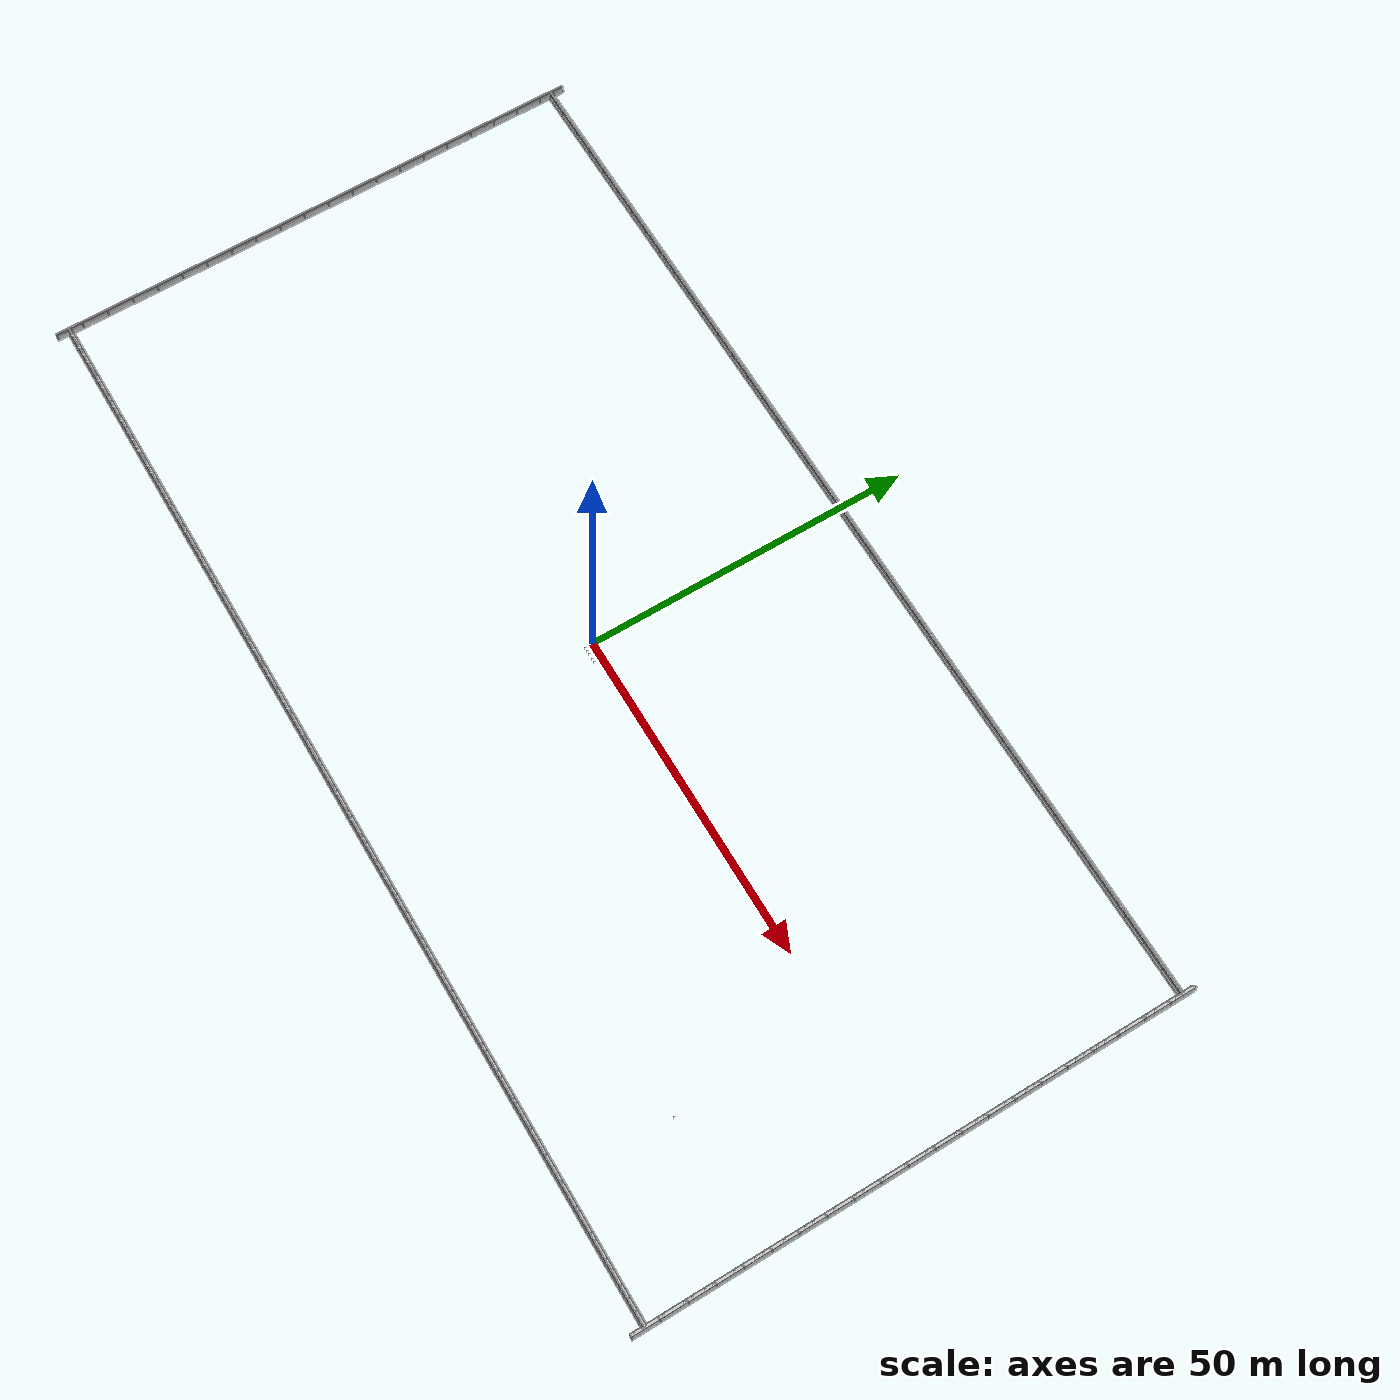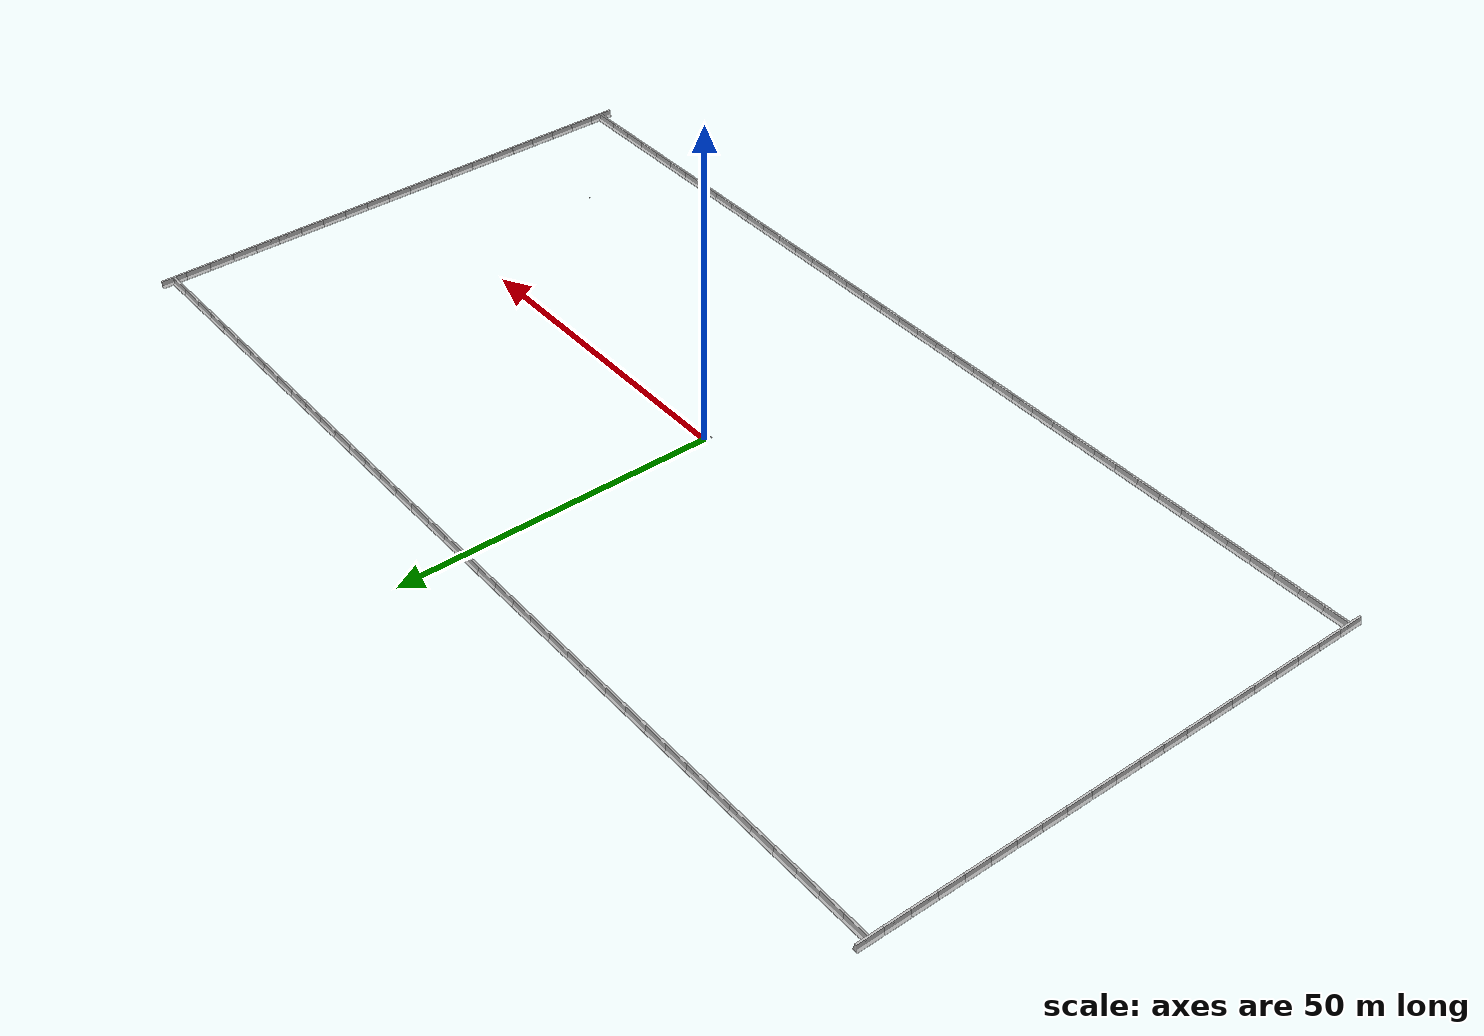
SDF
<sdf version="1.4">
 <world name="default">
  <physics type="ode"><gravity>0 0 -9.8</gravity></physics>
  <spherical_coordinates>
   <surface_model>EARTH_WGS84</surface_model>
   <latitude_deg>0</latitude_deg>
   <longitude_deg>0</longitude_deg>
   <elevation>0</elevation>
   <heading_deg>0</heading_deg>
  </spherical_coordinates>
  <scene><sky><clouds><speed>12</speed></clouds></sky></scene>
  <include><uri>model://sun</uri></include>
  <include><uri>model://arena</uri></include>
  <model name="wrench10">
   <pose>60.17 -23.75 0.54675 1.57079632679 0 1.57079632679</pose>
   <static>0</static>
   <link name="link">
    <inertial>
     <mass>0.0847</mass>
     <pose>0 0 0 -0.122173 0 0</pose>
     <inertia>
      <ixx>0.000185</ixx>
      <ixy>0.0000000</ixy>
      <ixz>-0.000000</ixz>
      <iyy>0.00000522</iyy>
      <iyz>-0.00000</iyz>
      <izz>0.000184</izz>
     </inertia>
    </inertial>
    <visual name="visual">
     <geometry><mesh><uri>file://wrench.DAE</uri><scale>0.77 0.77 1</scale></mesh></geometry>
     <material>
      <script><uri>file://media/materials/scripts/gazebo.material</uri><name>Gazebo/Grey</name></script>
      <shader type="pixel"><normal_map>__default__</normal_map></shader>
      <ambient>0.3 0.3 0.3 1</ambient>
      <diffuse>0.7 0.7 0.7 1</diffuse>
      <specular>0.01 0.01 0.01 1</specular>
      <emissive>0 0 0 1</emissive>
     </material>
    </visual>
    <collision name="collision">
     <geometry><mesh><uri>file://wrench.DAE</uri><scale>0.77 0.77 1</scale></mesh></geometry>
     <surface><friction><ode><mu>0.3</mu><mu2>0.3</mu2></ode></friction></surface>
    </collision>
   </link>
  </model>
  <model name="wrench12">
   <pose>60.17 -23.55 0.535 1.57079632679 0 1.57079632679</pose>
   <static>0</static>
   <link name="link">
    <inertial>
     <mass>0.0847</mass>
     <pose>0 0 0 -0.122173 0 0</pose>
     <inertia>
      <ixx>0.000185</ixx>
      <ixy>0.0000000</ixy>
      <ixz>-0.000000</ixz>
      <iyy>0.00000522</iyy>
      <iyz>-0.00000</iyz>
      <izz>0.000184</izz>
     </inertia>
    </inertial>
    <visual name="visual">
     <geometry><mesh><uri>file://wrench.DAE</uri><scale>0.92 0.92 1</scale></mesh></geometry>
     <material>
      <script><uri>file://media/materials/scripts/gazebo.material</uri><name>Gazebo/Grey</name></script>
      <shader type="pixel"><normal_map>__default__</normal_map></shader>
      <ambient>0.3 0.3 0.3 1</ambient>
      <diffuse>0.7 0.7 0.7 1</diffuse>
      <specular>0.01 0.01 0.01 1</specular>
      <emissive>0 0 0 1</emissive>
     </material>
    </visual>
    <collision name="collision">
     <geometry><mesh><uri>file://wrench.DAE</uri><scale>0.92 0.92 1</scale></mesh></geometry>
     <surface><friction><ode><mu>0.3</mu><mu2>0.3</mu2></ode></friction></surface>
    </collision>
   </link>
  </model>
  <model name="wrench13">
   <pose>60.17 -23.60 0.53 1.57079632679 0 1.57079632679</pose>
   <static>0</static>
   <link name="link">
    <inertial>
     <mass>0.0847</mass>
     <pose>0 0 0 -0.122173 0 0</pose>
     <inertia>
      <ixx>0.000185</ixx>
      <ixy>0.0000000</ixy>
      <ixz>-0.000000</ixz>
      <iyy>0.00000522</iyy>
      <iyz>-0.00000</iyz>
      <izz>0.000184</izz>
     </inertia>
    </inertial>
    <visual name="visual">
     <geometry><mesh><uri>file://wrench.DAE</uri><scale>1 1 1</scale></mesh></geometry>
     <material>
      <script><uri>file://media/materials/scripts/gazebo.material</uri><name>Gazebo/Grey</name></script>
      <shader type="pixel"><normal_map>__default__</normal_map></shader>
      <ambient>0.3 0.3 0.3 1</ambient>
      <diffuse>0.7 0.7 0.7 1</diffuse>
      <specular>0.01 0.01 0.01 1</specular>
      <emissive>0 0 0 1</emissive>
     </material>
    </visual>
    <collision name="collision">
     <geometry><mesh><uri>file://wrench.DAE</uri><scale>1 1 1</scale></mesh></geometry>
     <surface><friction><ode><mu>0.3</mu><mu2>0.3</mu2></ode></friction></surface>
    </collision>
   </link>
  </model>
  <model name="wrench18">
   <pose>60.172 -23.70 0.505 1.57079632679 0 1.57079632679</pose>
   <static>0</static>
   <link name="link">
    <inertial>
     <mass>0.3</mass>
     <pose>0 0 0 -0.122173 0 0</pose>
     <inertia>
      <ixx>1.185</ixx>
      <ixy>0.0000000</ixy>
      <ixz>-0.000000</ixz>
      <iyy>1.00522</iyy>
      <iyz>-0.00000</iyz>
      <izz>1.184</izz>
     </inertia>
    </inertial>
    <visual name="visual">
     <geometry><mesh><uri>file://wrench.DAE</uri><scale>1.38 1.38 1</scale></mesh></geometry>
     <material>
      <script><uri>file://media/materials/scripts/gazebo.material</uri><name>Gazebo/Grey</name></script>
      <shader type="pixel"><normal_map>__default__</normal_map></shader>
      <ambient>0.3 0.3 0.3 1</ambient>
      <diffuse>0.7 0.7 0.7 1</diffuse>
      <specular>0.01 0.01 0.01 1</specular>
      <emissive>0 0 0 1</emissive>
     </material>
    </visual>
    <collision name="collision">
     <geometry><mesh><uri>file://wrench.DAE</uri><scale>1.38 1.38 1</scale></mesh></geometry>
     <surface><friction><ode><mu>0.7</mu><mu2>0.7</mu2></ode></friction></surface>
    </collision>
   </link>
  </model>
  <model name="wrench11">
   <pose>60.17 -23.80 0.54675 1.57079632679 0 1.57079632679</pose>
   <static>0</static>
   <link name="link">
    <inertial>
     <mass>0.0847</mass>
     <pose>0 0 0 -0.122173 0 0</pose>
     <inertia>
      <ixx>0.000185</ixx>
      <ixy>0.0000000</ixy>
      <ixz>-0.000000</ixz>
      <iyy>0.00000522</iyy>
      <iyz>-0.00000</iyz>
      <izz>0.000184</izz>
     </inertia>
    </inertial>
    <visual name="visual">
     <geometry><mesh><uri>file://wrench.DAE</uri><scale>0.77 0.77 1</scale></mesh></geometry>
     <material>
      <script><uri>file://media/materials/scripts/gazebo.material</uri><name>Gazebo/Grey</name></script>
      <shader type="pixel"><normal_map>__default__</normal_map></shader>
      <ambient>0.3 0.3 0.3 1</ambient>
      <diffuse>0.7 0.7 0.7 1</diffuse>
      <specular>0.01 0.01 0.01 1</specular>
      <emissive>0 0 0 1</emissive>
     </material>
    </visual>
    <collision name="collision">
     <geometry><mesh><uri>file://wrench.DAE</uri><scale>0.77 0.77 1</scale></mesh></geometry>
     <surface><friction><ode><mu>0.3</mu><mu2>0.3</mu2></ode></friction></surface>
    </collision>
   </link>
  </model>
  <model name="wrench14">
   <pose>60.17 -23.65 0.54675 1.57079632679 0 1.57079632679</pose>
   <static>0</static>
   <link name="link">
    <inertial>
     <mass>0.0847</mass>
     <pose>0 0 0 -0.122173 0 0</pose>
     <inertia>
      <ixx>0.000185</ixx>
      <ixy>0.0000000</ixy>
      <ixz>-0.000000</ixz>
      <iyy>0.00000522</iyy>
      <iyz>-0.00000</iyz>
      <izz>0.000184</izz>
     </inertia>
    </inertial>
    <visual name="visual">
     <geometry><mesh><uri>file://wrench.DAE</uri><scale>0.77 0.77 1</scale></mesh></geometry>
     <material>
      <script><uri>file://media/materials/scripts/gazebo.material</uri><name>Gazebo/Grey</name></script>
      <shader type="pixel"><normal_map>__default__</normal_map></shader>
      <ambient>0.3 0.3 0.3 1</ambient>
      <diffuse>0.7 0.7 0.7 1</diffuse>
      <specular>0.01 0.01 0.01 1</specular>
      <emissive>0 0 0 1</emissive>
     </material>
    </visual>
    <collision name="collision">
     <geometry><mesh><uri>file://wrench.DAE</uri><scale>0.77 0.77 1</scale></mesh></geometry>
     <surface><friction><ode><mu>0.3</mu><mu2>0.3</mu2></ode></friction></surface>
    </collision>
   </link>
  </model>
  <model name="jersey_barrier">
   <pose>80 0 0 0 0 1.57079632679</pose>
   <static>1</static>
   <link name="link">
    <visual name="visual">
     <geometry><mesh><uri>model://jersey_barrier/meshes/jersey_barrier.dae</uri></mesh></geometry>
    </visual>
    <collision name="upright">
     <pose>0 0 0.5715 0 -0 0</pose>
     <geometry><box><size>4.06542 0.3063 1.143</size></box></geometry>
    </collision>
    <collision name="base">
     <pose>0 0 0.032258 0 -0 0</pose>
     <geometry><box><size>4.06542 0.8107 0.064516</size></box></geometry>
    </collision>
    <collision name="base2">
     <pose>0 0 0.1 0 -0 0</pose>
     <geometry><box><size>4.06542 0.65 0.1</size></box></geometry>
    </collision>
    <collision name="base3">
     <pose>0 0 0.2 0 -0 0</pose>
     <geometry><box><size>4.06542 0.5 0.1</size></box></geometry>
    </collision>
    <collision name="left-angle">
     <pose>0 -0.224 0.2401 0.9 -0 0</pose>
     <geometry><box><size>4.06542 0.5 0.064516</size></box></geometry>
    </collision>
    <collision name="right-angle">
     <pose>0 0.224 0.2401 -0.9 0 0</pose>
     <geometry><box><size>4.06542 0.5 0.064516</size></box></geometry>
    </collision>
    <velocity_decay><linear>0</linear><angular>0</angular></velocity_decay>
   </link>
   <pose>-8 -10 0 0 -0 0</pose>
  </model>
  <model name="jersey_barrier_0">
   <pose>80 4 0 0 0 1.57079632679</pose>
   <static>1</static>
   <link name="link">
    <visual name="visual">
     <geometry><mesh><uri>model://jersey_barrier/meshes/jersey_barrier.dae</uri></mesh></geometry>
    </visual>
    <collision name="upright">
     <pose>0 0 0.5715 0 -0 0</pose>
     <geometry><box><size>4.06542 0.3063 1.143</size></box></geometry>
    </collision>
    <collision name="base">
     <pose>0 0 0.032258 0 -0 0</pose>
     <geometry><box><size>4.06542 0.8107 0.064516</size></box></geometry>
    </collision>
    <collision name="base2">
     <pose>0 0 0.1 0 -0 0</pose>
     <geometry><box><size>4.06542 0.65 0.1</size></box></geometry>
    </collision>
    <collision name="base3">
     <pose>0 0 0.2 0 -0 0</pose>
     <geometry><box><size>4.06542 0.5 0.1</size></box></geometry>
    </collision>
    <collision name="left-angle">
     <pose>0 -0.224 0.2401 0.9 -0 0</pose>
     <geometry><box><size>4.06542 0.5 0.064516</size></box></geometry>
    </collision>
    <collision name="right-angle">
     <pose>0 0.224 0.2401 -0.9 0 0</pose>
     <geometry><box><size>4.06542 0.5 0.064516</size></box></geometry>
    </collision>
    <velocity_decay><linear>0</linear><angular>0</angular></velocity_decay>
   </link>
   <pose>-3 -10 0 0 -0 0</pose>
  </model>
  <model name="jersey_barrier_1">
   <pose>80 8 0 0 0 1.57079632679</pose>
   <static>1</static>
   <link name="link">
    <visual name="visual">
     <geometry><mesh><uri>model://jersey_barrier/meshes/jersey_barrier.dae</uri></mesh></geometry>
    </visual>
    <collision name="upright">
     <pose>0 0 0.5715 0 -0 0</pose>
     <geometry><box><size>4.06542 0.3063 1.143</size></box></geometry>
    </collision>
    <collision name="base">
     <pose>0 0 0.032258 0 -0 0</pose>
     <geometry><box><size>4.06542 0.8107 0.064516</size></box></geometry>
    </collision>
    <collision name="base2">
     <pose>0 0 0.1 0 -0 0</pose>
     <geometry><box><size>4.06542 0.65 0.1</size></box></geometry>
    </collision>
    <collision name="base3">
     <pose>0 0 0.2 0 -0 0</pose>
     <geometry><box><size>4.06542 0.5 0.1</size></box></geometry>
    </collision>
    <collision name="left-angle">
     <pose>0 -0.224 0.2401 0.9 -0 0</pose>
     <geometry><box><size>4.06542 0.5 0.064516</size></box></geometry>
    </collision>
    <collision name="right-angle">
     <pose>0 0.224 0.2401 -0.9 0 0</pose>
     <geometry><box><size>4.06542 0.5 0.064516</size></box></geometry>
    </collision>
    <velocity_decay><linear>0</linear><angular>0</angular></velocity_decay>
   </link>
   <pose>2 -10 0 0 -0 0</pose>
  </model>
  <model name="jersey_barrier_2">
   <pose>80 12 0 0 0 1.57079632679</pose>
   <static>1</static>
   <link name="link">
    <visual name="visual">
     <geometry><mesh><uri>model://jersey_barrier/meshes/jersey_barrier.dae</uri></mesh></geometry>
    </visual>
    <collision name="upright">
     <pose>0 0 0.5715 0 -0 0</pose>
     <geometry><box><size>4.06542 0.3063 1.143</size></box></geometry>
    </collision>
    <collision name="base">
     <pose>0 0 0.032258 0 -0 0</pose>
     <geometry><box><size>4.06542 0.8107 0.064516</size></box></geometry>
    </collision>
    <collision name="base2">
     <pose>0 0 0.1 0 -0 0</pose>
     <geometry><box><size>4.06542 0.65 0.1</size></box></geometry>
    </collision>
    <collision name="base3">
     <pose>0 0 0.2 0 -0 0</pose>
     <geometry><box><size>4.06542 0.5 0.1</size></box></geometry>
    </collision>
    <collision name="left-angle">
     <pose>0 -0.224 0.2401 0.9 -0 0</pose>
     <geometry><box><size>4.06542 0.5 0.064516</size></box></geometry>
    </collision>
    <collision name="right-angle">
     <pose>0 0.224 0.2401 -0.9 0 0</pose>
     <geometry><box><size>4.06542 0.5 0.064516</size></box></geometry>
    </collision>
    <velocity_decay><linear>0</linear><angular>0</angular></velocity_decay>
   </link>
   <pose>7 -10 0 0 -0 0</pose>
  </model>
  <model name="jersey_barrier_3">
   <pose>80 16 0 0 0 1.57079632679</pose>
   <static>1</static>
   <link name="link">
    <visual name="visual">
     <geometry><mesh><uri>model://jersey_barrier/meshes/jersey_barrier.dae</uri></mesh></geometry>
    </visual>
    <collision name="upright">
     <pose>0 0 0.5715 0 -0 0</pose>
     <geometry><box><size>4.06542 0.3063 1.143</size></box></geometry>
    </collision>
    <collision name="base">
     <pose>0 0 0.032258 0 -0 0</pose>
     <geometry><box><size>4.06542 0.8107 0.064516</size></box></geometry>
    </collision>
    <collision name="base2">
     <pose>0 0 0.1 0 -0 0</pose>
     <geometry><box><size>4.06542 0.65 0.1</size></box></geometry>
    </collision>
    <collision name="base3">
     <pose>0 0 0.2 0 -0 0</pose>
     <geometry><box><size>4.06542 0.5 0.1</size></box></geometry>
    </collision>
    <collision name="left-angle">
     <pose>0 -0.224 0.2401 0.9 -0 0</pose>
     <geometry><box><size>4.06542 0.5 0.064516</size></box></geometry>
    </collision>
    <collision name="right-angle">
     <pose>0 0.224 0.2401 -0.9 0 0</pose>
     <geometry><box><size>4.06542 0.5 0.064516</size></box></geometry>
    </collision>
    <velocity_decay><linear>0</linear><angular>0</angular></velocity_decay>
   </link>
   <pose>-7.50675 10 0 0 -0 0</pose>
  </model>
  <model name="jersey_barrier_4">
   <pose>80 20 0 0 0 1.57079632679</pose>
   <static>1</static>
   <link name="link">
    <visual name="visual">
     <geometry><mesh><uri>model://jersey_barrier/meshes/jersey_barrier.dae</uri></mesh></geometry>
    </visual>
    <collision name="upright">
     <pose>0 0 0.5715 0 -0 0</pose>
     <geometry><box><size>4.06542 0.3063 1.143</size></box></geometry>
    </collision>
    <collision name="base">
     <pose>0 0 0.032258 0 -0 0</pose>
     <geometry><box><size>4.06542 0.8107 0.064516</size></box></geometry>
    </collision>
    <collision name="base2">
     <pose>0 0 0.1 0 -0 0</pose>
     <geometry><box><size>4.06542 0.65 0.1</size></box></geometry>
    </collision>
    <collision name="base3">
     <pose>0 0 0.2 0 -0 0</pose>
     <geometry><box><size>4.06542 0.5 0.1</size></box></geometry>
    </collision>
    <collision name="left-angle">
     <pose>0 -0.224 0.2401 0.9 -0 0</pose>
     <geometry><box><size>4.06542 0.5 0.064516</size></box></geometry>
    </collision>
    <collision name="right-angle">
     <pose>0 0.224 0.2401 -0.9 0 0</pose>
     <geometry><box><size>4.06542 0.5 0.064516</size></box></geometry>
    </collision>
    <velocity_decay><linear>0</linear><angular>0</angular></velocity_decay>
   </link>
   <pose>-2 10 0 0 -0 0</pose>
  </model>
  <model name="jersey_barrier_5">
   <pose>80 24 0 0 0 1.57079632679</pose>
   <static>1</static>
   <link name="link">
    <visual name="visual">
     <geometry><mesh><uri>model://jersey_barrier/meshes/jersey_barrier.dae</uri></mesh></geometry>
    </visual>
    <collision name="upright">
     <pose>0 0 0.5715 0 -0 0</pose>
     <geometry><box><size>4.06542 0.3063 1.143</size></box></geometry>
    </collision>
    <collision name="base">
     <pose>0 0 0.032258 0 -0 0</pose>
     <geometry><box><size>4.06542 0.8107 0.064516</size></box></geometry>
    </collision>
    <collision name="base2">
     <pose>0 0 0.1 0 -0 0</pose>
     <geometry><box><size>4.06542 0.65 0.1</size></box></geometry>
    </collision>
    <collision name="base3">
     <pose>0 0 0.2 0 -0 0</pose>
     <geometry><box><size>4.06542 0.5 0.1</size></box></geometry>
    </collision>
    <collision name="left-angle">
     <pose>0 -0.224 0.2401 0.9 -0 0</pose>
     <geometry><box><size>4.06542 0.5 0.064516</size></box></geometry>
    </collision>
    <collision name="right-angle">
     <pose>0 0.224 0.2401 -0.9 0 0</pose>
     <geometry><box><size>4.06542 0.5 0.064516</size></box></geometry>
    </collision>
    <velocity_decay><linear>0</linear><angular>0</angular></velocity_decay>
   </link>
   <pose>3 10 0 0 -0 0</pose>
  </model>
  <model name="jersey_barrier_6">
   <pose>80 28 0 0 0 1.57079632679</pose>
   <static>1</static>
   <link name="link">
    <visual name="visual">
     <geometry><mesh><uri>model://jersey_barrier/meshes/jersey_barrier.dae</uri></mesh></geometry>
    </visual>
    <collision name="upright">
     <pose>0 0 0.5715 0 -0 0</pose>
     <geometry><box><size>4.06542 0.3063 1.143</size></box></geometry>
    </collision>
    <collision name="base">
     <pose>0 0 0.032258 0 -0 0</pose>
     <geometry><box><size>4.06542 0.8107 0.064516</size></box></geometry>
    </collision>
    <collision name="base2">
     <pose>0 0 0.1 0 -0 0</pose>
     <geometry><box><size>4.06542 0.65 0.1</size></box></geometry>
    </collision>
    <collision name="base3">
     <pose>0 0 0.2 0 -0 0</pose>
     <geometry><box><size>4.06542 0.5 0.1</size></box></geometry>
    </collision>
    <collision name="left-angle">
     <pose>0 -0.224 0.2401 0.9 -0 0</pose>
     <geometry><box><size>4.06542 0.5 0.064516</size></box></geometry>
    </collision>
    <collision name="right-angle">
     <pose>0 0.224 0.2401 -0.9 0 0</pose>
     <geometry><box><size>4.06542 0.5 0.064516</size></box></geometry>
    </collision>
    <velocity_decay><linear>0</linear><angular>0</angular></velocity_decay>
   </link>
   <pose>8 10 0 0 -0 0</pose>
  </model>
  <model name="jersey_barrier_7">
   <pose>80 32 0 0 0 1.57079632679</pose>
   <static>1</static>
   <link name="link">
    <visual name="visual">
     <geometry><mesh><uri>model://jersey_barrier/meshes/jersey_barrier.dae</uri></mesh></geometry>
    </visual>
    <collision name="upright">
     <pose>0 0 0.5715 0 -0 0</pose>
     <geometry><box><size>4.06542 0.3063 1.143</size></box></geometry>
    </collision>
    <collision name="base">
     <pose>0 0 0.032258 0 -0 0</pose>
     <geometry><box><size>4.06542 0.8107 0.064516</size></box></geometry>
    </collision>
    <collision name="base2">
     <pose>0 0 0.1 0 -0 0</pose>
     <geometry><box><size>4.06542 0.65 0.1</size></box></geometry>
    </collision>
    <collision name="base3">
     <pose>0 0 0.2 0 -0 0</pose>
     <geometry><box><size>4.06542 0.5 0.1</size></box></geometry>
    </collision>
    <collision name="left-angle">
     <pose>0 -0.224 0.2401 0.9 -0 0</pose>
     <geometry><box><size>4.06542 0.5 0.064516</size></box></geometry>
    </collision>
    <collision name="right-angle">
     <pose>0 0.224 0.2401 -0.9 0 0</pose>
     <geometry><box><size>4.06542 0.5 0.064516</size></box></geometry>
    </collision>
    <velocity_decay><linear>0</linear><angular>0</angular></velocity_decay>
   </link>
   <pose>9 -4 0 0 -0 0</pose>
  </model>
  <model name="jersey_barrier_8">
   <pose>80 36 0 0 0 1.57079632679</pose>
   <static>1</static>
   <link name="link">
    <visual name="visual">
     <geometry><mesh><uri>model://jersey_barrier/meshes/jersey_barrier.dae</uri></mesh></geometry>
    </visual>
    <collision name="upright">
     <pose>0 0 0.5715 0 -0 0</pose>
     <geometry><box><size>4.06542 0.3063 1.143</size></box></geometry>
    </collision>
    <collision name="base">
     <pose>0 0 0.032258 0 -0 0</pose>
     <geometry><box><size>4.06542 0.8107 0.064516</size></box></geometry>
    </collision>
    <collision name="base2">
     <pose>0 0 0.1 0 -0 0</pose>
     <geometry><box><size>4.06542 0.65 0.1</size></box></geometry>
    </collision>
    <collision name="base3">
     <pose>0 0 0.2 0 -0 0</pose>
     <geometry><box><size>4.06542 0.5 0.1</size></box></geometry>
    </collision>
    <collision name="left-angle">
     <pose>0 -0.224 0.2401 0.9 -0 0</pose>
     <geometry><box><size>4.06542 0.5 0.064516</size></box></geometry>
    </collision>
    <collision name="right-angle">
     <pose>0 0.224 0.2401 -0.9 0 0</pose>
     <geometry><box><size>4.06542 0.5 0.064516</size></box></geometry>
    </collision>
    <velocity_decay><linear>0</linear><angular>0</angular></velocity_decay>
   </link>
   <pose>9 3 0 0 -0 0</pose>
  </model>
  <model name="jersey_barrier_9">
   <pose>80 40 0 0 0 1.57079632679</pose>
   <static>1</static>
   <link name="link">
    <visual name="visual">
     <geometry><mesh><uri>model://jersey_barrier/meshes/jersey_barrier.dae</uri></mesh></geometry>
    </visual>
    <collision name="upright">
     <pose>0 0 0.5715 0 -0 0</pose>
     <geometry><box><size>4.06542 0.3063 1.143</size></box></geometry>
    </collision>
    <collision name="base">
     <pose>0 0 0.032258 0 -0 0</pose>
     <geometry><box><size>4.06542 0.8107 0.064516</size></box></geometry>
    </collision>
    <collision name="base2">
     <pose>0 0 0.1 0 -0 0</pose>
     <geometry><box><size>4.06542 0.65 0.1</size></box></geometry>
    </collision>
    <collision name="base3">
     <pose>0 0 0.2 0 -0 0</pose>
     <geometry><box><size>4.06542 0.5 0.1</size></box></geometry>
    </collision>
    <collision name="left-angle">
     <pose>0 -0.224 0.2401 0.9 -0 0</pose>
     <geometry><box><size>4.06542 0.5 0.064516</size></box></geometry>
    </collision>
    <collision name="right-angle">
     <pose>0 0.224 0.2401 -0.9 0 0</pose>
     <geometry><box><size>4.06542 0.5 0.064516</size></box></geometry>
    </collision>
    <velocity_decay><linear>0</linear><angular>0</angular></velocity_decay>
   </link>
   <pose>-9 -6.56962 0 0 -0 0</pose>
  </model>
  <model name="jersey_barrier_10">
   <pose>78 40 0 0 0 0</pose>
   <static>1</static>
   <link name="link">
    <visual name="visual">
     <geometry><mesh><uri>model://jersey_barrier/meshes/jersey_barrier.dae</uri></mesh></geometry>
    </visual>
    <collision name="upright">
     <pose>0 0 0.5715 0 -0 0</pose>
     <geometry><box><size>4.06542 0.3063 1.143</size></box></geometry>
    </collision>
    <collision name="base">
     <pose>0 0 0.032258 0 -0 0</pose>
     <geometry><box><size>4.06542 0.8107 0.064516</size></box></geometry>
    </collision>
    <collision name="base2">
     <pose>0 0 0.1 0 -0 0</pose>
     <geometry><box><size>4.06542 0.65 0.1</size></box></geometry>
    </collision>
    <collision name="base3">
     <pose>0 0 0.2 0 -0 0</pose>
     <geometry><box><size>4.06542 0.5 0.1</size></box></geometry>
    </collision>
    <collision name="left-angle">
     <pose>0 -0.224 0.2401 0.9 -0 0</pose>
     <geometry><box><size>4.06542 0.5 0.064516</size></box></geometry>
    </collision>
    <collision name="right-angle">
     <pose>0 0.224 0.2401 -0.9 0 0</pose>
     <geometry><box><size>4.06542 0.5 0.064516</size></box></geometry>
    </collision>
    <velocity_decay><linear>0</linear><angular>0</angular></velocity_decay>
   </link>
   <pose>-10 -2 0 0 -0 0</pose>
  </model>
  <model name="jersey_barrier_11">
   <pose>74 40 0 0 0 0</pose>
   <static>1</static>
   <link name="link">
    <visual name="visual">
     <geometry><mesh><uri>model://jersey_barrier/meshes/jersey_barrier.dae</uri></mesh></geometry>
    </visual>
    <collision name="upright">
     <pose>0 0 0.5715 0 -0 0</pose>
     <geometry><box><size>4.06542 0.3063 1.143</size></box></geometry>
    </collision>
    <collision name="base">
     <pose>0 0 0.032258 0 -0 0</pose>
     <geometry><box><size>4.06542 0.8107 0.064516</size></box></geometry>
    </collision>
    <collision name="base2">
     <pose>0 0 0.1 0 -0 0</pose>
     <geometry><box><size>4.06542 0.65 0.1</size></box></geometry>
    </collision>
    <collision name="base3">
     <pose>0 0 0.2 0 -0 0</pose>
     <geometry><box><size>4.06542 0.5 0.1</size></box></geometry>
    </collision>
    <collision name="left-angle">
     <pose>0 -0.224 0.2401 0.9 -0 0</pose>
     <geometry><box><size>4.06542 0.5 0.064516</size></box></geometry>
    </collision>
    <collision name="right-angle">
     <pose>0 0.224 0.2401 -0.9 0 0</pose>
     <geometry><box><size>4.06542 0.5 0.064516</size></box></geometry>
    </collision>
    <velocity_decay><linear>0</linear><angular>0</angular></velocity_decay>
   </link>
   <pose>-9.55113 3 0 0 -0 0</pose>
  </model>
  <model name="jersey_barrier_12">
   <pose>70 40 0 0 0 0</pose>
   <static>1</static>
   <link name="link">
    <visual name="visual">
     <geometry><mesh><uri>model://jersey_barrier/meshes/jersey_barrier.dae</uri></mesh></geometry>
    </visual>
    <collision name="upright">
     <pose>0 0 0.5715 0 -0 0</pose>
     <geometry><box><size>4.06542 0.3063 1.143</size></box></geometry>
    </collision>
    <collision name="base">
     <pose>0 0 0.032258 0 -0 0</pose>
     <geometry><box><size>4.06542 0.8107 0.064516</size></box></geometry>
    </collision>
    <collision name="base2">
     <pose>0 0 0.1 0 -0 0</pose>
     <geometry><box><size>4.06542 0.65 0.1</size></box></geometry>
    </collision>
    <collision name="base3">
     <pose>0 0 0.2 0 -0 0</pose>
     <geometry><box><size>4.06542 0.5 0.1</size></box></geometry>
    </collision>
    <collision name="left-angle">
     <pose>0 -0.224 0.2401 0.9 -0 0</pose>
     <geometry><box><size>4.06542 0.5 0.064516</size></box></geometry>
    </collision>
    <collision name="right-angle">
     <pose>0 0.224 0.2401 -0.9 0 0</pose>
     <geometry><box><size>4.06542 0.5 0.064516</size></box></geometry>
    </collision>
    <velocity_decay><linear>0</linear><angular>0</angular></velocity_decay>
   </link>
   <pose>9 -8 0 0 -0 0</pose>
  </model>
  <model name="jersey_barrier_13">
   <pose>66 40 0 0 0 0</pose>
   <static>1</static>
   <link name="link">
    <visual name="visual">
     <geometry><mesh><uri>model://jersey_barrier/meshes/jersey_barrier.dae</uri></mesh></geometry>
    </visual>
    <collision name="upright">
     <pose>0 0 0.5715 0 -0 0</pose>
     <geometry><box><size>4.06542 0.3063 1.143</size></box></geometry>
    </collision>
    <collision name="base">
     <pose>0 0 0.032258 0 -0 0</pose>
     <geometry><box><size>4.06542 0.8107 0.064516</size></box></geometry>
    </collision>
    <collision name="base2">
     <pose>0 0 0.1 0 -0 0</pose>
     <geometry><box><size>4.06542 0.65 0.1</size></box></geometry>
    </collision>
    <collision name="base3">
     <pose>0 0 0.2 0 -0 0</pose>
     <geometry><box><size>4.06542 0.5 0.1</size></box></geometry>
    </collision>
    <collision name="left-angle">
     <pose>0 -0.224 0.2401 0.9 -0 0</pose>
     <geometry><box><size>4.06542 0.5 0.064516</size></box></geometry>
    </collision>
    <collision name="right-angle">
     <pose>0 0.224 0.2401 -0.9 0 0</pose>
     <geometry><box><size>4.06542 0.5 0.064516</size></box></geometry>
    </collision>
    <velocity_decay><linear>0</linear><angular>0</angular></velocity_decay>
   </link>
   <pose>10 7 0 0 -0 0</pose>
  </model>
  <model name="jersey_barrier_14">
   <pose>62 40 0 0 0 0</pose>
   <static>1</static>
   <link name="link">
    <visual name="visual">
     <geometry><mesh><uri>model://jersey_barrier/meshes/jersey_barrier.dae</uri></mesh></geometry>
    </visual>
    <collision name="upright">
     <pose>0 0 0.5715 0 -0 0</pose>
     <geometry><box><size>4.06542 0.3063 1.143</size></box></geometry>
    </collision>
    <collision name="base">
     <pose>0 0 0.032258 0 -0 0</pose>
     <geometry><box><size>4.06542 0.8107 0.064516</size></box></geometry>
    </collision>
    <collision name="base2">
     <pose>0 0 0.1 0 -0 0</pose>
     <geometry><box><size>4.06542 0.65 0.1</size></box></geometry>
    </collision>
    <collision name="base3">
     <pose>0 0 0.2 0 -0 0</pose>
     <geometry><box><size>4.06542 0.5 0.1</size></box></geometry>
    </collision>
    <collision name="left-angle">
     <pose>0 -0.224 0.2401 0.9 -0 0</pose>
     <geometry><box><size>4.06542 0.5 0.064516</size></box></geometry>
    </collision>
    <collision name="right-angle">
     <pose>0 0.224 0.2401 -0.9 0 0</pose>
     <geometry><box><size>4.06542 0.5 0.064516</size></box></geometry>
    </collision>
    <velocity_decay><linear>0</linear><angular>0</angular></velocity_decay>
   </link>
   <pose>-9 7.4858 0 0 -0 0</pose>
  </model>
  <model name="jersey_barrier_15">
   <pose>58 40 0 0 0 0</pose>
   <static>1</static>
   <link name="link">
    <visual name="visual">
     <geometry><mesh><uri>model://jersey_barrier/meshes/jersey_barrier.dae</uri></mesh></geometry>
    </visual>
    <collision name="upright">
     <pose>0 0 0.5715 0 -0 0</pose>
     <geometry><box><size>4.06542 0.3063 1.143</size></box></geometry>
    </collision>
    <collision name="base">
     <pose>0 0 0.032258 0 -0 0</pose>
     <geometry><box><size>4.06542 0.8107 0.064516</size></box></geometry>
    </collision>
    <collision name="base2">
     <pose>0 0 0.1 0 -0 0</pose>
     <geometry><box><size>4.06542 0.65 0.1</size></box></geometry>
    </collision>
    <collision name="base3">
     <pose>0 0 0.2 0 -0 0</pose>
     <geometry><box><size>4.06542 0.5 0.1</size></box></geometry>
    </collision>
    <collision name="left-angle">
     <pose>0 -0.224 0.2401 0.9 -0 0</pose>
     <geometry><box><size>4.06542 0.5 0.064516</size></box></geometry>
    </collision>
    <collision name="right-angle">
     <pose>0 0.224 0.2401 -0.9 0 0</pose>
     <geometry><box><size>4.06542 0.5 0.064516</size></box></geometry>
    </collision>
    <velocity_decay><linear>0</linear><angular>0</angular></velocity_decay>
   </link>
   <pose>2.45495 0 0 0 -0 0</pose>
  </model>
  <model name="jersey_barrier_16">
   <pose>54 40 0 0 0 0</pose>
   <static>1</static>
   <link name="link">
    <visual name="visual">
     <geometry><mesh><uri>model://jersey_barrier/meshes/jersey_barrier.dae</uri></mesh></geometry>
    </visual>
    <collision name="upright">
     <pose>0 0 0.5715 0 -0 0</pose>
     <geometry><box><size>4.06542 0.3063 1.143</size></box></geometry>
    </collision>
    <collision name="base">
     <pose>0 0 0.032258 0 -0 0</pose>
     <geometry><box><size>4.06542 0.8107 0.064516</size></box></geometry>
    </collision>
    <collision name="base2">
     <pose>0 0 0.1 0 -0 0</pose>
     <geometry><box><size>4.06542 0.65 0.1</size></box></geometry>
    </collision>
    <collision name="base3">
     <pose>0 0 0.2 0 -0 0</pose>
     <geometry><box><size>4.06542 0.5 0.1</size></box></geometry>
    </collision>
    <collision name="left-angle">
     <pose>0 -0.224 0.2401 0.9 -0 0</pose>
     <geometry><box><size>4.06542 0.5 0.064516</size></box></geometry>
    </collision>
    <collision name="right-angle">
     <pose>0 0.224 0.2401 -0.9 0 0</pose>
     <geometry><box><size>4.06542 0.5 0.064516</size></box></geometry>
    </collision>
    <velocity_decay><linear>0</linear><angular>0</angular></velocity_decay>
   </link>
   <pose>2.45495 0 0 0 -0 0</pose>
  </model>
  <model name="jersey_barrier_17">
   <pose>50 40 0 0 0 0</pose>
   <static>1</static>
   <link name="link">
    <visual name="visual">
     <geometry><mesh><uri>model://jersey_barrier/meshes/jersey_barrier.dae</uri></mesh></geometry>
    </visual>
    <collision name="upright">
     <pose>0 0 0.5715 0 -0 0</pose>
     <geometry><box><size>4.06542 0.3063 1.143</size></box></geometry>
    </collision>
    <collision name="base">
     <pose>0 0 0.032258 0 -0 0</pose>
     <geometry><box><size>4.06542 0.8107 0.064516</size></box></geometry>
    </collision>
    <collision name="base2">
     <pose>0 0 0.1 0 -0 0</pose>
     <geometry><box><size>4.06542 0.65 0.1</size></box></geometry>
    </collision>
    <collision name="base3">
     <pose>0 0 0.2 0 -0 0</pose>
     <geometry><box><size>4.06542 0.5 0.1</size></box></geometry>
    </collision>
    <collision name="left-angle">
     <pose>0 -0.224 0.2401 0.9 -0 0</pose>
     <geometry><box><size>4.06542 0.5 0.064516</size></box></geometry>
    </collision>
    <collision name="right-angle">
     <pose>0 0.224 0.2401 -0.9 0 0</pose>
     <geometry><box><size>4.06542 0.5 0.064516</size></box></geometry>
    </collision>
    <velocity_decay><linear>0</linear><angular>0</angular></velocity_decay>
   </link>
   <pose>-10 -2 0 0 -0 0</pose>
  </model>
  <model name="jersey_barrier_18">
   <pose>46 40 0 0 0 0</pose>
   <static>1</static>
   <link name="link">
    <visual name="visual">
     <geometry><mesh><uri>model://jersey_barrier/meshes/jersey_barrier.dae</uri></mesh></geometry>
    </visual>
    <collision name="upright">
     <pose>0 0 0.5715 0 -0 0</pose>
     <geometry><box><size>4.06542 0.3063 1.143</size></box></geometry>
    </collision>
    <collision name="base">
     <pose>0 0 0.032258 0 -0 0</pose>
     <geometry><box><size>4.06542 0.8107 0.064516</size></box></geometry>
    </collision>
    <collision name="base2">
     <pose>0 0 0.1 0 -0 0</pose>
     <geometry><box><size>4.06542 0.65 0.1</size></box></geometry>
    </collision>
    <collision name="base3">
     <pose>0 0 0.2 0 -0 0</pose>
     <geometry><box><size>4.06542 0.5 0.1</size></box></geometry>
    </collision>
    <collision name="left-angle">
     <pose>0 -0.224 0.2401 0.9 -0 0</pose>
     <geometry><box><size>4.06542 0.5 0.064516</size></box></geometry>
    </collision>
    <collision name="right-angle">
     <pose>0 0.224 0.2401 -0.9 0 0</pose>
     <geometry><box><size>4.06542 0.5 0.064516</size></box></geometry>
    </collision>
    <velocity_decay><linear>0</linear><angular>0</angular></velocity_decay>
   </link>
   <pose>-9.55113 3 0 0 -0 0</pose>
  </model>
  <model name="jersey_barrier_19">
   <pose>42 40 0 0 0 0</pose>
   <static>1</static>
   <link name="link">
    <visual name="visual">
     <geometry><mesh><uri>model://jersey_barrier/meshes/jersey_barrier.dae</uri></mesh></geometry>
    </visual>
    <collision name="upright">
     <pose>0 0 0.5715 0 -0 0</pose>
     <geometry><box><size>4.06542 0.3063 1.143</size></box></geometry>
    </collision>
    <collision name="base">
     <pose>0 0 0.032258 0 -0 0</pose>
     <geometry><box><size>4.06542 0.8107 0.064516</size></box></geometry>
    </collision>
    <collision name="base2">
     <pose>0 0 0.1 0 -0 0</pose>
     <geometry><box><size>4.06542 0.65 0.1</size></box></geometry>
    </collision>
    <collision name="base3">
     <pose>0 0 0.2 0 -0 0</pose>
     <geometry><box><size>4.06542 0.5 0.1</size></box></geometry>
    </collision>
    <collision name="left-angle">
     <pose>0 -0.224 0.2401 0.9 -0 0</pose>
     <geometry><box><size>4.06542 0.5 0.064516</size></box></geometry>
    </collision>
    <collision name="right-angle">
     <pose>0 0.224 0.2401 -0.9 0 0</pose>
     <geometry><box><size>4.06542 0.5 0.064516</size></box></geometry>
    </collision>
    <velocity_decay><linear>0</linear><angular>0</angular></velocity_decay>
   </link>
   <pose>9 -8 0 0 -0 0</pose>
  </model>
  <model name="jersey_barrier_20">
   <pose>38 40 0 0 0 0</pose>
   <static>1</static>
   <link name="link">
    <visual name="visual">
     <geometry><mesh><uri>model://jersey_barrier/meshes/jersey_barrier.dae</uri></mesh></geometry>
    </visual>
    <collision name="upright">
     <pose>0 0 0.5715 0 -0 0</pose>
     <geometry><box><size>4.06542 0.3063 1.143</size></box></geometry>
    </collision>
    <collision name="base">
     <pose>0 0 0.032258 0 -0 0</pose>
     <geometry><box><size>4.06542 0.8107 0.064516</size></box></geometry>
    </collision>
    <collision name="base2">
     <pose>0 0 0.1 0 -0 0</pose>
     <geometry><box><size>4.06542 0.65 0.1</size></box></geometry>
    </collision>
    <collision name="base3">
     <pose>0 0 0.2 0 -0 0</pose>
     <geometry><box><size>4.06542 0.5 0.1</size></box></geometry>
    </collision>
    <collision name="left-angle">
     <pose>0 -0.224 0.2401 0.9 -0 0</pose>
     <geometry><box><size>4.06542 0.5 0.064516</size></box></geometry>
    </collision>
    <collision name="right-angle">
     <pose>0 0.224 0.2401 -0.9 0 0</pose>
     <geometry><box><size>4.06542 0.5 0.064516</size></box></geometry>
    </collision>
    <velocity_decay><linear>0</linear><angular>0</angular></velocity_decay>
   </link>
   <pose>10 7 0 0 -0 0</pose>
  </model>
  <model name="jersey_barrier_21">
   <pose>34 40 0 0 0 0</pose>
   <static>1</static>
   <link name="link">
    <visual name="visual">
     <geometry><mesh><uri>model://jersey_barrier/meshes/jersey_barrier.dae</uri></mesh></geometry>
    </visual>
    <collision name="upright">
     <pose>0 0 0.5715 0 -0 0</pose>
     <geometry><box><size>4.06542 0.3063 1.143</size></box></geometry>
    </collision>
    <collision name="base">
     <pose>0 0 0.032258 0 -0 0</pose>
     <geometry><box><size>4.06542 0.8107 0.064516</size></box></geometry>
    </collision>
    <collision name="base2">
     <pose>0 0 0.1 0 -0 0</pose>
     <geometry><box><size>4.06542 0.65 0.1</size></box></geometry>
    </collision>
    <collision name="base3">
     <pose>0 0 0.2 0 -0 0</pose>
     <geometry><box><size>4.06542 0.5 0.1</size></box></geometry>
    </collision>
    <collision name="left-angle">
     <pose>0 -0.224 0.2401 0.9 -0 0</pose>
     <geometry><box><size>4.06542 0.5 0.064516</size></box></geometry>
    </collision>
    <collision name="right-angle">
     <pose>0 0.224 0.2401 -0.9 0 0</pose>
     <geometry><box><size>4.06542 0.5 0.064516</size></box></geometry>
    </collision>
    <velocity_decay><linear>0</linear><angular>0</angular></velocity_decay>
   </link>
   <pose>-9 7.4858 0 0 -0 0</pose>
  </model>
  <model name="jersey_barrier_22">
   <pose>30 40 0 0 0 0</pose>
   <static>1</static>
   <link name="link">
    <visual name="visual">
     <geometry><mesh><uri>model://jersey_barrier/meshes/jersey_barrier.dae</uri></mesh></geometry>
    </visual>
    <collision name="upright">
     <pose>0 0 0.5715 0 -0 0</pose>
     <geometry><box><size>4.06542 0.3063 1.143</size></box></geometry>
    </collision>
    <collision name="base">
     <pose>0 0 0.032258 0 -0 0</pose>
     <geometry><box><size>4.06542 0.8107 0.064516</size></box></geometry>
    </collision>
    <collision name="base2">
     <pose>0 0 0.1 0 -0 0</pose>
     <geometry><box><size>4.06542 0.65 0.1</size></box></geometry>
    </collision>
    <collision name="base3">
     <pose>0 0 0.2 0 -0 0</pose>
     <geometry><box><size>4.06542 0.5 0.1</size></box></geometry>
    </collision>
    <collision name="left-angle">
     <pose>0 -0.224 0.2401 0.9 -0 0</pose>
     <geometry><box><size>4.06542 0.5 0.064516</size></box></geometry>
    </collision>
    <collision name="right-angle">
     <pose>0 0.224 0.2401 -0.9 0 0</pose>
     <geometry><box><size>4.06542 0.5 0.064516</size></box></geometry>
    </collision>
    <velocity_decay><linear>0</linear><angular>0</angular></velocity_decay>
   </link>
   <pose>2.45495 0 0 0 -0 0</pose>
  </model>
  <model name="jersey_barrier_23">
   <pose>26 40 0 0 0 0</pose>
   <static>1</static>
   <link name="link">
    <visual name="visual">
     <geometry><mesh><uri>model://jersey_barrier/meshes/jersey_barrier.dae</uri></mesh></geometry>
    </visual>
    <collision name="upright">
     <pose>0 0 0.5715 0 -0 0</pose>
     <geometry><box><size>4.06542 0.3063 1.143</size></box></geometry>
    </collision>
    <collision name="base">
     <pose>0 0 0.032258 0 -0 0</pose>
     <geometry><box><size>4.06542 0.8107 0.064516</size></box></geometry>
    </collision>
    <collision name="base2">
     <pose>0 0 0.1 0 -0 0</pose>
     <geometry><box><size>4.06542 0.65 0.1</size></box></geometry>
    </collision>
    <collision name="base3">
     <pose>0 0 0.2 0 -0 0</pose>
     <geometry><box><size>4.06542 0.5 0.1</size></box></geometry>
    </collision>
    <collision name="left-angle">
     <pose>0 -0.224 0.2401 0.9 -0 0</pose>
     <geometry><box><size>4.06542 0.5 0.064516</size></box></geometry>
    </collision>
    <collision name="right-angle">
     <pose>0 0.224 0.2401 -0.9 0 0</pose>
     <geometry><box><size>4.06542 0.5 0.064516</size></box></geometry>
    </collision>
    <velocity_decay><linear>0</linear><angular>0</angular></velocity_decay>
   </link>
   <pose>2.45495 0 0 0 -0 0</pose>
  </model>
  <model name="jersey_barrier_24">
   <pose>22 40 0 0 0 0</pose>
   <static>1</static>
   <link name="link">
    <visual name="visual">
     <geometry><mesh><uri>model://jersey_barrier/meshes/jersey_barrier.dae</uri></mesh></geometry>
    </visual>
    <collision name="upright">
     <pose>0 0 0.5715 0 -0 0</pose>
     <geometry><box><size>4.06542 0.3063 1.143</size></box></geometry>
    </collision>
    <collision name="base">
     <pose>0 0 0.032258 0 -0 0</pose>
     <geometry><box><size>4.06542 0.8107 0.064516</size></box></geometry>
    </collision>
    <collision name="base2">
     <pose>0 0 0.1 0 -0 0</pose>
     <geometry><box><size>4.06542 0.65 0.1</size></box></geometry>
    </collision>
    <collision name="base3">
     <pose>0 0 0.2 0 -0 0</pose>
     <geometry><box><size>4.06542 0.5 0.1</size></box></geometry>
    </collision>
    <collision name="left-angle">
     <pose>0 -0.224 0.2401 0.9 -0 0</pose>
     <geometry><box><size>4.06542 0.5 0.064516</size></box></geometry>
    </collision>
    <collision name="right-angle">
     <pose>0 0.224 0.2401 -0.9 0 0</pose>
     <geometry><box><size>4.06542 0.5 0.064516</size></box></geometry>
    </collision>
    <velocity_decay><linear>0</linear><angular>0</angular></velocity_decay>
   </link>
   <pose>-10 -2 0 0 -0 0</pose>
  </model>
  <model name="jersey_barrier_25">
   <pose>18 40 0 0 0 0</pose>
   <static>1</static>
   <link name="link">
    <visual name="visual">
     <geometry><mesh><uri>model://jersey_barrier/meshes/jersey_barrier.dae</uri></mesh></geometry>
    </visual>
    <collision name="upright">
     <pose>0 0 0.5715 0 -0 0</pose>
     <geometry><box><size>4.06542 0.3063 1.143</size></box></geometry>
    </collision>
    <collision name="base">
     <pose>0 0 0.032258 0 -0 0</pose>
     <geometry><box><size>4.06542 0.8107 0.064516</size></box></geometry>
    </collision>
    <collision name="base2">
     <pose>0 0 0.1 0 -0 0</pose>
     <geometry><box><size>4.06542 0.65 0.1</size></box></geometry>
    </collision>
    <collision name="base3">
     <pose>0 0 0.2 0 -0 0</pose>
     <geometry><box><size>4.06542 0.5 0.1</size></box></geometry>
    </collision>
    <collision name="left-angle">
     <pose>0 -0.224 0.2401 0.9 -0 0</pose>
     <geometry><box><size>4.06542 0.5 0.064516</size></box></geometry>
    </collision>
    <collision name="right-angle">
     <pose>0 0.224 0.2401 -0.9 0 0</pose>
     <geometry><box><size>4.06542 0.5 0.064516</size></box></geometry>
    </collision>
    <velocity_decay><linear>0</linear><angular>0</angular></velocity_decay>
   </link>
   <pose>-9.55113 3 0 0 -0 0</pose>
  </model>
  <model name="jersey_barrier_26">
   <pose>14 40 0 0 0 0</pose>
   <static>1</static>
   <link name="link">
    <visual name="visual">
     <geometry><mesh><uri>model://jersey_barrier/meshes/jersey_barrier.dae</uri></mesh></geometry>
    </visual>
    <collision name="upright">
     <pose>0 0 0.5715 0 -0 0</pose>
     <geometry><box><size>4.06542 0.3063 1.143</size></box></geometry>
    </collision>
    <collision name="base">
     <pose>0 0 0.032258 0 -0 0</pose>
     <geometry><box><size>4.06542 0.8107 0.064516</size></box></geometry>
    </collision>
    <collision name="base2">
     <pose>0 0 0.1 0 -0 0</pose>
     <geometry><box><size>4.06542 0.65 0.1</size></box></geometry>
    </collision>
    <collision name="base3">
     <pose>0 0 0.2 0 -0 0</pose>
     <geometry><box><size>4.06542 0.5 0.1</size></box></geometry>
    </collision>
    <collision name="left-angle">
     <pose>0 -0.224 0.2401 0.9 -0 0</pose>
     <geometry><box><size>4.06542 0.5 0.064516</size></box></geometry>
    </collision>
    <collision name="right-angle">
     <pose>0 0.224 0.2401 -0.9 0 0</pose>
     <geometry><box><size>4.06542 0.5 0.064516</size></box></geometry>
    </collision>
    <velocity_decay><linear>0</linear><angular>0</angular></velocity_decay>
   </link>
   <pose>9 -8 0 0 -0 0</pose>
  </model>
  <model name="jersey_barrier_27">
   <pose>10 40 0 0 0 0</pose>
   <static>1</static>
   <link name="link">
    <visual name="visual">
     <geometry><mesh><uri>model://jersey_barrier/meshes/jersey_barrier.dae</uri></mesh></geometry>
    </visual>
    <collision name="upright">
     <pose>0 0 0.5715 0 -0 0</pose>
     <geometry><box><size>4.06542 0.3063 1.143</size></box></geometry>
    </collision>
    <collision name="base">
     <pose>0 0 0.032258 0 -0 0</pose>
     <geometry><box><size>4.06542 0.8107 0.064516</size></box></geometry>
    </collision>
    <collision name="base2">
     <pose>0 0 0.1 0 -0 0</pose>
     <geometry><box><size>4.06542 0.65 0.1</size></box></geometry>
    </collision>
    <collision name="base3">
     <pose>0 0 0.2 0 -0 0</pose>
     <geometry><box><size>4.06542 0.5 0.1</size></box></geometry>
    </collision>
    <collision name="left-angle">
     <pose>0 -0.224 0.2401 0.9 -0 0</pose>
     <geometry><box><size>4.06542 0.5 0.064516</size></box></geometry>
    </collision>
    <collision name="right-angle">
     <pose>0 0.224 0.2401 -0.9 0 0</pose>
     <geometry><box><size>4.06542 0.5 0.064516</size></box></geometry>
    </collision>
    <velocity_decay><linear>0</linear><angular>0</angular></velocity_decay>
   </link>
   <pose>10 7 0 0 -0 0</pose>
  </model>
  <model name="jersey_barrier_28">
   <pose>6 40 0 0 0 0</pose>
   <static>1</static>
   <link name="link">
    <visual name="visual">
     <geometry><mesh><uri>model://jersey_barrier/meshes/jersey_barrier.dae</uri></mesh></geometry>
    </visual>
    <collision name="upright">
     <pose>0 0 0.5715 0 -0 0</pose>
     <geometry><box><size>4.06542 0.3063 1.143</size></box></geometry>
    </collision>
    <collision name="base">
     <pose>0 0 0.032258 0 -0 0</pose>
     <geometry><box><size>4.06542 0.8107 0.064516</size></box></geometry>
    </collision>
    <collision name="base2">
     <pose>0 0 0.1 0 -0 0</pose>
     <geometry><box><size>4.06542 0.65 0.1</size></box></geometry>
    </collision>
    <collision name="base3">
     <pose>0 0 0.2 0 -0 0</pose>
     <geometry><box><size>4.06542 0.5 0.1</size></box></geometry>
    </collision>
    <collision name="left-angle">
     <pose>0 -0.224 0.2401 0.9 -0 0</pose>
     <geometry><box><size>4.06542 0.5 0.064516</size></box></geometry>
    </collision>
    <collision name="right-angle">
     <pose>0 0.224 0.2401 -0.9 0 0</pose>
     <geometry><box><size>4.06542 0.5 0.064516</size></box></geometry>
    </collision>
    <velocity_decay><linear>0</linear><angular>0</angular></velocity_decay>
   </link>
   <pose>-9 7.4858 0 0 -0 0</pose>
  </model>
  <model name="jersey_barrier_29">
   <pose>2 40 0 0 0 0</pose>
   <static>1</static>
   <link name="link">
    <visual name="visual">
     <geometry><mesh><uri>model://jersey_barrier/meshes/jersey_barrier.dae</uri></mesh></geometry>
    </visual>
    <collision name="upright">
     <pose>0 0 0.5715 0 -0 0</pose>
     <geometry><box><size>4.06542 0.3063 1.143</size></box></geometry>
    </collision>
    <collision name="base">
     <pose>0 0 0.032258 0 -0 0</pose>
     <geometry><box><size>4.06542 0.8107 0.064516</size></box></geometry>
    </collision>
    <collision name="base2">
     <pose>0 0 0.1 0 -0 0</pose>
     <geometry><box><size>4.06542 0.65 0.1</size></box></geometry>
    </collision>
    <collision name="base3">
     <pose>0 0 0.2 0 -0 0</pose>
     <geometry><box><size>4.06542 0.5 0.1</size></box></geometry>
    </collision>
    <collision name="left-angle">
     <pose>0 -0.224 0.2401 0.9 -0 0</pose>
     <geometry><box><size>4.06542 0.5 0.064516</size></box></geometry>
    </collision>
    <collision name="right-angle">
     <pose>0 0.224 0.2401 -0.9 0 0</pose>
     <geometry><box><size>4.06542 0.5 0.064516</size></box></geometry>
    </collision>
    <velocity_decay><linear>0</linear><angular>0</angular></velocity_decay>
   </link>
   <pose>2.45495 0 0 0 -0 0</pose>
  </model>
  <model name="jersey_barrier_30">
   <pose>-2 40 0 0 0 0</pose>
   <static>1</static>
   <link name="link">
    <visual name="visual">
     <geometry><mesh><uri>model://jersey_barrier/meshes/jersey_barrier.dae</uri></mesh></geometry>
    </visual>
    <collision name="upright">
     <pose>0 0 0.5715 0 -0 0</pose>
     <geometry><box><size>4.06542 0.3063 1.143</size></box></geometry>
    </collision>
    <collision name="base">
     <pose>0 0 0.032258 0 -0 0</pose>
     <geometry><box><size>4.06542 0.8107 0.064516</size></box></geometry>
    </collision>
    <collision name="base2">
     <pose>0 0 0.1 0 -0 0</pose>
     <geometry><box><size>4.06542 0.65 0.1</size></box></geometry>
    </collision>
    <collision name="base3">
     <pose>0 0 0.2 0 -0 0</pose>
     <geometry><box><size>4.06542 0.5 0.1</size></box></geometry>
    </collision>
    <collision name="left-angle">
     <pose>0 -0.224 0.2401 0.9 -0 0</pose>
     <geometry><box><size>4.06542 0.5 0.064516</size></box></geometry>
    </collision>
    <collision name="right-angle">
     <pose>0 0.224 0.2401 -0.9 0 0</pose>
     <geometry><box><size>4.06542 0.5 0.064516</size></box></geometry>
    </collision>
    <velocity_decay><linear>0</linear><angular>0</angular></velocity_decay>
   </link>
   <pose>2.45495 0 0 0 -0 0</pose>
  </model>
  <model name="jersey_barrier_31">
   <pose>-6 40 0 0 0 0</pose>
   <static>1</static>
   <link name="link">
    <visual name="visual">
     <geometry><mesh><uri>model://jersey_barrier/meshes/jersey_barrier.dae</uri></mesh></geometry>
    </visual>
    <collision name="upright">
     <pose>0 0 0.5715 0 -0 0</pose>
     <geometry><box><size>4.06542 0.3063 1.143</size></box></geometry>
    </collision>
    <collision name="base">
     <pose>0 0 0.032258 0 -0 0</pose>
     <geometry><box><size>4.06542 0.8107 0.064516</size></box></geometry>
    </collision>
    <collision name="base2">
     <pose>0 0 0.1 0 -0 0</pose>
     <geometry><box><size>4.06542 0.65 0.1</size></box></geometry>
    </collision>
    <collision name="base3">
     <pose>0 0 0.2 0 -0 0</pose>
     <geometry><box><size>4.06542 0.5 0.1</size></box></geometry>
    </collision>
    <collision name="left-angle">
     <pose>0 -0.224 0.2401 0.9 -0 0</pose>
     <geometry><box><size>4.06542 0.5 0.064516</size></box></geometry>
    </collision>
    <collision name="right-angle">
     <pose>0 0.224 0.2401 -0.9 0 0</pose>
     <geometry><box><size>4.06542 0.5 0.064516</size></box></geometry>
    </collision>
    <velocity_decay><linear>0</linear><angular>0</angular></velocity_decay>
   </link>
   <pose>-10 -2 0 0 -0 0</pose>
  </model>
  <model name="jersey_barrier_32">
   <pose>-10 40 0 0 0 0</pose>
   <static>1</static>
   <link name="link">
    <visual name="visual">
     <geometry><mesh><uri>model://jersey_barrier/meshes/jersey_barrier.dae</uri></mesh></geometry>
    </visual>
    <collision name="upright">
     <pose>0 0 0.5715 0 -0 0</pose>
     <geometry><box><size>4.06542 0.3063 1.143</size></box></geometry>
    </collision>
    <collision name="base">
     <pose>0 0 0.032258 0 -0 0</pose>
     <geometry><box><size>4.06542 0.8107 0.064516</size></box></geometry>
    </collision>
    <collision name="base2">
     <pose>0 0 0.1 0 -0 0</pose>
     <geometry><box><size>4.06542 0.65 0.1</size></box></geometry>
    </collision>
    <collision name="base3">
     <pose>0 0 0.2 0 -0 0</pose>
     <geometry><box><size>4.06542 0.5 0.1</size></box></geometry>
    </collision>
    <collision name="left-angle">
     <pose>0 -0.224 0.2401 0.9 -0 0</pose>
     <geometry><box><size>4.06542 0.5 0.064516</size></box></geometry>
    </collision>
    <collision name="right-angle">
     <pose>0 0.224 0.2401 -0.9 0 0</pose>
     <geometry><box><size>4.06542 0.5 0.064516</size></box></geometry>
    </collision>
    <velocity_decay><linear>0</linear><angular>0</angular></velocity_decay>
   </link>
   <pose>-9.55113 3 0 0 -0 0</pose>
  </model>
  <model name="jersey_barrier_33">
   <pose>-14 40 0 0 0 0</pose>
   <static>1</static>
   <link name="link">
    <visual name="visual">
     <geometry><mesh><uri>model://jersey_barrier/meshes/jersey_barrier.dae</uri></mesh></geometry>
    </visual>
    <collision name="upright">
     <pose>0 0 0.5715 0 -0 0</pose>
     <geometry><box><size>4.06542 0.3063 1.143</size></box></geometry>
    </collision>
    <collision name="base">
     <pose>0 0 0.032258 0 -0 0</pose>
     <geometry><box><size>4.06542 0.8107 0.064516</size></box></geometry>
    </collision>
    <collision name="base2">
     <pose>0 0 0.1 0 -0 0</pose>
     <geometry><box><size>4.06542 0.65 0.1</size></box></geometry>
    </collision>
    <collision name="base3">
     <pose>0 0 0.2 0 -0 0</pose>
     <geometry><box><size>4.06542 0.5 0.1</size></box></geometry>
    </collision>
    <collision name="left-angle">
     <pose>0 -0.224 0.2401 0.9 -0 0</pose>
     <geometry><box><size>4.06542 0.5 0.064516</size></box></geometry>
    </collision>
    <collision name="right-angle">
     <pose>0 0.224 0.2401 -0.9 0 0</pose>
     <geometry><box><size>4.06542 0.5 0.064516</size></box></geometry>
    </collision>
    <velocity_decay><linear>0</linear><angular>0</angular></velocity_decay>
   </link>
   <pose>9 -8 0 0 -0 0</pose>
  </model>
  <model name="jersey_barrier_34">
   <pose>-18 40 0 0 0 0</pose>
   <static>1</static>
   <link name="link">
    <visual name="visual">
     <geometry><mesh><uri>model://jersey_barrier/meshes/jersey_barrier.dae</uri></mesh></geometry>
    </visual>
    <collision name="upright">
     <pose>0 0 0.5715 0 -0 0</pose>
     <geometry><box><size>4.06542 0.3063 1.143</size></box></geometry>
    </collision>
    <collision name="base">
     <pose>0 0 0.032258 0 -0 0</pose>
     <geometry><box><size>4.06542 0.8107 0.064516</size></box></geometry>
    </collision>
    <collision name="base2">
     <pose>0 0 0.1 0 -0 0</pose>
     <geometry><box><size>4.06542 0.65 0.1</size></box></geometry>
    </collision>
    <collision name="base3">
     <pose>0 0 0.2 0 -0 0</pose>
     <geometry><box><size>4.06542 0.5 0.1</size></box></geometry>
    </collision>
    <collision name="left-angle">
     <pose>0 -0.224 0.2401 0.9 -0 0</pose>
     <geometry><box><size>4.06542 0.5 0.064516</size></box></geometry>
    </collision>
    <collision name="right-angle">
     <pose>0 0.224 0.2401 -0.9 0 0</pose>
     <geometry><box><size>4.06542 0.5 0.064516</size></box></geometry>
    </collision>
    <velocity_decay><linear>0</linear><angular>0</angular></velocity_decay>
   </link>
   <pose>10 7 0 0 -0 0</pose>
  </model>
  <model name="jersey_barrier_35">
   <pose>-22 40 0 0 0 0</pose>
   <static>1</static>
   <link name="link">
    <visual name="visual">
     <geometry><mesh><uri>model://jersey_barrier/meshes/jersey_barrier.dae</uri></mesh></geometry>
    </visual>
    <collision name="upright">
     <pose>0 0 0.5715 0 -0 0</pose>
     <geometry><box><size>4.06542 0.3063 1.143</size></box></geometry>
    </collision>
    <collision name="base">
     <pose>0 0 0.032258 0 -0 0</pose>
     <geometry><box><size>4.06542 0.8107 0.064516</size></box></geometry>
    </collision>
    <collision name="base2">
     <pose>0 0 0.1 0 -0 0</pose>
     <geometry><box><size>4.06542 0.65 0.1</size></box></geometry>
    </collision>
    <collision name="base3">
     <pose>0 0 0.2 0 -0 0</pose>
     <geometry><box><size>4.06542 0.5 0.1</size></box></geometry>
    </collision>
    <collision name="left-angle">
     <pose>0 -0.224 0.2401 0.9 -0 0</pose>
     <geometry><box><size>4.06542 0.5 0.064516</size></box></geometry>
    </collision>
    <collision name="right-angle">
     <pose>0 0.224 0.2401 -0.9 0 0</pose>
     <geometry><box><size>4.06542 0.5 0.064516</size></box></geometry>
    </collision>
    <velocity_decay><linear>0</linear><angular>0</angular></velocity_decay>
   </link>
   <pose>-9 7.4858 0 0 -0 0</pose>
  </model>
  <model name="jersey_barrier_36">
   <pose>-26 40 0 0 0 0</pose>
   <static>1</static>
   <link name="link">
    <visual name="visual">
     <geometry><mesh><uri>model://jersey_barrier/meshes/jersey_barrier.dae</uri></mesh></geometry>
    </visual>
    <collision name="upright">
     <pose>0 0 0.5715 0 -0 0</pose>
     <geometry><box><size>4.06542 0.3063 1.143</size></box></geometry>
    </collision>
    <collision name="base">
     <pose>0 0 0.032258 0 -0 0</pose>
     <geometry><box><size>4.06542 0.8107 0.064516</size></box></geometry>
    </collision>
    <collision name="base2">
     <pose>0 0 0.1 0 -0 0</pose>
     <geometry><box><size>4.06542 0.65 0.1</size></box></geometry>
    </collision>
    <collision name="base3">
     <pose>0 0 0.2 0 -0 0</pose>
     <geometry><box><size>4.06542 0.5 0.1</size></box></geometry>
    </collision>
    <collision name="left-angle">
     <pose>0 -0.224 0.2401 0.9 -0 0</pose>
     <geometry><box><size>4.06542 0.5 0.064516</size></box></geometry>
    </collision>
    <collision name="right-angle">
     <pose>0 0.224 0.2401 -0.9 0 0</pose>
     <geometry><box><size>4.06542 0.5 0.064516</size></box></geometry>
    </collision>
    <velocity_decay><linear>0</linear><angular>0</angular></velocity_decay>
   </link>
   <pose>2.45495 0 0 0 -0 0</pose>
  </model>
  <model name="jersey_barrier_37">
   <pose>-30 40 0 0 0 0</pose>
   <static>1</static>
   <link name="link">
    <visual name="visual">
     <geometry><mesh><uri>model://jersey_barrier/meshes/jersey_barrier.dae</uri></mesh></geometry>
    </visual>
    <collision name="upright">
     <pose>0 0 0.5715 0 -0 0</pose>
     <geometry><box><size>4.06542 0.3063 1.143</size></box></geometry>
    </collision>
    <collision name="base">
     <pose>0 0 0.032258 0 -0 0</pose>
     <geometry><box><size>4.06542 0.8107 0.064516</size></box></geometry>
    </collision>
    <collision name="base2">
     <pose>0 0 0.1 0 -0 0</pose>
     <geometry><box><size>4.06542 0.65 0.1</size></box></geometry>
    </collision>
    <collision name="base3">
     <pose>0 0 0.2 0 -0 0</pose>
     <geometry><box><size>4.06542 0.5 0.1</size></box></geometry>
    </collision>
    <collision name="left-angle">
     <pose>0 -0.224 0.2401 0.9 -0 0</pose>
     <geometry><box><size>4.06542 0.5 0.064516</size></box></geometry>
    </collision>
    <collision name="right-angle">
     <pose>0 0.224 0.2401 -0.9 0 0</pose>
     <geometry><box><size>4.06542 0.5 0.064516</size></box></geometry>
    </collision>
    <velocity_decay><linear>0</linear><angular>0</angular></velocity_decay>
   </link>
   <pose>2.45495 0 0 0 -0 0</pose>
  </model>
  <model name="jersey_barrier_38">
   <pose>-34 40 0 0 0 0</pose>
   <static>1</static>
   <link name="link">
    <visual name="visual">
     <geometry><mesh><uri>model://jersey_barrier/meshes/jersey_barrier.dae</uri></mesh></geometry>
    </visual>
    <collision name="upright">
     <pose>0 0 0.5715 0 -0 0</pose>
     <geometry><box><size>4.06542 0.3063 1.143</size></box></geometry>
    </collision>
    <collision name="base">
     <pose>0 0 0.032258 0 -0 0</pose>
     <geometry><box><size>4.06542 0.8107 0.064516</size></box></geometry>
    </collision>
    <collision name="base2">
     <pose>0 0 0.1 0 -0 0</pose>
     <geometry><box><size>4.06542 0.65 0.1</size></box></geometry>
    </collision>
    <collision name="base3">
     <pose>0 0 0.2 0 -0 0</pose>
     <geometry><box><size>4.06542 0.5 0.1</size></box></geometry>
    </collision>
    <collision name="left-angle">
     <pose>0 -0.224 0.2401 0.9 -0 0</pose>
     <geometry><box><size>4.06542 0.5 0.064516</size></box></geometry>
    </collision>
    <collision name="right-angle">
     <pose>0 0.224 0.2401 -0.9 0 0</pose>
     <geometry><box><size>4.06542 0.5 0.064516</size></box></geometry>
    </collision>
    <velocity_decay><linear>0</linear><angular>0</angular></velocity_decay>
   </link>
   <pose>-10 -2 0 0 -0 0</pose>
  </model>
  <model name="jersey_barrier_39">
   <pose>-38 40 0 0 0 0</pose>
   <static>1</static>
   <link name="link">
    <visual name="visual">
     <geometry><mesh><uri>model://jersey_barrier/meshes/jersey_barrier.dae</uri></mesh></geometry>
    </visual>
    <collision name="upright">
     <pose>0 0 0.5715 0 -0 0</pose>
     <geometry><box><size>4.06542 0.3063 1.143</size></box></geometry>
    </collision>
    <collision name="base">
     <pose>0 0 0.032258 0 -0 0</pose>
     <geometry><box><size>4.06542 0.8107 0.064516</size></box></geometry>
    </collision>
    <collision name="base2">
     <pose>0 0 0.1 0 -0 0</pose>
     <geometry><box><size>4.06542 0.65 0.1</size></box></geometry>
    </collision>
    <collision name="base3">
     <pose>0 0 0.2 0 -0 0</pose>
     <geometry><box><size>4.06542 0.5 0.1</size></box></geometry>
    </collision>
    <collision name="left-angle">
     <pose>0 -0.224 0.2401 0.9 -0 0</pose>
     <geometry><box><size>4.06542 0.5 0.064516</size></box></geometry>
    </collision>
    <collision name="right-angle">
     <pose>0 0.224 0.2401 -0.9 0 0</pose>
     <geometry><box><size>4.06542 0.5 0.064516</size></box></geometry>
    </collision>
    <velocity_decay><linear>0</linear><angular>0</angular></velocity_decay>
   </link>
   <pose>-9.55113 3 0 0 -0 0</pose>
  </model>
  <model name="jersey_barrier_40">
   <pose>-42 40 0 0 0 0</pose>
   <static>1</static>
   <link name="link">
    <visual name="visual">
     <geometry><mesh><uri>model://jersey_barrier/meshes/jersey_barrier.dae</uri></mesh></geometry>
    </visual>
    <collision name="upright">
     <pose>0 0 0.5715 0 -0 0</pose>
     <geometry><box><size>4.06542 0.3063 1.143</size></box></geometry>
    </collision>
    <collision name="base">
     <pose>0 0 0.032258 0 -0 0</pose>
     <geometry><box><size>4.06542 0.8107 0.064516</size></box></geometry>
    </collision>
    <collision name="base2">
     <pose>0 0 0.1 0 -0 0</pose>
     <geometry><box><size>4.06542 0.65 0.1</size></box></geometry>
    </collision>
    <collision name="base3">
     <pose>0 0 0.2 0 -0 0</pose>
     <geometry><box><size>4.06542 0.5 0.1</size></box></geometry>
    </collision>
    <collision name="left-angle">
     <pose>0 -0.224 0.2401 0.9 -0 0</pose>
     <geometry><box><size>4.06542 0.5 0.064516</size></box></geometry>
    </collision>
    <collision name="right-angle">
     <pose>0 0.224 0.2401 -0.9 0 0</pose>
     <geometry><box><size>4.06542 0.5 0.064516</size></box></geometry>
    </collision>
    <velocity_decay><linear>0</linear><angular>0</angular></velocity_decay>
   </link>
   <pose>9 -8 0 0 -0 0</pose>
  </model>
  <model name="jersey_barrier_41">
   <pose>-46 40 0 0 0 0</pose>
   <static>1</static>
   <link name="link">
    <visual name="visual">
     <geometry><mesh><uri>model://jersey_barrier/meshes/jersey_barrier.dae</uri></mesh></geometry>
    </visual>
    <collision name="upright">
     <pose>0 0 0.5715 0 -0 0</pose>
     <geometry><box><size>4.06542 0.3063 1.143</size></box></geometry>
    </collision>
    <collision name="base">
     <pose>0 0 0.032258 0 -0 0</pose>
     <geometry><box><size>4.06542 0.8107 0.064516</size></box></geometry>
    </collision>
    <collision name="base2">
     <pose>0 0 0.1 0 -0 0</pose>
     <geometry><box><size>4.06542 0.65 0.1</size></box></geometry>
    </collision>
    <collision name="base3">
     <pose>0 0 0.2 0 -0 0</pose>
     <geometry><box><size>4.06542 0.5 0.1</size></box></geometry>
    </collision>
    <collision name="left-angle">
     <pose>0 -0.224 0.2401 0.9 -0 0</pose>
     <geometry><box><size>4.06542 0.5 0.064516</size></box></geometry>
    </collision>
    <collision name="right-angle">
     <pose>0 0.224 0.2401 -0.9 0 0</pose>
     <geometry><box><size>4.06542 0.5 0.064516</size></box></geometry>
    </collision>
    <velocity_decay><linear>0</linear><angular>0</angular></velocity_decay>
   </link>
   <pose>10 7 0 0 -0 0</pose>
  </model>
  <model name="jersey_barrier_42">
   <pose>-50 40 0 0 0 0</pose>
   <static>1</static>
   <link name="link">
    <visual name="visual">
     <geometry><mesh><uri>model://jersey_barrier/meshes/jersey_barrier.dae</uri></mesh></geometry>
    </visual>
    <collision name="upright">
     <pose>0 0 0.5715 0 -0 0</pose>
     <geometry><box><size>4.06542 0.3063 1.143</size></box></geometry>
    </collision>
    <collision name="base">
     <pose>0 0 0.032258 0 -0 0</pose>
     <geometry><box><size>4.06542 0.8107 0.064516</size></box></geometry>
    </collision>
    <collision name="base2">
     <pose>0 0 0.1 0 -0 0</pose>
     <geometry><box><size>4.06542 0.65 0.1</size></box></geometry>
    </collision>
    <collision name="base3">
     <pose>0 0 0.2 0 -0 0</pose>
     <geometry><box><size>4.06542 0.5 0.1</size></box></geometry>
    </collision>
    <collision name="left-angle">
     <pose>0 -0.224 0.2401 0.9 -0 0</pose>
     <geometry><box><size>4.06542 0.5 0.064516</size></box></geometry>
    </collision>
    <collision name="right-angle">
     <pose>0 0.224 0.2401 -0.9 0 0</pose>
     <geometry><box><size>4.06542 0.5 0.064516</size></box></geometry>
    </collision>
    <velocity_decay><linear>0</linear><angular>0</angular></velocity_decay>
   </link>
   <pose>-9 7.4858 0 0 -0 0</pose>
  </model>
  <model name="jersey_barrier_43">
   <pose>-54 40 0 0 0 0</pose>
   <static>1</static>
   <link name="link">
    <visual name="visual">
     <geometry><mesh><uri>model://jersey_barrier/meshes/jersey_barrier.dae</uri></mesh></geometry>
    </visual>
    <collision name="upright">
     <pose>0 0 0.5715 0 -0 0</pose>
     <geometry><box><size>4.06542 0.3063 1.143</size></box></geometry>
    </collision>
    <collision name="base">
     <pose>0 0 0.032258 0 -0 0</pose>
     <geometry><box><size>4.06542 0.8107 0.064516</size></box></geometry>
    </collision>
    <collision name="base2">
     <pose>0 0 0.1 0 -0 0</pose>
     <geometry><box><size>4.06542 0.65 0.1</size></box></geometry>
    </collision>
    <collision name="base3">
     <pose>0 0 0.2 0 -0 0</pose>
     <geometry><box><size>4.06542 0.5 0.1</size></box></geometry>
    </collision>
    <collision name="left-angle">
     <pose>0 -0.224 0.2401 0.9 -0 0</pose>
     <geometry><box><size>4.06542 0.5 0.064516</size></box></geometry>
    </collision>
    <collision name="right-angle">
     <pose>0 0.224 0.2401 -0.9 0 0</pose>
     <geometry><box><size>4.06542 0.5 0.064516</size></box></geometry>
    </collision>
    <velocity_decay><linear>0</linear><angular>0</angular></velocity_decay>
   </link>
   <pose>2.45495 0 0 0 -0 0</pose>
  </model>
  <model name="jersey_barrier_44">
   <pose>-58 40 0 0 0 0</pose>
   <static>1</static>
   <link name="link">
    <visual name="visual">
     <geometry><mesh><uri>model://jersey_barrier/meshes/jersey_barrier.dae</uri></mesh></geometry>
    </visual>
    <collision name="upright">
     <pose>0 0 0.5715 0 -0 0</pose>
     <geometry><box><size>4.06542 0.3063 1.143</size></box></geometry>
    </collision>
    <collision name="base">
     <pose>0 0 0.032258 0 -0 0</pose>
     <geometry><box><size>4.06542 0.8107 0.064516</size></box></geometry>
    </collision>
    <collision name="base2">
     <pose>0 0 0.1 0 -0 0</pose>
     <geometry><box><size>4.06542 0.65 0.1</size></box></geometry>
    </collision>
    <collision name="base3">
     <pose>0 0 0.2 0 -0 0</pose>
     <geometry><box><size>4.06542 0.5 0.1</size></box></geometry>
    </collision>
    <collision name="left-angle">
     <pose>0 -0.224 0.2401 0.9 -0 0</pose>
     <geometry><box><size>4.06542 0.5 0.064516</size></box></geometry>
    </collision>
    <collision name="right-angle">
     <pose>0 0.224 0.2401 -0.9 0 0</pose>
     <geometry><box><size>4.06542 0.5 0.064516</size></box></geometry>
    </collision>
    <velocity_decay><linear>0</linear><angular>0</angular></velocity_decay>
   </link>
   <pose>2.45495 0 0 0 -0 0</pose>
  </model>
  <model name="jersey_barrier_45">
   <pose>-62 40 0 0 0 0</pose>
   <static>1</static>
   <link name="link">
    <visual name="visual">
     <geometry><mesh><uri>model://jersey_barrier/meshes/jersey_barrier.dae</uri></mesh></geometry>
    </visual>
    <collision name="upright">
     <pose>0 0 0.5715 0 -0 0</pose>
     <geometry><box><size>4.06542 0.3063 1.143</size></box></geometry>
    </collision>
    <collision name="base">
     <pose>0 0 0.032258 0 -0 0</pose>
     <geometry><box><size>4.06542 0.8107 0.064516</size></box></geometry>
    </collision>
    <collision name="base2">
     <pose>0 0 0.1 0 -0 0</pose>
     <geometry><box><size>4.06542 0.65 0.1</size></box></geometry>
    </collision>
    <collision name="base3">
     <pose>0 0 0.2 0 -0 0</pose>
     <geometry><box><size>4.06542 0.5 0.1</size></box></geometry>
    </collision>
    <collision name="left-angle">
     <pose>0 -0.224 0.2401 0.9 -0 0</pose>
     <geometry><box><size>4.06542 0.5 0.064516</size></box></geometry>
    </collision>
    <collision name="right-angle">
     <pose>0 0.224 0.2401 -0.9 0 0</pose>
     <geometry><box><size>4.06542 0.5 0.064516</size></box></geometry>
    </collision>
    <velocity_decay><linear>0</linear><angular>0</angular></velocity_decay>
   </link>
   <pose>-10 -2 0 0 -0 0</pose>
  </model>
  <model name="jersey_barrier_46">
   <pose>-66 40 0 0 0 0</pose>
   <static>1</static>
   <link name="link">
    <visual name="visual">
     <geometry><mesh><uri>model://jersey_barrier/meshes/jersey_barrier.dae</uri></mesh></geometry>
    </visual>
    <collision name="upright">
     <pose>0 0 0.5715 0 -0 0</pose>
     <geometry><box><size>4.06542 0.3063 1.143</size></box></geometry>
    </collision>
    <collision name="base">
     <pose>0 0 0.032258 0 -0 0</pose>
     <geometry><box><size>4.06542 0.8107 0.064516</size></box></geometry>
    </collision>
    <collision name="base2">
     <pose>0 0 0.1 0 -0 0</pose>
     <geometry><box><size>4.06542 0.65 0.1</size></box></geometry>
    </collision>
    <collision name="base3">
     <pose>0 0 0.2 0 -0 0</pose>
     <geometry><box><size>4.06542 0.5 0.1</size></box></geometry>
    </collision>
    <collision name="left-angle">
     <pose>0 -0.224 0.2401 0.9 -0 0</pose>
     <geometry><box><size>4.06542 0.5 0.064516</size></box></geometry>
    </collision>
    <collision name="right-angle">
     <pose>0 0.224 0.2401 -0.9 0 0</pose>
     <geometry><box><size>4.06542 0.5 0.064516</size></box></geometry>
    </collision>
    <velocity_decay><linear>0</linear><angular>0</angular></velocity_decay>
   </link>
   <pose>-9.55113 3 0 0 -0 0</pose>
  </model>
  <model name="jersey_barrier_47">
   <pose>-70 40 0 0 0 0</pose>
   <static>1</static>
   <link name="link">
    <visual name="visual">
     <geometry><mesh><uri>model://jersey_barrier/meshes/jersey_barrier.dae</uri></mesh></geometry>
    </visual>
    <collision name="upright">
     <pose>0 0 0.5715 0 -0 0</pose>
     <geometry><box><size>4.06542 0.3063 1.143</size></box></geometry>
    </collision>
    <collision name="base">
     <pose>0 0 0.032258 0 -0 0</pose>
     <geometry><box><size>4.06542 0.8107 0.064516</size></box></geometry>
    </collision>
    <collision name="base2">
     <pose>0 0 0.1 0 -0 0</pose>
     <geometry><box><size>4.06542 0.65 0.1</size></box></geometry>
    </collision>
    <collision name="base3">
     <pose>0 0 0.2 0 -0 0</pose>
     <geometry><box><size>4.06542 0.5 0.1</size></box></geometry>
    </collision>
    <collision name="left-angle">
     <pose>0 -0.224 0.2401 0.9 -0 0</pose>
     <geometry><box><size>4.06542 0.5 0.064516</size></box></geometry>
    </collision>
    <collision name="right-angle">
     <pose>0 0.224 0.2401 -0.9 0 0</pose>
     <geometry><box><size>4.06542 0.5 0.064516</size></box></geometry>
    </collision>
    <velocity_decay><linear>0</linear><angular>0</angular></velocity_decay>
   </link>
   <pose>9 -8 0 0 -0 0</pose>
  </model>
  <model name="jersey_barrier_48">
   <pose>-74 40 0 0 0 0</pose>
   <static>1</static>
   <link name="link">
    <visual name="visual">
     <geometry><mesh><uri>model://jersey_barrier/meshes/jersey_barrier.dae</uri></mesh></geometry>
    </visual>
    <collision name="upright">
     <pose>0 0 0.5715 0 -0 0</pose>
     <geometry><box><size>4.06542 0.3063 1.143</size></box></geometry>
    </collision>
    <collision name="base">
     <pose>0 0 0.032258 0 -0 0</pose>
     <geometry><box><size>4.06542 0.8107 0.064516</size></box></geometry>
    </collision>
    <collision name="base2">
     <pose>0 0 0.1 0 -0 0</pose>
     <geometry><box><size>4.06542 0.65 0.1</size></box></geometry>
    </collision>
    <collision name="base3">
     <pose>0 0 0.2 0 -0 0</pose>
     <geometry><box><size>4.06542 0.5 0.1</size></box></geometry>
    </collision>
    <collision name="left-angle">
     <pose>0 -0.224 0.2401 0.9 -0 0</pose>
     <geometry><box><size>4.06542 0.5 0.064516</size></box></geometry>
    </collision>
    <collision name="right-angle">
     <pose>0 0.224 0.2401 -0.9 0 0</pose>
     <geometry><box><size>4.06542 0.5 0.064516</size></box></geometry>
    </collision>
    <velocity_decay><linear>0</linear><angular>0</angular></velocity_decay>
   </link>
   <pose>10 7 0 0 -0 0</pose>
  </model>
  <model name="jersey_barrier_49">
   <pose>-78 40 0 0 0 0</pose>
   <static>1</static>
   <link name="link">
    <visual name="visual">
     <geometry><mesh><uri>model://jersey_barrier/meshes/jersey_barrier.dae</uri></mesh></geometry>
    </visual>
    <collision name="upright">
     <pose>0 0 0.5715 0 -0 0</pose>
     <geometry><box><size>4.06542 0.3063 1.143</size></box></geometry>
    </collision>
    <collision name="base">
     <pose>0 0 0.032258 0 -0 0</pose>
     <geometry><box><size>4.06542 0.8107 0.064516</size></box></geometry>
    </collision>
    <collision name="base2">
     <pose>0 0 0.1 0 -0 0</pose>
     <geometry><box><size>4.06542 0.65 0.1</size></box></geometry>
    </collision>
    <collision name="base3">
     <pose>0 0 0.2 0 -0 0</pose>
     <geometry><box><size>4.06542 0.5 0.1</size></box></geometry>
    </collision>
    <collision name="left-angle">
     <pose>0 -0.224 0.2401 0.9 -0 0</pose>
     <geometry><box><size>4.06542 0.5 0.064516</size></box></geometry>
    </collision>
    <collision name="right-angle">
     <pose>0 0.224 0.2401 -0.9 0 0</pose>
     <geometry><box><size>4.06542 0.5 0.064516</size></box></geometry>
    </collision>
    <velocity_decay><linear>0</linear><angular>0</angular></velocity_decay>
   </link>
   <pose>-9 7.4858 0 0 -0 0</pose>
  </model>
  <model name="jersey_barrier_50">
   <pose>-80 0 0 0 0 1.57079632679</pose>
   <static>1</static>
   <link name="link">
    <visual name="visual">
     <geometry><mesh><uri>model://jersey_barrier/meshes/jersey_barrier.dae</uri></mesh></geometry>
    </visual>
    <collision name="upright">
     <pose>0 0 0.5715 0 -0 0</pose>
     <geometry><box><size>4.06542 0.3063 1.143</size></box></geometry>
    </collision>
    <collision name="base">
     <pose>0 0 0.032258 0 -0 0</pose>
     <geometry><box><size>4.06542 0.8107 0.064516</size></box></geometry>
    </collision>
    <collision name="base2">
     <pose>0 0 0.1 0 -0 0</pose>
     <geometry><box><size>4.06542 0.65 0.1</size></box></geometry>
    </collision>
    <collision name="base3">
     <pose>0 0 0.2 0 -0 0</pose>
     <geometry><box><size>4.06542 0.5 0.1</size></box></geometry>
    </collision>
    <collision name="left-angle">
     <pose>0 -0.224 0.2401 0.9 -0 0</pose>
     <geometry><box><size>4.06542 0.5 0.064516</size></box></geometry>
    </collision>
    <collision name="right-angle">
     <pose>0 0.224 0.2401 -0.9 0 0</pose>
     <geometry><box><size>4.06542 0.5 0.064516</size></box></geometry>
    </collision>
    <velocity_decay><linear>0</linear><angular>0</angular></velocity_decay>
   </link>
   <pose>-8 -10 0 0 -0 0</pose>
  </model>
  <model name="jersey_barrier_51">
   <pose>-80 4 0 0 0 1.57079632679</pose>
   <static>1</static>
   <link name="link">
    <visual name="visual">
     <geometry><mesh><uri>model://jersey_barrier/meshes/jersey_barrier.dae</uri></mesh></geometry>
    </visual>
    <collision name="upright">
     <pose>0 0 0.5715 0 -0 0</pose>
     <geometry><box><size>4.06542 0.3063 1.143</size></box></geometry>
    </collision>
    <collision name="base">
     <pose>0 0 0.032258 0 -0 0</pose>
     <geometry><box><size>4.06542 0.8107 0.064516</size></box></geometry>
    </collision>
    <collision name="base2">
     <pose>0 0 0.1 0 -0 0</pose>
     <geometry><box><size>4.06542 0.65 0.1</size></box></geometry>
    </collision>
    <collision name="base3">
     <pose>0 0 0.2 0 -0 0</pose>
     <geometry><box><size>4.06542 0.5 0.1</size></box></geometry>
    </collision>
    <collision name="left-angle">
     <pose>0 -0.224 0.2401 0.9 -0 0</pose>
     <geometry><box><size>4.06542 0.5 0.064516</size></box></geometry>
    </collision>
    <collision name="right-angle">
     <pose>0 0.224 0.2401 -0.9 0 0</pose>
     <geometry><box><size>4.06542 0.5 0.064516</size></box></geometry>
    </collision>
    <velocity_decay><linear>0</linear><angular>0</angular></velocity_decay>
   </link>
   <pose>-3 -10 0 0 -0 0</pose>
  </model>
  <model name="jersey_barrier_52">
   <pose>-80 8 0 0 0 1.57079632679</pose>
   <static>1</static>
   <link name="link">
    <visual name="visual">
     <geometry><mesh><uri>model://jersey_barrier/meshes/jersey_barrier.dae</uri></mesh></geometry>
    </visual>
    <collision name="upright">
     <pose>0 0 0.5715 0 -0 0</pose>
     <geometry><box><size>4.06542 0.3063 1.143</size></box></geometry>
    </collision>
    <collision name="base">
     <pose>0 0 0.032258 0 -0 0</pose>
     <geometry><box><size>4.06542 0.8107 0.064516</size></box></geometry>
    </collision>
    <collision name="base2">
     <pose>0 0 0.1 0 -0 0</pose>
     <geometry><box><size>4.06542 0.65 0.1</size></box></geometry>
    </collision>
    <collision name="base3">
     <pose>0 0 0.2 0 -0 0</pose>
     <geometry><box><size>4.06542 0.5 0.1</size></box></geometry>
    </collision>
    <collision name="left-angle">
     <pose>0 -0.224 0.2401 0.9 -0 0</pose>
     <geometry><box><size>4.06542 0.5 0.064516</size></box></geometry>
    </collision>
    <collision name="right-angle">
     <pose>0 0.224 0.2401 -0.9 0 0</pose>
     <geometry><box><size>4.06542 0.5 0.064516</size></box></geometry>
    </collision>
    <velocity_decay><linear>0</linear><angular>0</angular></velocity_decay>
   </link>
   <pose>2 -10 0 0 -0 0</pose>
  </model>
  <model name="jersey_barrier_53">
   <pose>-80 12 0 0 0 1.57079632679</pose>
   <static>1</static>
   <link name="link">
    <visual name="visual">
     <geometry><mesh><uri>model://jersey_barrier/meshes/jersey_barrier.dae</uri></mesh></geometry>
    </visual>
    <collision name="upright">
     <pose>0 0 0.5715 0 -0 0</pose>
     <geometry><box><size>4.06542 0.3063 1.143</size></box></geometry>
    </collision>
    <collision name="base">
     <pose>0 0 0.032258 0 -0 0</pose>
     <geometry><box><size>4.06542 0.8107 0.064516</size></box></geometry>
    </collision>
    <collision name="base2">
     <pose>0 0 0.1 0 -0 0</pose>
     <geometry><box><size>4.06542 0.65 0.1</size></box></geometry>
    </collision>
    <collision name="base3">
     <pose>0 0 0.2 0 -0 0</pose>
     <geometry><box><size>4.06542 0.5 0.1</size></box></geometry>
    </collision>
    <collision name="left-angle">
     <pose>0 -0.224 0.2401 0.9 -0 0</pose>
     <geometry><box><size>4.06542 0.5 0.064516</size></box></geometry>
    </collision>
    <collision name="right-angle">
     <pose>0 0.224 0.2401 -0.9 0 0</pose>
     <geometry><box><size>4.06542 0.5 0.064516</size></box></geometry>
    </collision>
    <velocity_decay><linear>0</linear><angular>0</angular></velocity_decay>
   </link>
   <pose>7 -10 0 0 -0 0</pose>
  </model>
  <model name="jersey_barrier_54">
   <pose>-80 16 0 0 0 1.57079632679</pose>
   <static>1</static>
   <link name="link">
    <visual name="visual">
     <geometry><mesh><uri>model://jersey_barrier/meshes/jersey_barrier.dae</uri></mesh></geometry>
    </visual>
    <collision name="upright">
     <pose>0 0 0.5715 0 -0 0</pose>
     <geometry><box><size>4.06542 0.3063 1.143</size></box></geometry>
    </collision>
    <collision name="base">
     <pose>0 0 0.032258 0 -0 0</pose>
     <geometry><box><size>4.06542 0.8107 0.064516</size></box></geometry>
    </collision>
    <collision name="base2">
     <pose>0 0 0.1 0 -0 0</pose>
     <geometry><box><size>4.06542 0.65 0.1</size></box></geometry>
    </collision>
    <collision name="base3">
     <pose>0 0 0.2 0 -0 0</pose>
     <geometry><box><size>4.06542 0.5 0.1</size></box></geometry>
    </collision>
    <collision name="left-angle">
     <pose>0 -0.224 0.2401 0.9 -0 0</pose>
     <geometry><box><size>4.06542 0.5 0.064516</size></box></geometry>
    </collision>
    <collision name="right-angle">
     <pose>0 0.224 0.2401 -0.9 0 0</pose>
     <geometry><box><size>4.06542 0.5 0.064516</size></box></geometry>
    </collision>
    <velocity_decay><linear>0</linear><angular>0</angular></velocity_decay>
   </link>
   <pose>-7.50675 10 0 0 -0 0</pose>
  </model>
  <model name="jersey_barrier_55">
   <pose>-80 20 0 0 0 1.57079632679</pose>
   <static>1</static>
   <link name="link">
    <visual name="visual">
     <geometry><mesh><uri>model://jersey_barrier/meshes/jersey_barrier.dae</uri></mesh></geometry>
    </visual>
    <collision name="upright">
     <pose>0 0 0.5715 0 -0 0</pose>
     <geometry><box><size>4.06542 0.3063 1.143</size></box></geometry>
    </collision>
    <collision name="base">
     <pose>0 0 0.032258 0 -0 0</pose>
     <geometry><box><size>4.06542 0.8107 0.064516</size></box></geometry>
    </collision>
    <collision name="base2">
     <pose>0 0 0.1 0 -0 0</pose>
     <geometry><box><size>4.06542 0.65 0.1</size></box></geometry>
    </collision>
    <collision name="base3">
     <pose>0 0 0.2 0 -0 0</pose>
     <geometry><box><size>4.06542 0.5 0.1</size></box></geometry>
    </collision>
    <collision name="left-angle">
     <pose>0 -0.224 0.2401 0.9 -0 0</pose>
     <geometry><box><size>4.06542 0.5 0.064516</size></box></geometry>
    </collision>
    <collision name="right-angle">
     <pose>0 0.224 0.2401 -0.9 0 0</pose>
     <geometry><box><size>4.06542 0.5 0.064516</size></box></geometry>
    </collision>
    <velocity_decay><linear>0</linear><angular>0</angular></velocity_decay>
   </link>
   <pose>-2 10 0 0 -0 0</pose>
  </model>
  <model name="jersey_barrier_56">
   <pose>-80 24 0 0 0 1.57079632679</pose>
   <static>1</static>
   <link name="link">
    <visual name="visual">
     <geometry><mesh><uri>model://jersey_barrier/meshes/jersey_barrier.dae</uri></mesh></geometry>
    </visual>
    <collision name="upright">
     <pose>0 0 0.5715 0 -0 0</pose>
     <geometry><box><size>4.06542 0.3063 1.143</size></box></geometry>
    </collision>
    <collision name="base">
     <pose>0 0 0.032258 0 -0 0</pose>
     <geometry><box><size>4.06542 0.8107 0.064516</size></box></geometry>
    </collision>
    <collision name="base2">
     <pose>0 0 0.1 0 -0 0</pose>
     <geometry><box><size>4.06542 0.65 0.1</size></box></geometry>
    </collision>
    <collision name="base3">
     <pose>0 0 0.2 0 -0 0</pose>
     <geometry><box><size>4.06542 0.5 0.1</size></box></geometry>
    </collision>
    <collision name="left-angle">
     <pose>0 -0.224 0.2401 0.9 -0 0</pose>
     <geometry><box><size>4.06542 0.5 0.064516</size></box></geometry>
    </collision>
    <collision name="right-angle">
     <pose>0 0.224 0.2401 -0.9 0 0</pose>
     <geometry><box><size>4.06542 0.5 0.064516</size></box></geometry>
    </collision>
    <velocity_decay><linear>0</linear><angular>0</angular></velocity_decay>
   </link>
   <pose>3 10 0 0 -0 0</pose>
  </model>
  <model name="jersey_barrier_57">
   <pose>-80 28 0 0 0 1.57079632679</pose>
   <static>1</static>
   <link name="link">
    <visual name="visual">
     <geometry><mesh><uri>model://jersey_barrier/meshes/jersey_barrier.dae</uri></mesh></geometry>
    </visual>
    <collision name="upright">
     <pose>0 0 0.5715 0 -0 0</pose>
     <geometry><box><size>4.06542 0.3063 1.143</size></box></geometry>
    </collision>
    <collision name="base">
     <pose>0 0 0.032258 0 -0 0</pose>
     <geometry><box><size>4.06542 0.8107 0.064516</size></box></geometry>
    </collision>
    <collision name="base2">
     <pose>0 0 0.1 0 -0 0</pose>
     <geometry><box><size>4.06542 0.65 0.1</size></box></geometry>
    </collision>
    <collision name="base3">
     <pose>0 0 0.2 0 -0 0</pose>
     <geometry><box><size>4.06542 0.5 0.1</size></box></geometry>
    </collision>
    <collision name="left-angle">
     <pose>0 -0.224 0.2401 0.9 -0 0</pose>
     <geometry><box><size>4.06542 0.5 0.064516</size></box></geometry>
    </collision>
    <collision name="right-angle">
     <pose>0 0.224 0.2401 -0.9 0 0</pose>
     <geometry><box><size>4.06542 0.5 0.064516</size></box></geometry>
    </collision>
    <velocity_decay><linear>0</linear><angular>0</angular></velocity_decay>
   </link>
   <pose>8 10 0 0 -0 0</pose>
  </model>
  <model name="jersey_barrier_58">
   <pose>-80 32 0 0 0 1.57079632679</pose>
   <static>1</static>
   <link name="link">
    <visual name="visual">
     <geometry><mesh><uri>model://jersey_barrier/meshes/jersey_barrier.dae</uri></mesh></geometry>
    </visual>
    <collision name="upright">
     <pose>0 0 0.5715 0 -0 0</pose>
     <geometry><box><size>4.06542 0.3063 1.143</size></box></geometry>
    </collision>
    <collision name="base">
     <pose>0 0 0.032258 0 -0 0</pose>
     <geometry><box><size>4.06542 0.8107 0.064516</size></box></geometry>
    </collision>
    <collision name="base2">
     <pose>0 0 0.1 0 -0 0</pose>
     <geometry><box><size>4.06542 0.65 0.1</size></box></geometry>
    </collision>
    <collision name="base3">
     <pose>0 0 0.2 0 -0 0</pose>
     <geometry><box><size>4.06542 0.5 0.1</size></box></geometry>
    </collision>
    <collision name="left-angle">
     <pose>0 -0.224 0.2401 0.9 -0 0</pose>
     <geometry><box><size>4.06542 0.5 0.064516</size></box></geometry>
    </collision>
    <collision name="right-angle">
     <pose>0 0.224 0.2401 -0.9 0 0</pose>
     <geometry><box><size>4.06542 0.5 0.064516</size></box></geometry>
    </collision>
    <velocity_decay><linear>0</linear><angular>0</angular></velocity_decay>
   </link>
   <pose>9 -4 0 0 -0 0</pose>
  </model>
  <model name="jersey_barrier_59">
   <pose>-80 36 0 0 0 1.57079632679</pose>
   <static>1</static>
   <link name="link">
    <visual name="visual">
     <geometry><mesh><uri>model://jersey_barrier/meshes/jersey_barrier.dae</uri></mesh></geometry>
    </visual>
    <collision name="upright">
     <pose>0 0 0.5715 0 -0 0</pose>
     <geometry><box><size>4.06542 0.3063 1.143</size></box></geometry>
    </collision>
    <collision name="base">
     <pose>0 0 0.032258 0 -0 0</pose>
     <geometry><box><size>4.06542 0.8107 0.064516</size></box></geometry>
    </collision>
    <collision name="base2">
     <pose>0 0 0.1 0 -0 0</pose>
     <geometry><box><size>4.06542 0.65 0.1</size></box></geometry>
    </collision>
    <collision name="base3">
     <pose>0 0 0.2 0 -0 0</pose>
     <geometry><box><size>4.06542 0.5 0.1</size></box></geometry>
    </collision>
    <collision name="left-angle">
     <pose>0 -0.224 0.2401 0.9 -0 0</pose>
     <geometry><box><size>4.06542 0.5 0.064516</size></box></geometry>
    </collision>
    <collision name="right-angle">
     <pose>0 0.224 0.2401 -0.9 0 0</pose>
     <geometry><box><size>4.06542 0.5 0.064516</size></box></geometry>
    </collision>
    <velocity_decay><linear>0</linear><angular>0</angular></velocity_decay>
   </link>
   <pose>9 3 0 0 -0 0</pose>
  </model>
  <model name="jersey_barrier_60">
   <pose>-80 40 0 0 0 1.57079632679</pose>
   <static>1</static>
   <link name="link">
    <visual name="visual">
     <geometry><mesh><uri>model://jersey_barrier/meshes/jersey_barrier.dae</uri></mesh></geometry>
    </visual>
    <collision name="upright">
     <pose>0 0 0.5715 0 -0 0</pose>
     <geometry><box><size>4.06542 0.3063 1.143</size></box></geometry>
    </collision>
    <collision name="base">
     <pose>0 0 0.032258 0 -0 0</pose>
     <geometry><box><size>4.06542 0.8107 0.064516</size></box></geometry>
    </collision>
    <collision name="base2">
     <pose>0 0 0.1 0 -0 0</pose>
     <geometry><box><size>4.06542 0.65 0.1</size></box></geometry>
    </collision>
    <collision name="base3">
     <pose>0 0 0.2 0 -0 0</pose>
     <geometry><box><size>4.06542 0.5 0.1</size></box></geometry>
    </collision>
    <collision name="left-angle">
     <pose>0 -0.224 0.2401 0.9 -0 0</pose>
     <geometry><box><size>4.06542 0.5 0.064516</size></box></geometry>
    </collision>
    <collision name="right-angle">
     <pose>0 0.224 0.2401 -0.9 0 0</pose>
     <geometry><box><size>4.06542 0.5 0.064516</size></box></geometry>
    </collision>
    <velocity_decay><linear>0</linear><angular>0</angular></velocity_decay>
   </link>
   <pose>-9 -6.56962 0 0 -0 0</pose>
  </model>
  <model name="jersey_barrier_61">
   <pose>-80 -4 0 0 0 1.57079632679</pose>
   <static>1</static>
   <link name="link">
    <visual name="visual">
     <geometry><mesh><uri>model://jersey_barrier/meshes/jersey_barrier.dae</uri></mesh></geometry>
    </visual>
    <collision name="upright">
     <pose>0 0 0.5715 0 -0 0</pose>
     <geometry><box><size>4.06542 0.3063 1.143</size></box></geometry>
    </collision>
    <collision name="base">
     <pose>0 0 0.032258 0 -0 0</pose>
     <geometry><box><size>4.06542 0.8107 0.064516</size></box></geometry>
    </collision>
    <collision name="base2">
     <pose>0 0 0.1 0 -0 0</pose>
     <geometry><box><size>4.06542 0.65 0.1</size></box></geometry>
    </collision>
    <collision name="base3">
     <pose>0 0 0.2 0 -0 0</pose>
     <geometry><box><size>4.06542 0.5 0.1</size></box></geometry>
    </collision>
    <collision name="left-angle">
     <pose>0 -0.224 0.2401 0.9 -0 0</pose>
     <geometry><box><size>4.06542 0.5 0.064516</size></box></geometry>
    </collision>
    <collision name="right-angle">
     <pose>0 0.224 0.2401 -0.9 0 0</pose>
     <geometry><box><size>4.06542 0.5 0.064516</size></box></geometry>
    </collision>
    <velocity_decay><linear>0</linear><angular>0</angular></velocity_decay>
   </link>
   <pose>-3 -10 0 0 -0 0</pose>
  </model>
  <model name="jersey_barrier_62">
   <pose>-80 -8 0 0 0 1.57079632679</pose>
   <static>1</static>
   <link name="link">
    <visual name="visual">
     <geometry><mesh><uri>model://jersey_barrier/meshes/jersey_barrier.dae</uri></mesh></geometry>
    </visual>
    <collision name="upright">
     <pose>0 0 0.5715 0 -0 0</pose>
     <geometry><box><size>4.06542 0.3063 1.143</size></box></geometry>
    </collision>
    <collision name="base">
     <pose>0 0 0.032258 0 -0 0</pose>
     <geometry><box><size>4.06542 0.8107 0.064516</size></box></geometry>
    </collision>
    <collision name="base2">
     <pose>0 0 0.1 0 -0 0</pose>
     <geometry><box><size>4.06542 0.65 0.1</size></box></geometry>
    </collision>
    <collision name="base3">
     <pose>0 0 0.2 0 -0 0</pose>
     <geometry><box><size>4.06542 0.5 0.1</size></box></geometry>
    </collision>
    <collision name="left-angle">
     <pose>0 -0.224 0.2401 0.9 -0 0</pose>
     <geometry><box><size>4.06542 0.5 0.064516</size></box></geometry>
    </collision>
    <collision name="right-angle">
     <pose>0 0.224 0.2401 -0.9 0 0</pose>
     <geometry><box><size>4.06542 0.5 0.064516</size></box></geometry>
    </collision>
    <velocity_decay><linear>0</linear><angular>0</angular></velocity_decay>
   </link>
   <pose>2 -10 0 0 -0 0</pose>
  </model>
  <model name="jersey_barrier_63">
   <pose>-80 -12 0 0 0 1.57079632679</pose>
   <static>1</static>
   <link name="link">
    <visual name="visual">
     <geometry><mesh><uri>model://jersey_barrier/meshes/jersey_barrier.dae</uri></mesh></geometry>
    </visual>
    <collision name="upright">
     <pose>0 0 0.5715 0 -0 0</pose>
     <geometry><box><size>4.06542 0.3063 1.143</size></box></geometry>
    </collision>
    <collision name="base">
     <pose>0 0 0.032258 0 -0 0</pose>
     <geometry><box><size>4.06542 0.8107 0.064516</size></box></geometry>
    </collision>
    <collision name="base2">
     <pose>0 0 0.1 0 -0 0</pose>
     <geometry><box><size>4.06542 0.65 0.1</size></box></geometry>
    </collision>
    <collision name="base3">
     <pose>0 0 0.2 0 -0 0</pose>
     <geometry><box><size>4.06542 0.5 0.1</size></box></geometry>
    </collision>
    <collision name="left-angle">
     <pose>0 -0.224 0.2401 0.9 -0 0</pose>
     <geometry><box><size>4.06542 0.5 0.064516</size></box></geometry>
    </collision>
    <collision name="right-angle">
     <pose>0 0.224 0.2401 -0.9 0 0</pose>
     <geometry><box><size>4.06542 0.5 0.064516</size></box></geometry>
    </collision>
    <velocity_decay><linear>0</linear><angular>0</angular></velocity_decay>
   </link>
   <pose>7 -10 0 0 -0 0</pose>
  </model>
  <model name="jersey_barrier_64">
   <pose>-80 -16 0 0 0 1.57079632679</pose>
   <static>1</static>
   <link name="link">
    <visual name="visual">
     <geometry><mesh><uri>model://jersey_barrier/meshes/jersey_barrier.dae</uri></mesh></geometry>
    </visual>
    <collision name="upright">
     <pose>0 0 0.5715 0 -0 0</pose>
     <geometry><box><size>4.06542 0.3063 1.143</size></box></geometry>
    </collision>
    <collision name="base">
     <pose>0 0 0.032258 0 -0 0</pose>
     <geometry><box><size>4.06542 0.8107 0.064516</size></box></geometry>
    </collision>
    <collision name="base2">
     <pose>0 0 0.1 0 -0 0</pose>
     <geometry><box><size>4.06542 0.65 0.1</size></box></geometry>
    </collision>
    <collision name="base3">
     <pose>0 0 0.2 0 -0 0</pose>
     <geometry><box><size>4.06542 0.5 0.1</size></box></geometry>
    </collision>
    <collision name="left-angle">
     <pose>0 -0.224 0.2401 0.9 -0 0</pose>
     <geometry><box><size>4.06542 0.5 0.064516</size></box></geometry>
    </collision>
    <collision name="right-angle">
     <pose>0 0.224 0.2401 -0.9 0 0</pose>
     <geometry><box><size>4.06542 0.5 0.064516</size></box></geometry>
    </collision>
    <velocity_decay><linear>0</linear><angular>0</angular></velocity_decay>
   </link>
   <pose>-7.50675 10 0 0 -0 0</pose>
  </model>
  <model name="jersey_barrier_65">
   <pose>-80 -20 0 0 0 1.57079632679</pose>
   <static>1</static>
   <link name="link">
    <visual name="visual">
     <geometry><mesh><uri>model://jersey_barrier/meshes/jersey_barrier.dae</uri></mesh></geometry>
    </visual>
    <collision name="upright">
     <pose>0 0 0.5715 0 -0 0</pose>
     <geometry><box><size>4.06542 0.3063 1.143</size></box></geometry>
    </collision>
    <collision name="base">
     <pose>0 0 0.032258 0 -0 0</pose>
     <geometry><box><size>4.06542 0.8107 0.064516</size></box></geometry>
    </collision>
    <collision name="base2">
     <pose>0 0 0.1 0 -0 0</pose>
     <geometry><box><size>4.06542 0.65 0.1</size></box></geometry>
    </collision>
    <collision name="base3">
     <pose>0 0 0.2 0 -0 0</pose>
     <geometry><box><size>4.06542 0.5 0.1</size></box></geometry>
    </collision>
    <collision name="left-angle">
     <pose>0 -0.224 0.2401 0.9 -0 0</pose>
     <geometry><box><size>4.06542 0.5 0.064516</size></box></geometry>
    </collision>
    <collision name="right-angle">
     <pose>0 0.224 0.2401 -0.9 0 0</pose>
     <geometry><box><size>4.06542 0.5 0.064516</size></box></geometry>
    </collision>
    <velocity_decay><linear>0</linear><angular>0</angular></velocity_decay>
   </link>
   <pose>-2 10 0 0 -0 0</pose>
  </model>
  <model name="jersey_barrier_66">
   <pose>-80 -24 0 0 0 1.57079632679</pose>
   <static>1</static>
   <link name="link">
    <visual name="visual">
     <geometry><mesh><uri>model://jersey_barrier/meshes/jersey_barrier.dae</uri></mesh></geometry>
    </visual>
    <collision name="upright">
     <pose>0 0 0.5715 0 -0 0</pose>
     <geometry><box><size>4.06542 0.3063 1.143</size></box></geometry>
    </collision>
    <collision name="base">
     <pose>0 0 0.032258 0 -0 0</pose>
     <geometry><box><size>4.06542 0.8107 0.064516</size></box></geometry>
    </collision>
    <collision name="base2">
     <pose>0 0 0.1 0 -0 0</pose>
     <geometry><box><size>4.06542 0.65 0.1</size></box></geometry>
    </collision>
    <collision name="base3">
     <pose>0 0 0.2 0 -0 0</pose>
     <geometry><box><size>4.06542 0.5 0.1</size></box></geometry>
    </collision>
    <collision name="left-angle">
     <pose>0 -0.224 0.2401 0.9 -0 0</pose>
     <geometry><box><size>4.06542 0.5 0.064516</size></box></geometry>
    </collision>
    <collision name="right-angle">
     <pose>0 0.224 0.2401 -0.9 0 0</pose>
     <geometry><box><size>4.06542 0.5 0.064516</size></box></geometry>
    </collision>
    <velocity_decay><linear>0</linear><angular>0</angular></velocity_decay>
   </link>
   <pose>3 10 0 0 -0 0</pose>
  </model>
  <model name="jersey_barrier_67">
   <pose>-80 -28 0 0 0 1.57079632679</pose>
   <static>1</static>
   <link name="link">
    <visual name="visual">
     <geometry><mesh><uri>model://jersey_barrier/meshes/jersey_barrier.dae</uri></mesh></geometry>
    </visual>
    <collision name="upright">
     <pose>0 0 0.5715 0 -0 0</pose>
     <geometry><box><size>4.06542 0.3063 1.143</size></box></geometry>
    </collision>
    <collision name="base">
     <pose>0 0 0.032258 0 -0 0</pose>
     <geometry><box><size>4.06542 0.8107 0.064516</size></box></geometry>
    </collision>
    <collision name="base2">
     <pose>0 0 0.1 0 -0 0</pose>
     <geometry><box><size>4.06542 0.65 0.1</size></box></geometry>
    </collision>
    <collision name="base3">
     <pose>0 0 0.2 0 -0 0</pose>
     <geometry><box><size>4.06542 0.5 0.1</size></box></geometry>
    </collision>
    <collision name="left-angle">
     <pose>0 -0.224 0.2401 0.9 -0 0</pose>
     <geometry><box><size>4.06542 0.5 0.064516</size></box></geometry>
    </collision>
    <collision name="right-angle">
     <pose>0 0.224 0.2401 -0.9 0 0</pose>
     <geometry><box><size>4.06542 0.5 0.064516</size></box></geometry>
    </collision>
    <velocity_decay><linear>0</linear><angular>0</angular></velocity_decay>
   </link>
   <pose>8 10 0 0 -0 0</pose>
  </model>
  <model name="jersey_barrier_68">
   <pose>-80 -32 0 0 0 1.57079632679</pose>
   <static>1</static>
   <link name="link">
    <visual name="visual">
     <geometry><mesh><uri>model://jersey_barrier/meshes/jersey_barrier.dae</uri></mesh></geometry>
    </visual>
    <collision name="upright">
     <pose>0 0 0.5715 0 -0 0</pose>
     <geometry><box><size>4.06542 0.3063 1.143</size></box></geometry>
    </collision>
    <collision name="base">
     <pose>0 0 0.032258 0 -0 0</pose>
     <geometry><box><size>4.06542 0.8107 0.064516</size></box></geometry>
    </collision>
    <collision name="base2">
     <pose>0 0 0.1 0 -0 0</pose>
     <geometry><box><size>4.06542 0.65 0.1</size></box></geometry>
    </collision>
    <collision name="base3">
     <pose>0 0 0.2 0 -0 0</pose>
     <geometry><box><size>4.06542 0.5 0.1</size></box></geometry>
    </collision>
    <collision name="left-angle">
     <pose>0 -0.224 0.2401 0.9 -0 0</pose>
     <geometry><box><size>4.06542 0.5 0.064516</size></box></geometry>
    </collision>
    <collision name="right-angle">
     <pose>0 0.224 0.2401 -0.9 0 0</pose>
     <geometry><box><size>4.06542 0.5 0.064516</size></box></geometry>
    </collision>
    <velocity_decay><linear>0</linear><angular>0</angular></velocity_decay>
   </link>
   <pose>9 -4 0 0 -0 0</pose>
  </model>
  <model name="jersey_barrier_69">
   <pose>-80 -36 0 0 0 1.57079632679</pose>
   <static>1</static>
   <link name="link">
    <visual name="visual">
     <geometry><mesh><uri>model://jersey_barrier/meshes/jersey_barrier.dae</uri></mesh></geometry>
    </visual>
    <collision name="upright">
     <pose>0 0 0.5715 0 -0 0</pose>
     <geometry><box><size>4.06542 0.3063 1.143</size></box></geometry>
    </collision>
    <collision name="base">
     <pose>0 0 0.032258 0 -0 0</pose>
     <geometry><box><size>4.06542 0.8107 0.064516</size></box></geometry>
    </collision>
    <collision name="base2">
     <pose>0 0 0.1 0 -0 0</pose>
     <geometry><box><size>4.06542 0.65 0.1</size></box></geometry>
    </collision>
    <collision name="base3">
     <pose>0 0 0.2 0 -0 0</pose>
     <geometry><box><size>4.06542 0.5 0.1</size></box></geometry>
    </collision>
    <collision name="left-angle">
     <pose>0 -0.224 0.2401 0.9 -0 0</pose>
     <geometry><box><size>4.06542 0.5 0.064516</size></box></geometry>
    </collision>
    <collision name="right-angle">
     <pose>0 0.224 0.2401 -0.9 0 0</pose>
     <geometry><box><size>4.06542 0.5 0.064516</size></box></geometry>
    </collision>
    <velocity_decay><linear>0</linear><angular>0</angular></velocity_decay>
   </link>
   <pose>9 3 0 0 -0 0</pose>
  </model>
  <model name="jersey_barrier_70">
   <pose>-80 -40 0 0 0 1.57079632679</pose>
   <static>1</static>
   <link name="link">
    <visual name="visual">
     <geometry><mesh><uri>model://jersey_barrier/meshes/jersey_barrier.dae</uri></mesh></geometry>
    </visual>
    <collision name="upright">
     <pose>0 0 0.5715 0 -0 0</pose>
     <geometry><box><size>4.06542 0.3063 1.143</size></box></geometry>
    </collision>
    <collision name="base">
     <pose>0 0 0.032258 0 -0 0</pose>
     <geometry><box><size>4.06542 0.8107 0.064516</size></box></geometry>
    </collision>
    <collision name="base2">
     <pose>0 0 0.1 0 -0 0</pose>
     <geometry><box><size>4.06542 0.65 0.1</size></box></geometry>
    </collision>
    <collision name="base3">
     <pose>0 0 0.2 0 -0 0</pose>
     <geometry><box><size>4.06542 0.5 0.1</size></box></geometry>
    </collision>
    <collision name="left-angle">
     <pose>0 -0.224 0.2401 0.9 -0 0</pose>
     <geometry><box><size>4.06542 0.5 0.064516</size></box></geometry>
    </collision>
    <collision name="right-angle">
     <pose>0 0.224 0.2401 -0.9 0 0</pose>
     <geometry><box><size>4.06542 0.5 0.064516</size></box></geometry>
    </collision>
    <velocity_decay><linear>0</linear><angular>0</angular></velocity_decay>
   </link>
   <pose>-9 -6.56962 0 0 -0 0</pose>
  </model>
  <model name="jersey_barrier_71">
   <pose>78 -40 0 0 0 0</pose>
   <static>1</static>
   <link name="link">
    <visual name="visual">
     <geometry><mesh><uri>model://jersey_barrier/meshes/jersey_barrier.dae</uri></mesh></geometry>
    </visual>
    <collision name="upright">
     <pose>0 0 0.5715 0 -0 0</pose>
     <geometry><box><size>4.06542 0.3063 1.143</size></box></geometry>
    </collision>
    <collision name="base">
     <pose>0 0 0.032258 0 -0 0</pose>
     <geometry><box><size>4.06542 0.8107 0.064516</size></box></geometry>
    </collision>
    <collision name="base2">
     <pose>0 0 0.1 0 -0 0</pose>
     <geometry><box><size>4.06542 0.65 0.1</size></box></geometry>
    </collision>
    <collision name="base3">
     <pose>0 0 0.2 0 -0 0</pose>
     <geometry><box><size>4.06542 0.5 0.1</size></box></geometry>
    </collision>
    <collision name="left-angle">
     <pose>0 -0.224 0.2401 0.9 -0 0</pose>
     <geometry><box><size>4.06542 0.5 0.064516</size></box></geometry>
    </collision>
    <collision name="right-angle">
     <pose>0 0.224 0.2401 -0.9 0 0</pose>
     <geometry><box><size>4.06542 0.5 0.064516</size></box></geometry>
    </collision>
    <velocity_decay><linear>0</linear><angular>0</angular></velocity_decay>
   </link>
   <pose>-10 -2 0 0 -0 0</pose>
  </model>
  <model name="jersey_barrier_72">
   <pose>74 -40 0 0 0 0</pose>
   <static>1</static>
   <link name="link">
    <visual name="visual">
     <geometry><mesh><uri>model://jersey_barrier/meshes/jersey_barrier.dae</uri></mesh></geometry>
    </visual>
    <collision name="upright">
     <pose>0 0 0.5715 0 -0 0</pose>
     <geometry><box><size>4.06542 0.3063 1.143</size></box></geometry>
    </collision>
    <collision name="base">
     <pose>0 0 0.032258 0 -0 0</pose>
     <geometry><box><size>4.06542 0.8107 0.064516</size></box></geometry>
    </collision>
    <collision name="base2">
     <pose>0 0 0.1 0 -0 0</pose>
     <geometry><box><size>4.06542 0.65 0.1</size></box></geometry>
    </collision>
    <collision name="base3">
     <pose>0 0 0.2 0 -0 0</pose>
     <geometry><box><size>4.06542 0.5 0.1</size></box></geometry>
    </collision>
    <collision name="left-angle">
     <pose>0 -0.224 0.2401 0.9 -0 0</pose>
     <geometry><box><size>4.06542 0.5 0.064516</size></box></geometry>
    </collision>
    <collision name="right-angle">
     <pose>0 0.224 0.2401 -0.9 0 0</pose>
     <geometry><box><size>4.06542 0.5 0.064516</size></box></geometry>
    </collision>
    <velocity_decay><linear>0</linear><angular>0</angular></velocity_decay>
   </link>
   <pose>-9.55113 3 0 0 -0 0</pose>
  </model>
  <model name="jersey_barrier_73">
   <pose>70 -40 0 0 0 0</pose>
   <static>1</static>
   <link name="link">
    <visual name="visual">
     <geometry><mesh><uri>model://jersey_barrier/meshes/jersey_barrier.dae</uri></mesh></geometry>
    </visual>
    <collision name="upright">
     <pose>0 0 0.5715 0 -0 0</pose>
     <geometry><box><size>4.06542 0.3063 1.143</size></box></geometry>
    </collision>
    <collision name="base">
     <pose>0 0 0.032258 0 -0 0</pose>
     <geometry><box><size>4.06542 0.8107 0.064516</size></box></geometry>
    </collision>
    <collision name="base2">
     <pose>0 0 0.1 0 -0 0</pose>
     <geometry><box><size>4.06542 0.65 0.1</size></box></geometry>
    </collision>
    <collision name="base3">
     <pose>0 0 0.2 0 -0 0</pose>
     <geometry><box><size>4.06542 0.5 0.1</size></box></geometry>
    </collision>
    <collision name="left-angle">
     <pose>0 -0.224 0.2401 0.9 -0 0</pose>
     <geometry><box><size>4.06542 0.5 0.064516</size></box></geometry>
    </collision>
    <collision name="right-angle">
     <pose>0 0.224 0.2401 -0.9 0 0</pose>
     <geometry><box><size>4.06542 0.5 0.064516</size></box></geometry>
    </collision>
    <velocity_decay><linear>0</linear><angular>0</angular></velocity_decay>
   </link>
   <pose>9 -8 0 0 -0 0</pose>
  </model>
  <model name="jersey_barrier_74">
   <pose>66 -40 0 0 0 0</pose>
   <static>1</static>
   <link name="link">
    <visual name="visual">
     <geometry><mesh><uri>model://jersey_barrier/meshes/jersey_barrier.dae</uri></mesh></geometry>
    </visual>
    <collision name="upright">
     <pose>0 0 0.5715 0 -0 0</pose>
     <geometry><box><size>4.06542 0.3063 1.143</size></box></geometry>
    </collision>
    <collision name="base">
     <pose>0 0 0.032258 0 -0 0</pose>
     <geometry><box><size>4.06542 0.8107 0.064516</size></box></geometry>
    </collision>
    <collision name="base2">
     <pose>0 0 0.1 0 -0 0</pose>
     <geometry><box><size>4.06542 0.65 0.1</size></box></geometry>
    </collision>
    <collision name="base3">
     <pose>0 0 0.2 0 -0 0</pose>
     <geometry><box><size>4.06542 0.5 0.1</size></box></geometry>
    </collision>
    <collision name="left-angle">
     <pose>0 -0.224 0.2401 0.9 -0 0</pose>
     <geometry><box><size>4.06542 0.5 0.064516</size></box></geometry>
    </collision>
    <collision name="right-angle">
     <pose>0 0.224 0.2401 -0.9 0 0</pose>
     <geometry><box><size>4.06542 0.5 0.064516</size></box></geometry>
    </collision>
    <velocity_decay><linear>0</linear><angular>0</angular></velocity_decay>
   </link>
   <pose>10 7 0 0 -0 0</pose>
  </model>
  <model name="jersey_barrier_75">
   <pose>62 -40 0 0 0 0</pose>
   <static>1</static>
   <link name="link">
    <visual name="visual">
     <geometry><mesh><uri>model://jersey_barrier/meshes/jersey_barrier.dae</uri></mesh></geometry>
    </visual>
    <collision name="upright">
     <pose>0 0 0.5715 0 -0 0</pose>
     <geometry><box><size>4.06542 0.3063 1.143</size></box></geometry>
    </collision>
    <collision name="base">
     <pose>0 0 0.032258 0 -0 0</pose>
     <geometry><box><size>4.06542 0.8107 0.064516</size></box></geometry>
    </collision>
    <collision name="base2">
     <pose>0 0 0.1 0 -0 0</pose>
     <geometry><box><size>4.06542 0.65 0.1</size></box></geometry>
    </collision>
    <collision name="base3">
     <pose>0 0 0.2 0 -0 0</pose>
     <geometry><box><size>4.06542 0.5 0.1</size></box></geometry>
    </collision>
    <collision name="left-angle">
     <pose>0 -0.224 0.2401 0.9 -0 0</pose>
     <geometry><box><size>4.06542 0.5 0.064516</size></box></geometry>
    </collision>
    <collision name="right-angle">
     <pose>0 0.224 0.2401 -0.9 0 0</pose>
     <geometry><box><size>4.06542 0.5 0.064516</size></box></geometry>
    </collision>
    <velocity_decay><linear>0</linear><angular>0</angular></velocity_decay>
   </link>
   <pose>-9 7.4858 0 0 -0 0</pose>
  </model>
  <model name="jersey_barrier_76">
   <pose>58 -40 0 0 0 0</pose>
   <static>1</static>
   <link name="link">
    <visual name="visual">
     <geometry><mesh><uri>model://jersey_barrier/meshes/jersey_barrier.dae</uri></mesh></geometry>
    </visual>
    <collision name="upright">
     <pose>0 0 0.5715 0 -0 0</pose>
     <geometry><box><size>4.06542 0.3063 1.143</size></box></geometry>
    </collision>
    <collision name="base">
     <pose>0 0 0.032258 0 -0 0</pose>
     <geometry><box><size>4.06542 0.8107 0.064516</size></box></geometry>
    </collision>
    <collision name="base2">
     <pose>0 0 0.1 0 -0 0</pose>
     <geometry><box><size>4.06542 0.65 0.1</size></box></geometry>
    </collision>
    <collision name="base3">
     <pose>0 0 0.2 0 -0 0</pose>
     <geometry><box><size>4.06542 0.5 0.1</size></box></geometry>
    </collision>
    <collision name="left-angle">
     <pose>0 -0.224 0.2401 0.9 -0 0</pose>
     <geometry><box><size>4.06542 0.5 0.064516</size></box></geometry>
    </collision>
    <collision name="right-angle">
     <pose>0 0.224 0.2401 -0.9 0 0</pose>
     <geometry><box><size>4.06542 0.5 0.064516</size></box></geometry>
    </collision>
    <velocity_decay><linear>0</linear><angular>0</angular></velocity_decay>
   </link>
   <pose>2.45495 0 0 0 -0 0</pose>
  </model>
  <model name="jersey_barrier_77">
   <pose>54 -40 0 0 0 0</pose>
   <static>1</static>
   <link name="link">
    <visual name="visual">
     <geometry><mesh><uri>model://jersey_barrier/meshes/jersey_barrier.dae</uri></mesh></geometry>
    </visual>
    <collision name="upright">
     <pose>0 0 0.5715 0 -0 0</pose>
     <geometry><box><size>4.06542 0.3063 1.143</size></box></geometry>
    </collision>
    <collision name="base">
     <pose>0 0 0.032258 0 -0 0</pose>
     <geometry><box><size>4.06542 0.8107 0.064516</size></box></geometry>
    </collision>
    <collision name="base2">
     <pose>0 0 0.1 0 -0 0</pose>
     <geometry><box><size>4.06542 0.65 0.1</size></box></geometry>
    </collision>
    <collision name="base3">
     <pose>0 0 0.2 0 -0 0</pose>
     <geometry><box><size>4.06542 0.5 0.1</size></box></geometry>
    </collision>
    <collision name="left-angle">
     <pose>0 -0.224 0.2401 0.9 -0 0</pose>
     <geometry><box><size>4.06542 0.5 0.064516</size></box></geometry>
    </collision>
    <collision name="right-angle">
     <pose>0 0.224 0.2401 -0.9 0 0</pose>
     <geometry><box><size>4.06542 0.5 0.064516</size></box></geometry>
    </collision>
    <velocity_decay><linear>0</linear><angular>0</angular></velocity_decay>
   </link>
   <pose>2.45495 0 0 0 -0 0</pose>
  </model>
  <model name="jersey_barrier_78">
   <pose>50 -40 0 0 0 0</pose>
   <static>1</static>
   <link name="link">
    <visual name="visual">
     <geometry><mesh><uri>model://jersey_barrier/meshes/jersey_barrier.dae</uri></mesh></geometry>
    </visual>
    <collision name="upright">
     <pose>0 0 0.5715 0 -0 0</pose>
     <geometry><box><size>4.06542 0.3063 1.143</size></box></geometry>
    </collision>
    <collision name="base">
     <pose>0 0 0.032258 0 -0 0</pose>
     <geometry><box><size>4.06542 0.8107 0.064516</size></box></geometry>
    </collision>
    <collision name="base2">
     <pose>0 0 0.1 0 -0 0</pose>
     <geometry><box><size>4.06542 0.65 0.1</size></box></geometry>
    </collision>
    <collision name="base3">
     <pose>0 0 0.2 0 -0 0</pose>
     <geometry><box><size>4.06542 0.5 0.1</size></box></geometry>
    </collision>
    <collision name="left-angle">
     <pose>0 -0.224 0.2401 0.9 -0 0</pose>
     <geometry><box><size>4.06542 0.5 0.064516</size></box></geometry>
    </collision>
    <collision name="right-angle">
     <pose>0 0.224 0.2401 -0.9 0 0</pose>
     <geometry><box><size>4.06542 0.5 0.064516</size></box></geometry>
    </collision>
    <velocity_decay><linear>0</linear><angular>0</angular></velocity_decay>
   </link>
   <pose>-10 -2 0 0 -0 0</pose>
  </model>
  <model name="jersey_barrier_79">
   <pose>46 -40 0 0 0 0</pose>
   <static>1</static>
   <link name="link">
    <visual name="visual">
     <geometry><mesh><uri>model://jersey_barrier/meshes/jersey_barrier.dae</uri></mesh></geometry>
    </visual>
    <collision name="upright">
     <pose>0 0 0.5715 0 -0 0</pose>
     <geometry><box><size>4.06542 0.3063 1.143</size></box></geometry>
    </collision>
    <collision name="base">
     <pose>0 0 0.032258 0 -0 0</pose>
     <geometry><box><size>4.06542 0.8107 0.064516</size></box></geometry>
    </collision>
    <collision name="base2">
     <pose>0 0 0.1 0 -0 0</pose>
     <geometry><box><size>4.06542 0.65 0.1</size></box></geometry>
    </collision>
    <collision name="base3">
     <pose>0 0 0.2 0 -0 0</pose>
     <geometry><box><size>4.06542 0.5 0.1</size></box></geometry>
    </collision>
    <collision name="left-angle">
     <pose>0 -0.224 0.2401 0.9 -0 0</pose>
     <geometry><box><size>4.06542 0.5 0.064516</size></box></geometry>
    </collision>
    <collision name="right-angle">
     <pose>0 0.224 0.2401 -0.9 0 0</pose>
     <geometry><box><size>4.06542 0.5 0.064516</size></box></geometry>
    </collision>
    <velocity_decay><linear>0</linear><angular>0</angular></velocity_decay>
   </link>
   <pose>-9.55113 3 0 0 -0 0</pose>
  </model>
  <model name="jersey_barrier_80">
   <pose>42 -40 0 0 0 0</pose>
   <static>1</static>
   <link name="link">
    <visual name="visual">
     <geometry><mesh><uri>model://jersey_barrier/meshes/jersey_barrier.dae</uri></mesh></geometry>
    </visual>
    <collision name="upright">
     <pose>0 0 0.5715 0 -0 0</pose>
     <geometry><box><size>4.06542 0.3063 1.143</size></box></geometry>
    </collision>
    <collision name="base">
     <pose>0 0 0.032258 0 -0 0</pose>
     <geometry><box><size>4.06542 0.8107 0.064516</size></box></geometry>
    </collision>
    <collision name="base2">
     <pose>0 0 0.1 0 -0 0</pose>
     <geometry><box><size>4.06542 0.65 0.1</size></box></geometry>
    </collision>
    <collision name="base3">
     <pose>0 0 0.2 0 -0 0</pose>
     <geometry><box><size>4.06542 0.5 0.1</size></box></geometry>
    </collision>
    <collision name="left-angle">
     <pose>0 -0.224 0.2401 0.9 -0 0</pose>
     <geometry><box><size>4.06542 0.5 0.064516</size></box></geometry>
    </collision>
    <collision name="right-angle">
     <pose>0 0.224 0.2401 -0.9 0 0</pose>
     <geometry><box><size>4.06542 0.5 0.064516</size></box></geometry>
    </collision>
    <velocity_decay><linear>0</linear><angular>0</angular></velocity_decay>
   </link>
   <pose>9 -8 0 0 -0 0</pose>
  </model>
  <model name="jersey_barrier_81">
   <pose>38 -40 0 0 0 0</pose>
   <static>1</static>
   <link name="link">
    <visual name="visual">
     <geometry><mesh><uri>model://jersey_barrier/meshes/jersey_barrier.dae</uri></mesh></geometry>
    </visual>
    <collision name="upright">
     <pose>0 0 0.5715 0 -0 0</pose>
     <geometry><box><size>4.06542 0.3063 1.143</size></box></geometry>
    </collision>
    <collision name="base">
     <pose>0 0 0.032258 0 -0 0</pose>
     <geometry><box><size>4.06542 0.8107 0.064516</size></box></geometry>
    </collision>
    <collision name="base2">
     <pose>0 0 0.1 0 -0 0</pose>
     <geometry><box><size>4.06542 0.65 0.1</size></box></geometry>
    </collision>
    <collision name="base3">
     <pose>0 0 0.2 0 -0 0</pose>
     <geometry><box><size>4.06542 0.5 0.1</size></box></geometry>
    </collision>
    <collision name="left-angle">
     <pose>0 -0.224 0.2401 0.9 -0 0</pose>
     <geometry><box><size>4.06542 0.5 0.064516</size></box></geometry>
    </collision>
    <collision name="right-angle">
     <pose>0 0.224 0.2401 -0.9 0 0</pose>
     <geometry><box><size>4.06542 0.5 0.064516</size></box></geometry>
    </collision>
    <velocity_decay><linear>0</linear><angular>0</angular></velocity_decay>
   </link>
   <pose>10 7 0 0 -0 0</pose>
  </model>
  <model name="jersey_barrier_82">
   <pose>34 -40 0 0 0 0</pose>
   <static>1</static>
   <link name="link">
    <visual name="visual">
     <geometry><mesh><uri>model://jersey_barrier/meshes/jersey_barrier.dae</uri></mesh></geometry>
    </visual>
    <collision name="upright">
     <pose>0 0 0.5715 0 -0 0</pose>
     <geometry><box><size>4.06542 0.3063 1.143</size></box></geometry>
    </collision>
    <collision name="base">
     <pose>0 0 0.032258 0 -0 0</pose>
     <geometry><box><size>4.06542 0.8107 0.064516</size></box></geometry>
    </collision>
    <collision name="base2">
     <pose>0 0 0.1 0 -0 0</pose>
     <geometry><box><size>4.06542 0.65 0.1</size></box></geometry>
    </collision>
    <collision name="base3">
     <pose>0 0 0.2 0 -0 0</pose>
     <geometry><box><size>4.06542 0.5 0.1</size></box></geometry>
    </collision>
    <collision name="left-angle">
     <pose>0 -0.224 0.2401 0.9 -0 0</pose>
     <geometry><box><size>4.06542 0.5 0.064516</size></box></geometry>
    </collision>
    <collision name="right-angle">
     <pose>0 0.224 0.2401 -0.9 0 0</pose>
     <geometry><box><size>4.06542 0.5 0.064516</size></box></geometry>
    </collision>
    <velocity_decay><linear>0</linear><angular>0</angular></velocity_decay>
   </link>
   <pose>-9 7.4858 0 0 -0 0</pose>
  </model>
  <model name="jersey_barrier_83">
   <pose>30 -40 0 0 0 0</pose>
   <static>1</static>
   <link name="link">
    <visual name="visual">
     <geometry><mesh><uri>model://jersey_barrier/meshes/jersey_barrier.dae</uri></mesh></geometry>
    </visual>
    <collision name="upright">
     <pose>0 0 0.5715 0 -0 0</pose>
     <geometry><box><size>4.06542 0.3063 1.143</size></box></geometry>
    </collision>
    <collision name="base">
     <pose>0 0 0.032258 0 -0 0</pose>
     <geometry><box><size>4.06542 0.8107 0.064516</size></box></geometry>
    </collision>
    <collision name="base2">
     <pose>0 0 0.1 0 -0 0</pose>
     <geometry><box><size>4.06542 0.65 0.1</size></box></geometry>
    </collision>
    <collision name="base3">
     <pose>0 0 0.2 0 -0 0</pose>
     <geometry><box><size>4.06542 0.5 0.1</size></box></geometry>
    </collision>
    <collision name="left-angle">
     <pose>0 -0.224 0.2401 0.9 -0 0</pose>
     <geometry><box><size>4.06542 0.5 0.064516</size></box></geometry>
    </collision>
    <collision name="right-angle">
     <pose>0 0.224 0.2401 -0.9 0 0</pose>
     <geometry><box><size>4.06542 0.5 0.064516</size></box></geometry>
    </collision>
    <velocity_decay><linear>0</linear><angular>0</angular></velocity_decay>
   </link>
   <pose>2.45495 0 0 0 -0 0</pose>
  </model>
  <model name="jersey_barrier_84">
   <pose>26 -40 0 0 0 0</pose>
   <static>1</static>
   <link name="link">
    <visual name="visual">
     <geometry><mesh><uri>model://jersey_barrier/meshes/jersey_barrier.dae</uri></mesh></geometry>
    </visual>
    <collision name="upright">
     <pose>0 0 0.5715 0 -0 0</pose>
     <geometry><box><size>4.06542 0.3063 1.143</size></box></geometry>
    </collision>
    <collision name="base">
     <pose>0 0 0.032258 0 -0 0</pose>
     <geometry><box><size>4.06542 0.8107 0.064516</size></box></geometry>
    </collision>
    <collision name="base2">
     <pose>0 0 0.1 0 -0 0</pose>
     <geometry><box><size>4.06542 0.65 0.1</size></box></geometry>
    </collision>
    <collision name="base3">
     <pose>0 0 0.2 0 -0 0</pose>
     <geometry><box><size>4.06542 0.5 0.1</size></box></geometry>
    </collision>
    <collision name="left-angle">
     <pose>0 -0.224 0.2401 0.9 -0 0</pose>
     <geometry><box><size>4.06542 0.5 0.064516</size></box></geometry>
    </collision>
    <collision name="right-angle">
     <pose>0 0.224 0.2401 -0.9 0 0</pose>
     <geometry><box><size>4.06542 0.5 0.064516</size></box></geometry>
    </collision>
    <velocity_decay><linear>0</linear><angular>0</angular></velocity_decay>
   </link>
   <pose>2.45495 0 0 0 -0 0</pose>
  </model>
  <model name="jersey_barrier_85">
   <pose>22 -40 0 0 0 0</pose>
   <static>1</static>
   <link name="link">
    <visual name="visual">
     <geometry><mesh><uri>model://jersey_barrier/meshes/jersey_barrier.dae</uri></mesh></geometry>
    </visual>
    <collision name="upright">
     <pose>0 0 0.5715 0 -0 0</pose>
     <geometry><box><size>4.06542 0.3063 1.143</size></box></geometry>
    </collision>
    <collision name="base">
     <pose>0 0 0.032258 0 -0 0</pose>
     <geometry><box><size>4.06542 0.8107 0.064516</size></box></geometry>
    </collision>
    <collision name="base2">
     <pose>0 0 0.1 0 -0 0</pose>
     <geometry><box><size>4.06542 0.65 0.1</size></box></geometry>
    </collision>
    <collision name="base3">
     <pose>0 0 0.2 0 -0 0</pose>
     <geometry><box><size>4.06542 0.5 0.1</size></box></geometry>
    </collision>
    <collision name="left-angle">
     <pose>0 -0.224 0.2401 0.9 -0 0</pose>
     <geometry><box><size>4.06542 0.5 0.064516</size></box></geometry>
    </collision>
    <collision name="right-angle">
     <pose>0 0.224 0.2401 -0.9 0 0</pose>
     <geometry><box><size>4.06542 0.5 0.064516</size></box></geometry>
    </collision>
    <velocity_decay><linear>0</linear><angular>0</angular></velocity_decay>
   </link>
   <pose>-10 -2 0 0 -0 0</pose>
  </model>
  <model name="jersey_barrier_86">
   <pose>18 -40 0 0 0 0</pose>
   <static>1</static>
   <link name="link">
    <visual name="visual">
     <geometry><mesh><uri>model://jersey_barrier/meshes/jersey_barrier.dae</uri></mesh></geometry>
    </visual>
    <collision name="upright">
     <pose>0 0 0.5715 0 -0 0</pose>
     <geometry><box><size>4.06542 0.3063 1.143</size></box></geometry>
    </collision>
    <collision name="base">
     <pose>0 0 0.032258 0 -0 0</pose>
     <geometry><box><size>4.06542 0.8107 0.064516</size></box></geometry>
    </collision>
    <collision name="base2">
     <pose>0 0 0.1 0 -0 0</pose>
     <geometry><box><size>4.06542 0.65 0.1</size></box></geometry>
    </collision>
    <collision name="base3">
     <pose>0 0 0.2 0 -0 0</pose>
     <geometry><box><size>4.06542 0.5 0.1</size></box></geometry>
    </collision>
    <collision name="left-angle">
     <pose>0 -0.224 0.2401 0.9 -0 0</pose>
     <geometry><box><size>4.06542 0.5 0.064516</size></box></geometry>
    </collision>
    <collision name="right-angle">
     <pose>0 0.224 0.2401 -0.9 0 0</pose>
     <geometry><box><size>4.06542 0.5 0.064516</size></box></geometry>
    </collision>
    <velocity_decay><linear>0</linear><angular>0</angular></velocity_decay>
   </link>
   <pose>-9.55113 3 0 0 -0 0</pose>
  </model>
  <model name="jersey_barrier_87">
   <pose>14 -40 0 0 0 0</pose>
   <static>1</static>
   <link name="link">
    <visual name="visual">
     <geometry><mesh><uri>model://jersey_barrier/meshes/jersey_barrier.dae</uri></mesh></geometry>
    </visual>
    <collision name="upright">
     <pose>0 0 0.5715 0 -0 0</pose>
     <geometry><box><size>4.06542 0.3063 1.143</size></box></geometry>
    </collision>
    <collision name="base">
     <pose>0 0 0.032258 0 -0 0</pose>
     <geometry><box><size>4.06542 0.8107 0.064516</size></box></geometry>
    </collision>
    <collision name="base2">
     <pose>0 0 0.1 0 -0 0</pose>
     <geometry><box><size>4.06542 0.65 0.1</size></box></geometry>
    </collision>
    <collision name="base3">
     <pose>0 0 0.2 0 -0 0</pose>
     <geometry><box><size>4.06542 0.5 0.1</size></box></geometry>
    </collision>
    <collision name="left-angle">
     <pose>0 -0.224 0.2401 0.9 -0 0</pose>
     <geometry><box><size>4.06542 0.5 0.064516</size></box></geometry>
    </collision>
    <collision name="right-angle">
     <pose>0 0.224 0.2401 -0.9 0 0</pose>
     <geometry><box><size>4.06542 0.5 0.064516</size></box></geometry>
    </collision>
    <velocity_decay><linear>0</linear><angular>0</angular></velocity_decay>
   </link>
   <pose>9 -8 0 0 -0 0</pose>
  </model>
  <model name="jersey_barrier_88">
   <pose>10 -40 0 0 0 0</pose>
   <static>1</static>
   <link name="link">
    <visual name="visual">
     <geometry><mesh><uri>model://jersey_barrier/meshes/jersey_barrier.dae</uri></mesh></geometry>
    </visual>
    <collision name="upright">
     <pose>0 0 0.5715 0 -0 0</pose>
     <geometry><box><size>4.06542 0.3063 1.143</size></box></geometry>
    </collision>
    <collision name="base">
     <pose>0 0 0.032258 0 -0 0</pose>
     <geometry><box><size>4.06542 0.8107 0.064516</size></box></geometry>
    </collision>
    <collision name="base2">
     <pose>0 0 0.1 0 -0 0</pose>
     <geometry><box><size>4.06542 0.65 0.1</size></box></geometry>
    </collision>
    <collision name="base3">
     <pose>0 0 0.2 0 -0 0</pose>
     <geometry><box><size>4.06542 0.5 0.1</size></box></geometry>
    </collision>
    <collision name="left-angle">
     <pose>0 -0.224 0.2401 0.9 -0 0</pose>
     <geometry><box><size>4.06542 0.5 0.064516</size></box></geometry>
    </collision>
    <collision name="right-angle">
     <pose>0 0.224 0.2401 -0.9 0 0</pose>
     <geometry><box><size>4.06542 0.5 0.064516</size></box></geometry>
    </collision>
    <velocity_decay><linear>0</linear><angular>0</angular></velocity_decay>
   </link>
   <pose>10 7 0 0 -0 0</pose>
  </model>
  <model name="jersey_barrier_89">
   <pose>6 -40 0 0 0 0</pose>
   <static>1</static>
   <link name="link">
    <visual name="visual">
     <geometry><mesh><uri>model://jersey_barrier/meshes/jersey_barrier.dae</uri></mesh></geometry>
    </visual>
    <collision name="upright">
     <pose>0 0 0.5715 0 -0 0</pose>
     <geometry><box><size>4.06542 0.3063 1.143</size></box></geometry>
    </collision>
    <collision name="base">
     <pose>0 0 0.032258 0 -0 0</pose>
     <geometry><box><size>4.06542 0.8107 0.064516</size></box></geometry>
    </collision>
    <collision name="base2">
     <pose>0 0 0.1 0 -0 0</pose>
     <geometry><box><size>4.06542 0.65 0.1</size></box></geometry>
    </collision>
    <collision name="base3">
     <pose>0 0 0.2 0 -0 0</pose>
     <geometry><box><size>4.06542 0.5 0.1</size></box></geometry>
    </collision>
    <collision name="left-angle">
     <pose>0 -0.224 0.2401 0.9 -0 0</pose>
     <geometry><box><size>4.06542 0.5 0.064516</size></box></geometry>
    </collision>
    <collision name="right-angle">
     <pose>0 0.224 0.2401 -0.9 0 0</pose>
     <geometry><box><size>4.06542 0.5 0.064516</size></box></geometry>
    </collision>
    <velocity_decay><linear>0</linear><angular>0</angular></velocity_decay>
   </link>
   <pose>-9 7.4858 0 0 -0 0</pose>
  </model>
  <model name="jersey_barrier_90">
   <pose>2 -40 0 0 0 0</pose>
   <static>1</static>
   <link name="link">
    <visual name="visual">
     <geometry><mesh><uri>model://jersey_barrier/meshes/jersey_barrier.dae</uri></mesh></geometry>
    </visual>
    <collision name="upright">
     <pose>0 0 0.5715 0 -0 0</pose>
     <geometry><box><size>4.06542 0.3063 1.143</size></box></geometry>
    </collision>
    <collision name="base">
     <pose>0 0 0.032258 0 -0 0</pose>
     <geometry><box><size>4.06542 0.8107 0.064516</size></box></geometry>
    </collision>
    <collision name="base2">
     <pose>0 0 0.1 0 -0 0</pose>
     <geometry><box><size>4.06542 0.65 0.1</size></box></geometry>
    </collision>
    <collision name="base3">
     <pose>0 0 0.2 0 -0 0</pose>
     <geometry><box><size>4.06542 0.5 0.1</size></box></geometry>
    </collision>
    <collision name="left-angle">
     <pose>0 -0.224 0.2401 0.9 -0 0</pose>
     <geometry><box><size>4.06542 0.5 0.064516</size></box></geometry>
    </collision>
    <collision name="right-angle">
     <pose>0 0.224 0.2401 -0.9 0 0</pose>
     <geometry><box><size>4.06542 0.5 0.064516</size></box></geometry>
    </collision>
    <velocity_decay><linear>0</linear><angular>0</angular></velocity_decay>
   </link>
   <pose>2.45495 0 0 0 -0 0</pose>
  </model>
  <model name="jersey_barrier_91">
   <pose>-2 -40 0 0 0 0</pose>
   <static>1</static>
   <link name="link">
    <visual name="visual">
     <geometry><mesh><uri>model://jersey_barrier/meshes/jersey_barrier.dae</uri></mesh></geometry>
    </visual>
    <collision name="upright">
     <pose>0 0 0.5715 0 -0 0</pose>
     <geometry><box><size>4.06542 0.3063 1.143</size></box></geometry>
    </collision>
    <collision name="base">
     <pose>0 0 0.032258 0 -0 0</pose>
     <geometry><box><size>4.06542 0.8107 0.064516</size></box></geometry>
    </collision>
    <collision name="base2">
     <pose>0 0 0.1 0 -0 0</pose>
     <geometry><box><size>4.06542 0.65 0.1</size></box></geometry>
    </collision>
    <collision name="base3">
     <pose>0 0 0.2 0 -0 0</pose>
     <geometry><box><size>4.06542 0.5 0.1</size></box></geometry>
    </collision>
    <collision name="left-angle">
     <pose>0 -0.224 0.2401 0.9 -0 0</pose>
     <geometry><box><size>4.06542 0.5 0.064516</size></box></geometry>
    </collision>
    <collision name="right-angle">
     <pose>0 0.224 0.2401 -0.9 0 0</pose>
     <geometry><box><size>4.06542 0.5 0.064516</size></box></geometry>
    </collision>
    <velocity_decay><linear>0</linear><angular>0</angular></velocity_decay>
   </link>
   <pose>2.45495 0 0 0 -0 0</pose>
  </model>
  <model name="jersey_barrier_92">
   <pose>-6 -40 0 0 0 0</pose>
   <static>1</static>
   <link name="link">
    <visual name="visual">
     <geometry><mesh><uri>model://jersey_barrier/meshes/jersey_barrier.dae</uri></mesh></geometry>
    </visual>
    <collision name="upright">
     <pose>0 0 0.5715 0 -0 0</pose>
     <geometry><box><size>4.06542 0.3063 1.143</size></box></geometry>
    </collision>
    <collision name="base">
     <pose>0 0 0.032258 0 -0 0</pose>
     <geometry><box><size>4.06542 0.8107 0.064516</size></box></geometry>
    </collision>
    <collision name="base2">
     <pose>0 0 0.1 0 -0 0</pose>
     <geometry><box><size>4.06542 0.65 0.1</size></box></geometry>
    </collision>
    <collision name="base3">
     <pose>0 0 0.2 0 -0 0</pose>
     <geometry><box><size>4.06542 0.5 0.1</size></box></geometry>
    </collision>
    <collision name="left-angle">
     <pose>0 -0.224 0.2401 0.9 -0 0</pose>
     <geometry><box><size>4.06542 0.5 0.064516</size></box></geometry>
    </collision>
    <collision name="right-angle">
     <pose>0 0.224 0.2401 -0.9 0 0</pose>
     <geometry><box><size>4.06542 0.5 0.064516</size></box></geometry>
    </collision>
    <velocity_decay><linear>0</linear><angular>0</angular></velocity_decay>
   </link>
   <pose>-10 -2 0 0 -0 0</pose>
  </model>
  <model name="jersey_barrier_93">
   <pose>-10 -40 0 0 0 0</pose>
   <static>1</static>
   <link name="link">
    <visual name="visual">
     <geometry><mesh><uri>model://jersey_barrier/meshes/jersey_barrier.dae</uri></mesh></geometry>
    </visual>
    <collision name="upright">
     <pose>0 0 0.5715 0 -0 0</pose>
     <geometry><box><size>4.06542 0.3063 1.143</size></box></geometry>
    </collision>
    <collision name="base">
     <pose>0 0 0.032258 0 -0 0</pose>
     <geometry><box><size>4.06542 0.8107 0.064516</size></box></geometry>
    </collision>
    <collision name="base2">
     <pose>0 0 0.1 0 -0 0</pose>
     <geometry><box><size>4.06542 0.65 0.1</size></box></geometry>
    </collision>
    <collision name="base3">
     <pose>0 0 0.2 0 -0 0</pose>
     <geometry><box><size>4.06542 0.5 0.1</size></box></geometry>
    </collision>
    <collision name="left-angle">
     <pose>0 -0.224 0.2401 0.9 -0 0</pose>
     <geometry><box><size>4.06542 0.5 0.064516</size></box></geometry>
    </collision>
    <collision name="right-angle">
     <pose>0 0.224 0.2401 -0.9 0 0</pose>
     <geometry><box><size>4.06542 0.5 0.064516</size></box></geometry>
    </collision>
    <velocity_decay><linear>0</linear><angular>0</angular></velocity_decay>
   </link>
   <pose>-9.55113 3 0 0 -0 0</pose>
  </model>
  <model name="jersey_barrier_94">
   <pose>-14 -40 0 0 0 0</pose>
   <static>1</static>
   <link name="link">
    <visual name="visual">
     <geometry><mesh><uri>model://jersey_barrier/meshes/jersey_barrier.dae</uri></mesh></geometry>
    </visual>
    <collision name="upright">
     <pose>0 0 0.5715 0 -0 0</pose>
     <geometry><box><size>4.06542 0.3063 1.143</size></box></geometry>
    </collision>
    <collision name="base">
     <pose>0 0 0.032258 0 -0 0</pose>
     <geometry><box><size>4.06542 0.8107 0.064516</size></box></geometry>
    </collision>
    <collision name="base2">
     <pose>0 0 0.1 0 -0 0</pose>
     <geometry><box><size>4.06542 0.65 0.1</size></box></geometry>
    </collision>
    <collision name="base3">
     <pose>0 0 0.2 0 -0 0</pose>
     <geometry><box><size>4.06542 0.5 0.1</size></box></geometry>
    </collision>
    <collision name="left-angle">
     <pose>0 -0.224 0.2401 0.9 -0 0</pose>
     <geometry><box><size>4.06542 0.5 0.064516</size></box></geometry>
    </collision>
    <collision name="right-angle">
     <pose>0 0.224 0.2401 -0.9 0 0</pose>
     <geometry><box><size>4.06542 0.5 0.064516</size></box></geometry>
    </collision>
    <velocity_decay><linear>0</linear><angular>0</angular></velocity_decay>
   </link>
   <pose>9 -8 0 0 -0 0</pose>
  </model>
  <model name="jersey_barrier_95">
   <pose>-18 -40 0 0 0 0</pose>
   <static>1</static>
   <link name="link">
    <visual name="visual">
     <geometry><mesh><uri>model://jersey_barrier/meshes/jersey_barrier.dae</uri></mesh></geometry>
    </visual>
    <collision name="upright">
     <pose>0 0 0.5715 0 -0 0</pose>
     <geometry><box><size>4.06542 0.3063 1.143</size></box></geometry>
    </collision>
    <collision name="base">
     <pose>0 0 0.032258 0 -0 0</pose>
     <geometry><box><size>4.06542 0.8107 0.064516</size></box></geometry>
    </collision>
    <collision name="base2">
     <pose>0 0 0.1 0 -0 0</pose>
     <geometry><box><size>4.06542 0.65 0.1</size></box></geometry>
    </collision>
    <collision name="base3">
     <pose>0 0 0.2 0 -0 0</pose>
     <geometry><box><size>4.06542 0.5 0.1</size></box></geometry>
    </collision>
    <collision name="left-angle">
     <pose>0 -0.224 0.2401 0.9 -0 0</pose>
     <geometry><box><size>4.06542 0.5 0.064516</size></box></geometry>
    </collision>
    <collision name="right-angle">
     <pose>0 0.224 0.2401 -0.9 0 0</pose>
     <geometry><box><size>4.06542 0.5 0.064516</size></box></geometry>
    </collision>
    <velocity_decay><linear>0</linear><angular>0</angular></velocity_decay>
   </link>
   <pose>10 7 0 0 -0 0</pose>
  </model>
  <model name="jersey_barrier_96">
   <pose>-22 -40 0 0 0 0</pose>
   <static>1</static>
   <link name="link">
    <visual name="visual">
     <geometry><mesh><uri>model://jersey_barrier/meshes/jersey_barrier.dae</uri></mesh></geometry>
    </visual>
    <collision name="upright">
     <pose>0 0 0.5715 0 -0 0</pose>
     <geometry><box><size>4.06542 0.3063 1.143</size></box></geometry>
    </collision>
    <collision name="base">
     <pose>0 0 0.032258 0 -0 0</pose>
     <geometry><box><size>4.06542 0.8107 0.064516</size></box></geometry>
    </collision>
    <collision name="base2">
     <pose>0 0 0.1 0 -0 0</pose>
     <geometry><box><size>4.06542 0.65 0.1</size></box></geometry>
    </collision>
    <collision name="base3">
     <pose>0 0 0.2 0 -0 0</pose>
     <geometry><box><size>4.06542 0.5 0.1</size></box></geometry>
    </collision>
    <collision name="left-angle">
     <pose>0 -0.224 0.2401 0.9 -0 0</pose>
     <geometry><box><size>4.06542 0.5 0.064516</size></box></geometry>
    </collision>
    <collision name="right-angle">
     <pose>0 0.224 0.2401 -0.9 0 0</pose>
     <geometry><box><size>4.06542 0.5 0.064516</size></box></geometry>
    </collision>
    <velocity_decay><linear>0</linear><angular>0</angular></velocity_decay>
   </link>
   <pose>-9 7.4858 0 0 -0 0</pose>
  </model>
  <model name="jersey_barrier_97">
   <pose>-26 -40 0 0 0 0</pose>
   <static>1</static>
   <link name="link">
    <visual name="visual">
     <geometry><mesh><uri>model://jersey_barrier/meshes/jersey_barrier.dae</uri></mesh></geometry>
    </visual>
    <collision name="upright">
     <pose>0 0 0.5715 0 -0 0</pose>
     <geometry><box><size>4.06542 0.3063 1.143</size></box></geometry>
    </collision>
    <collision name="base">
     <pose>0 0 0.032258 0 -0 0</pose>
     <geometry><box><size>4.06542 0.8107 0.064516</size></box></geometry>
    </collision>
    <collision name="base2">
     <pose>0 0 0.1 0 -0 0</pose>
     <geometry><box><size>4.06542 0.65 0.1</size></box></geometry>
    </collision>
    <collision name="base3">
     <pose>0 0 0.2 0 -0 0</pose>
     <geometry><box><size>4.06542 0.5 0.1</size></box></geometry>
    </collision>
    <collision name="left-angle">
     <pose>0 -0.224 0.2401 0.9 -0 0</pose>
     <geometry><box><size>4.06542 0.5 0.064516</size></box></geometry>
    </collision>
    <collision name="right-angle">
     <pose>0 0.224 0.2401 -0.9 0 0</pose>
     <geometry><box><size>4.06542 0.5 0.064516</size></box></geometry>
    </collision>
    <velocity_decay><linear>0</linear><angular>0</angular></velocity_decay>
   </link>
   <pose>2.45495 0 0 0 -0 0</pose>
  </model>
  <model name="jersey_barrier_98">
   <pose>-30 -40 0 0 0 0</pose>
   <static>1</static>
   <link name="link">
    <visual name="visual">
     <geometry><mesh><uri>model://jersey_barrier/meshes/jersey_barrier.dae</uri></mesh></geometry>
    </visual>
    <collision name="upright">
     <pose>0 0 0.5715 0 -0 0</pose>
     <geometry><box><size>4.06542 0.3063 1.143</size></box></geometry>
    </collision>
    <collision name="base">
     <pose>0 0 0.032258 0 -0 0</pose>
     <geometry><box><size>4.06542 0.8107 0.064516</size></box></geometry>
    </collision>
    <collision name="base2">
     <pose>0 0 0.1 0 -0 0</pose>
     <geometry><box><size>4.06542 0.65 0.1</size></box></geometry>
    </collision>
    <collision name="base3">
     <pose>0 0 0.2 0 -0 0</pose>
     <geometry><box><size>4.06542 0.5 0.1</size></box></geometry>
    </collision>
    <collision name="left-angle">
     <pose>0 -0.224 0.2401 0.9 -0 0</pose>
     <geometry><box><size>4.06542 0.5 0.064516</size></box></geometry>
    </collision>
    <collision name="right-angle">
     <pose>0 0.224 0.2401 -0.9 0 0</pose>
     <geometry><box><size>4.06542 0.5 0.064516</size></box></geometry>
    </collision>
    <velocity_decay><linear>0</linear><angular>0</angular></velocity_decay>
   </link>
   <pose>2.45495 0 0 0 -0 0</pose>
  </model>
  <model name="jersey_barrier_99">
   <pose>-34 -40 0 0 0 0</pose>
   <static>1</static>
   <link name="link">
    <visual name="visual">
     <geometry><mesh><uri>model://jersey_barrier/meshes/jersey_barrier.dae</uri></mesh></geometry>
    </visual>
    <collision name="upright">
     <pose>0 0 0.5715 0 -0 0</pose>
     <geometry><box><size>4.06542 0.3063 1.143</size></box></geometry>
    </collision>
    <collision name="base">
     <pose>0 0 0.032258 0 -0 0</pose>
     <geometry><box><size>4.06542 0.8107 0.064516</size></box></geometry>
    </collision>
    <collision name="base2">
     <pose>0 0 0.1 0 -0 0</pose>
     <geometry><box><size>4.06542 0.65 0.1</size></box></geometry>
    </collision>
    <collision name="base3">
     <pose>0 0 0.2 0 -0 0</pose>
     <geometry><box><size>4.06542 0.5 0.1</size></box></geometry>
    </collision>
    <collision name="left-angle">
     <pose>0 -0.224 0.2401 0.9 -0 0</pose>
     <geometry><box><size>4.06542 0.5 0.064516</size></box></geometry>
    </collision>
    <collision name="right-angle">
     <pose>0 0.224 0.2401 -0.9 0 0</pose>
     <geometry><box><size>4.06542 0.5 0.064516</size></box></geometry>
    </collision>
    <velocity_decay><linear>0</linear><angular>0</angular></velocity_decay>
   </link>
   <pose>-10 -2 0 0 -0 0</pose>
  </model>
  <model name="jersey_barrier_100">
   <pose>-38 -40 0 0 0 0</pose>
   <static>1</static>
   <link name="link">
    <visual name="visual">
     <geometry><mesh><uri>model://jersey_barrier/meshes/jersey_barrier.dae</uri></mesh></geometry>
    </visual>
    <collision name="upright">
     <pose>0 0 0.5715 0 -0 0</pose>
     <geometry><box><size>4.06542 0.3063 1.143</size></box></geometry>
    </collision>
    <collision name="base">
     <pose>0 0 0.032258 0 -0 0</pose>
     <geometry><box><size>4.06542 0.8107 0.064516</size></box></geometry>
    </collision>
    <collision name="base2">
     <pose>0 0 0.1 0 -0 0</pose>
     <geometry><box><size>4.06542 0.65 0.1</size></box></geometry>
    </collision>
    <collision name="base3">
     <pose>0 0 0.2 0 -0 0</pose>
     <geometry><box><size>4.06542 0.5 0.1</size></box></geometry>
    </collision>
    <collision name="left-angle">
     <pose>0 -0.224 0.2401 0.9 -0 0</pose>
     <geometry><box><size>4.06542 0.5 0.064516</size></box></geometry>
    </collision>
    <collision name="right-angle">
     <pose>0 0.224 0.2401 -0.9 0 0</pose>
     <geometry><box><size>4.06542 0.5 0.064516</size></box></geometry>
    </collision>
    <velocity_decay><linear>0</linear><angular>0</angular></velocity_decay>
   </link>
   <pose>-9.55113 3 0 0 -0 0</pose>
  </model>
  <model name="jersey_barrier_101">
   <pose>-42 -40 0 0 0 0</pose>
   <static>1</static>
   <link name="link">
    <visual name="visual">
     <geometry><mesh><uri>model://jersey_barrier/meshes/jersey_barrier.dae</uri></mesh></geometry>
    </visual>
    <collision name="upright">
     <pose>0 0 0.5715 0 -0 0</pose>
     <geometry><box><size>4.06542 0.3063 1.143</size></box></geometry>
    </collision>
    <collision name="base">
     <pose>0 0 0.032258 0 -0 0</pose>
     <geometry><box><size>4.06542 0.8107 0.064516</size></box></geometry>
    </collision>
    <collision name="base2">
     <pose>0 0 0.1 0 -0 0</pose>
     <geometry><box><size>4.06542 0.65 0.1</size></box></geometry>
    </collision>
    <collision name="base3">
     <pose>0 0 0.2 0 -0 0</pose>
     <geometry><box><size>4.06542 0.5 0.1</size></box></geometry>
    </collision>
    <collision name="left-angle">
     <pose>0 -0.224 0.2401 0.9 -0 0</pose>
     <geometry><box><size>4.06542 0.5 0.064516</size></box></geometry>
    </collision>
    <collision name="right-angle">
     <pose>0 0.224 0.2401 -0.9 0 0</pose>
     <geometry><box><size>4.06542 0.5 0.064516</size></box></geometry>
    </collision>
    <velocity_decay><linear>0</linear><angular>0</angular></velocity_decay>
   </link>
   <pose>9 -8 0 0 -0 0</pose>
  </model>
  <model name="jersey_barrier_102">
   <pose>-46 -40 0 0 0 0</pose>
   <static>1</static>
   <link name="link">
    <visual name="visual">
     <geometry><mesh><uri>model://jersey_barrier/meshes/jersey_barrier.dae</uri></mesh></geometry>
    </visual>
    <collision name="upright">
     <pose>0 0 0.5715 0 -0 0</pose>
     <geometry><box><size>4.06542 0.3063 1.143</size></box></geometry>
    </collision>
    <collision name="base">
     <pose>0 0 0.032258 0 -0 0</pose>
     <geometry><box><size>4.06542 0.8107 0.064516</size></box></geometry>
    </collision>
    <collision name="base2">
     <pose>0 0 0.1 0 -0 0</pose>
     <geometry><box><size>4.06542 0.65 0.1</size></box></geometry>
    </collision>
    <collision name="base3">
     <pose>0 0 0.2 0 -0 0</pose>
     <geometry><box><size>4.06542 0.5 0.1</size></box></geometry>
    </collision>
    <collision name="left-angle">
     <pose>0 -0.224 0.2401 0.9 -0 0</pose>
     <geometry><box><size>4.06542 0.5 0.064516</size></box></geometry>
    </collision>
    <collision name="right-angle">
     <pose>0 0.224 0.2401 -0.9 0 0</pose>
     <geometry><box><size>4.06542 0.5 0.064516</size></box></geometry>
    </collision>
    <velocity_decay><linear>0</linear><angular>0</angular></velocity_decay>
   </link>
   <pose>10 7 0 0 -0 0</pose>
  </model>
  <model name="jersey_barrier_103">
   <pose>-50 -40 0 0 0 0</pose>
   <static>1</static>
   <link name="link">
    <visual name="visual">
     <geometry><mesh><uri>model://jersey_barrier/meshes/jersey_barrier.dae</uri></mesh></geometry>
    </visual>
    <collision name="upright">
     <pose>0 0 0.5715 0 -0 0</pose>
     <geometry><box><size>4.06542 0.3063 1.143</size></box></geometry>
    </collision>
    <collision name="base">
     <pose>0 0 0.032258 0 -0 0</pose>
     <geometry><box><size>4.06542 0.8107 0.064516</size></box></geometry>
    </collision>
    <collision name="base2">
     <pose>0 0 0.1 0 -0 0</pose>
     <geometry><box><size>4.06542 0.65 0.1</size></box></geometry>
    </collision>
    <collision name="base3">
     <pose>0 0 0.2 0 -0 0</pose>
     <geometry><box><size>4.06542 0.5 0.1</size></box></geometry>
    </collision>
    <collision name="left-angle">
     <pose>0 -0.224 0.2401 0.9 -0 0</pose>
     <geometry><box><size>4.06542 0.5 0.064516</size></box></geometry>
    </collision>
    <collision name="right-angle">
     <pose>0 0.224 0.2401 -0.9 0 0</pose>
     <geometry><box><size>4.06542 0.5 0.064516</size></box></geometry>
    </collision>
    <velocity_decay><linear>0</linear><angular>0</angular></velocity_decay>
   </link>
   <pose>-9 7.4858 0 0 -0 0</pose>
  </model>
  <model name="jersey_barrier_104">
   <pose>-54 -40 0 0 0 0</pose>
   <static>1</static>
   <link name="link">
    <visual name="visual">
     <geometry><mesh><uri>model://jersey_barrier/meshes/jersey_barrier.dae</uri></mesh></geometry>
    </visual>
    <collision name="upright">
     <pose>0 0 0.5715 0 -0 0</pose>
     <geometry><box><size>4.06542 0.3063 1.143</size></box></geometry>
    </collision>
    <collision name="base">
     <pose>0 0 0.032258 0 -0 0</pose>
     <geometry><box><size>4.06542 0.8107 0.064516</size></box></geometry>
    </collision>
    <collision name="base2">
     <pose>0 0 0.1 0 -0 0</pose>
     <geometry><box><size>4.06542 0.65 0.1</size></box></geometry>
    </collision>
    <collision name="base3">
     <pose>0 0 0.2 0 -0 0</pose>
     <geometry><box><size>4.06542 0.5 0.1</size></box></geometry>
    </collision>
    <collision name="left-angle">
     <pose>0 -0.224 0.2401 0.9 -0 0</pose>
     <geometry><box><size>4.06542 0.5 0.064516</size></box></geometry>
    </collision>
    <collision name="right-angle">
     <pose>0 0.224 0.2401 -0.9 0 0</pose>
     <geometry><box><size>4.06542 0.5 0.064516</size></box></geometry>
    </collision>
    <velocity_decay><linear>0</linear><angular>0</angular></velocity_decay>
   </link>
   <pose>2.45495 0 0 0 -0 0</pose>
  </model>
  <model name="jersey_barrier_105">
   <pose>-58 -40 0 0 0 0</pose>
   <static>1</static>
   <link name="link">
    <visual name="visual">
     <geometry><mesh><uri>model://jersey_barrier/meshes/jersey_barrier.dae</uri></mesh></geometry>
    </visual>
    <collision name="upright">
     <pose>0 0 0.5715 0 -0 0</pose>
     <geometry><box><size>4.06542 0.3063 1.143</size></box></geometry>
    </collision>
    <collision name="base">
     <pose>0 0 0.032258 0 -0 0</pose>
     <geometry><box><size>4.06542 0.8107 0.064516</size></box></geometry>
    </collision>
    <collision name="base2">
     <pose>0 0 0.1 0 -0 0</pose>
     <geometry><box><size>4.06542 0.65 0.1</size></box></geometry>
    </collision>
    <collision name="base3">
     <pose>0 0 0.2 0 -0 0</pose>
     <geometry><box><size>4.06542 0.5 0.1</size></box></geometry>
    </collision>
    <collision name="left-angle">
     <pose>0 -0.224 0.2401 0.9 -0 0</pose>
     <geometry><box><size>4.06542 0.5 0.064516</size></box></geometry>
    </collision>
    <collision name="right-angle">
     <pose>0 0.224 0.2401 -0.9 0 0</pose>
     <geometry><box><size>4.06542 0.5 0.064516</size></box></geometry>
    </collision>
    <velocity_decay><linear>0</linear><angular>0</angular></velocity_decay>
   </link>
   <pose>2.45495 0 0 0 -0 0</pose>
  </model>
  <model name="jersey_barrier_106">
   <pose>-62 -40 0 0 0 0</pose>
   <static>1</static>
   <link name="link">
    <visual name="visual">
     <geometry><mesh><uri>model://jersey_barrier/meshes/jersey_barrier.dae</uri></mesh></geometry>
    </visual>
    <collision name="upright">
     <pose>0 0 0.5715 0 -0 0</pose>
     <geometry><box><size>4.06542 0.3063 1.143</size></box></geometry>
    </collision>
    <collision name="base">
     <pose>0 0 0.032258 0 -0 0</pose>
     <geometry><box><size>4.06542 0.8107 0.064516</size></box></geometry>
    </collision>
    <collision name="base2">
     <pose>0 0 0.1 0 -0 0</pose>
     <geometry><box><size>4.06542 0.65 0.1</size></box></geometry>
    </collision>
    <collision name="base3">
     <pose>0 0 0.2 0 -0 0</pose>
     <geometry><box><size>4.06542 0.5 0.1</size></box></geometry>
    </collision>
    <collision name="left-angle">
     <pose>0 -0.224 0.2401 0.9 -0 0</pose>
     <geometry><box><size>4.06542 0.5 0.064516</size></box></geometry>
    </collision>
    <collision name="right-angle">
     <pose>0 0.224 0.2401 -0.9 0 0</pose>
     <geometry><box><size>4.06542 0.5 0.064516</size></box></geometry>
    </collision>
    <velocity_decay><linear>0</linear><angular>0</angular></velocity_decay>
   </link>
   <pose>-10 -2 0 0 -0 0</pose>
  </model>
  <model name="jersey_barrier_107">
   <pose>-66 -40 0 0 0 0</pose>
   <static>1</static>
   <link name="link">
    <visual name="visual">
     <geometry><mesh><uri>model://jersey_barrier/meshes/jersey_barrier.dae</uri></mesh></geometry>
    </visual>
    <collision name="upright">
     <pose>0 0 0.5715 0 -0 0</pose>
     <geometry><box><size>4.06542 0.3063 1.143</size></box></geometry>
    </collision>
    <collision name="base">
     <pose>0 0 0.032258 0 -0 0</pose>
     <geometry><box><size>4.06542 0.8107 0.064516</size></box></geometry>
    </collision>
    <collision name="base2">
     <pose>0 0 0.1 0 -0 0</pose>
     <geometry><box><size>4.06542 0.65 0.1</size></box></geometry>
    </collision>
    <collision name="base3">
     <pose>0 0 0.2 0 -0 0</pose>
     <geometry><box><size>4.06542 0.5 0.1</size></box></geometry>
    </collision>
    <collision name="left-angle">
     <pose>0 -0.224 0.2401 0.9 -0 0</pose>
     <geometry><box><size>4.06542 0.5 0.064516</size></box></geometry>
    </collision>
    <collision name="right-angle">
     <pose>0 0.224 0.2401 -0.9 0 0</pose>
     <geometry><box><size>4.06542 0.5 0.064516</size></box></geometry>
    </collision>
    <velocity_decay><linear>0</linear><angular>0</angular></velocity_decay>
   </link>
   <pose>-9.55113 3 0 0 -0 0</pose>
  </model>
  <model name="jersey_barrier_108">
   <pose>-70 -40 0 0 0 0</pose>
   <static>1</static>
   <link name="link">
    <visual name="visual">
     <geometry><mesh><uri>model://jersey_barrier/meshes/jersey_barrier.dae</uri></mesh></geometry>
    </visual>
    <collision name="upright">
     <pose>0 0 0.5715 0 -0 0</pose>
     <geometry><box><size>4.06542 0.3063 1.143</size></box></geometry>
    </collision>
    <collision name="base">
     <pose>0 0 0.032258 0 -0 0</pose>
     <geometry><box><size>4.06542 0.8107 0.064516</size></box></geometry>
    </collision>
    <collision name="base2">
     <pose>0 0 0.1 0 -0 0</pose>
     <geometry><box><size>4.06542 0.65 0.1</size></box></geometry>
    </collision>
    <collision name="base3">
     <pose>0 0 0.2 0 -0 0</pose>
     <geometry><box><size>4.06542 0.5 0.1</size></box></geometry>
    </collision>
    <collision name="left-angle">
     <pose>0 -0.224 0.2401 0.9 -0 0</pose>
     <geometry><box><size>4.06542 0.5 0.064516</size></box></geometry>
    </collision>
    <collision name="right-angle">
     <pose>0 0.224 0.2401 -0.9 0 0</pose>
     <geometry><box><size>4.06542 0.5 0.064516</size></box></geometry>
    </collision>
    <velocity_decay><linear>0</linear><angular>0</angular></velocity_decay>
   </link>
   <pose>9 -8 0 0 -0 0</pose>
  </model>
  <model name="jersey_barrier_109">
   <pose>-74 -40 0 0 0 0</pose>
   <static>1</static>
   <link name="link">
    <visual name="visual">
     <geometry><mesh><uri>model://jersey_barrier/meshes/jersey_barrier.dae</uri></mesh></geometry>
    </visual>
    <collision name="upright">
     <pose>0 0 0.5715 0 -0 0</pose>
     <geometry><box><size>4.06542 0.3063 1.143</size></box></geometry>
    </collision>
    <collision name="base">
     <pose>0 0 0.032258 0 -0 0</pose>
     <geometry><box><size>4.06542 0.8107 0.064516</size></box></geometry>
    </collision>
    <collision name="base2">
     <pose>0 0 0.1 0 -0 0</pose>
     <geometry><box><size>4.06542 0.65 0.1</size></box></geometry>
    </collision>
    <collision name="base3">
     <pose>0 0 0.2 0 -0 0</pose>
     <geometry><box><size>4.06542 0.5 0.1</size></box></geometry>
    </collision>
    <collision name="left-angle">
     <pose>0 -0.224 0.2401 0.9 -0 0</pose>
     <geometry><box><size>4.06542 0.5 0.064516</size></box></geometry>
    </collision>
    <collision name="right-angle">
     <pose>0 0.224 0.2401 -0.9 0 0</pose>
     <geometry><box><size>4.06542 0.5 0.064516</size></box></geometry>
    </collision>
    <velocity_decay><linear>0</linear><angular>0</angular></velocity_decay>
   </link>
   <pose>10 7 0 0 -0 0</pose>
  </model>
  <model name="jersey_barrier_110">
   <pose>-78 -40 0 0 0 0</pose>
   <static>1</static>
   <link name="link">
    <visual name="visual">
     <geometry><mesh><uri>model://jersey_barrier/meshes/jersey_barrier.dae</uri></mesh></geometry>
    </visual>
    <collision name="upright">
     <pose>0 0 0.5715 0 -0 0</pose>
     <geometry><box><size>4.06542 0.3063 1.143</size></box></geometry>
    </collision>
    <collision name="base">
     <pose>0 0 0.032258 0 -0 0</pose>
     <geometry><box><size>4.06542 0.8107 0.064516</size></box></geometry>
    </collision>
    <collision name="base2">
     <pose>0 0 0.1 0 -0 0</pose>
     <geometry><box><size>4.06542 0.65 0.1</size></box></geometry>
    </collision>
    <collision name="base3">
     <pose>0 0 0.2 0 -0 0</pose>
     <geometry><box><size>4.06542 0.5 0.1</size></box></geometry>
    </collision>
    <collision name="left-angle">
     <pose>0 -0.224 0.2401 0.9 -0 0</pose>
     <geometry><box><size>4.06542 0.5 0.064516</size></box></geometry>
    </collision>
    <collision name="right-angle">
     <pose>0 0.224 0.2401 -0.9 0 0</pose>
     <geometry><box><size>4.06542 0.5 0.064516</size></box></geometry>
    </collision>
    <velocity_decay><linear>0</linear><angular>0</angular></velocity_decay>
   </link>
   <pose>-9 7.4858 0 0 -0 0</pose>
  </model>
  <model name="jersey_barrier_111">
   <pose>80 -4 0 0 0 1.57079632679</pose>
   <static>1</static>
   <link name="link">
    <visual name="visual">
     <geometry><mesh><uri>model://jersey_barrier/meshes/jersey_barrier.dae</uri></mesh></geometry>
    </visual>
    <collision name="upright">
     <pose>0 0 0.5715 0 -0 0</pose>
     <geometry><box><size>4.06542 0.3063 1.143</size></box></geometry>
    </collision>
    <collision name="base">
     <pose>0 0 0.032258 0 -0 0</pose>
     <geometry><box><size>4.06542 0.8107 0.064516</size></box></geometry>
    </collision>
    <collision name="base2">
     <pose>0 0 0.1 0 -0 0</pose>
     <geometry><box><size>4.06542 0.65 0.1</size></box></geometry>
    </collision>
    <collision name="base3">
     <pose>0 0 0.2 0 -0 0</pose>
     <geometry><box><size>4.06542 0.5 0.1</size></box></geometry>
    </collision>
    <collision name="left-angle">
     <pose>0 -0.224 0.2401 0.9 -0 0</pose>
     <geometry><box><size>4.06542 0.5 0.064516</size></box></geometry>
    </collision>
    <collision name="right-angle">
     <pose>0 0.224 0.2401 -0.9 0 0</pose>
     <geometry><box><size>4.06542 0.5 0.064516</size></box></geometry>
    </collision>
    <velocity_decay><linear>0</linear><angular>0</angular></velocity_decay>
   </link>
   <pose>-3 -10 0 0 -0 0</pose>
  </model>
  <model name="jersey_barrier_112">
   <pose>80 -8 0 0 0 1.57079632679</pose>
   <static>1</static>
   <link name="link">
    <visual name="visual">
     <geometry><mesh><uri>model://jersey_barrier/meshes/jersey_barrier.dae</uri></mesh></geometry>
    </visual>
    <collision name="upright">
     <pose>0 0 0.5715 0 -0 0</pose>
     <geometry><box><size>4.06542 0.3063 1.143</size></box></geometry>
    </collision>
    <collision name="base">
     <pose>0 0 0.032258 0 -0 0</pose>
     <geometry><box><size>4.06542 0.8107 0.064516</size></box></geometry>
    </collision>
    <collision name="base2">
     <pose>0 0 0.1 0 -0 0</pose>
     <geometry><box><size>4.06542 0.65 0.1</size></box></geometry>
    </collision>
    <collision name="base3">
     <pose>0 0 0.2 0 -0 0</pose>
     <geometry><box><size>4.06542 0.5 0.1</size></box></geometry>
    </collision>
    <collision name="left-angle">
     <pose>0 -0.224 0.2401 0.9 -0 0</pose>
     <geometry><box><size>4.06542 0.5 0.064516</size></box></geometry>
    </collision>
    <collision name="right-angle">
     <pose>0 0.224 0.2401 -0.9 0 0</pose>
     <geometry><box><size>4.06542 0.5 0.064516</size></box></geometry>
    </collision>
    <velocity_decay><linear>0</linear><angular>0</angular></velocity_decay>
   </link>
   <pose>2 -10 0 0 -0 0</pose>
  </model>
  <model name="jersey_barrier_113">
   <pose>80 -12 0 0 0 1.57079632679</pose>
   <static>1</static>
   <link name="link">
    <visual name="visual">
     <geometry><mesh><uri>model://jersey_barrier/meshes/jersey_barrier.dae</uri></mesh></geometry>
    </visual>
    <collision name="upright">
     <pose>0 0 0.5715 0 -0 0</pose>
     <geometry><box><size>4.06542 0.3063 1.143</size></box></geometry>
    </collision>
    <collision name="base">
     <pose>0 0 0.032258 0 -0 0</pose>
     <geometry><box><size>4.06542 0.8107 0.064516</size></box></geometry>
    </collision>
    <collision name="base2">
     <pose>0 0 0.1 0 -0 0</pose>
     <geometry><box><size>4.06542 0.65 0.1</size></box></geometry>
    </collision>
    <collision name="base3">
     <pose>0 0 0.2 0 -0 0</pose>
     <geometry><box><size>4.06542 0.5 0.1</size></box></geometry>
    </collision>
    <collision name="left-angle">
     <pose>0 -0.224 0.2401 0.9 -0 0</pose>
     <geometry><box><size>4.06542 0.5 0.064516</size></box></geometry>
    </collision>
    <collision name="right-angle">
     <pose>0 0.224 0.2401 -0.9 0 0</pose>
     <geometry><box><size>4.06542 0.5 0.064516</size></box></geometry>
    </collision>
    <velocity_decay><linear>0</linear><angular>0</angular></velocity_decay>
   </link>
   <pose>7 -10 0 0 -0 0</pose>
  </model>
  <model name="jersey_barrier_114">
   <pose>80 -16 0 0 0 1.57079632679</pose>
   <static>1</static>
   <link name="link">
    <visual name="visual">
     <geometry><mesh><uri>model://jersey_barrier/meshes/jersey_barrier.dae</uri></mesh></geometry>
    </visual>
    <collision name="upright">
     <pose>0 0 0.5715 0 -0 0</pose>
     <geometry><box><size>4.06542 0.3063 1.143</size></box></geometry>
    </collision>
    <collision name="base">
     <pose>0 0 0.032258 0 -0 0</pose>
     <geometry><box><size>4.06542 0.8107 0.064516</size></box></geometry>
    </collision>
    <collision name="base2">
     <pose>0 0 0.1 0 -0 0</pose>
     <geometry><box><size>4.06542 0.65 0.1</size></box></geometry>
    </collision>
    <collision name="base3">
     <pose>0 0 0.2 0 -0 0</pose>
     <geometry><box><size>4.06542 0.5 0.1</size></box></geometry>
    </collision>
    <collision name="left-angle">
     <pose>0 -0.224 0.2401 0.9 -0 0</pose>
     <geometry><box><size>4.06542 0.5 0.064516</size></box></geometry>
    </collision>
    <collision name="right-angle">
     <pose>0 0.224 0.2401 -0.9 0 0</pose>
     <geometry><box><size>4.06542 0.5 0.064516</size></box></geometry>
    </collision>
    <velocity_decay><linear>0</linear><angular>0</angular></velocity_decay>
   </link>
   <pose>-7.50675 10 0 0 -0 0</pose>
  </model>
  <model name="jersey_barrier_115">
   <pose>80 -20 0 0 0 1.57079632679</pose>
   <static>1</static>
   <link name="link">
    <visual name="visual">
     <geometry><mesh><uri>model://jersey_barrier/meshes/jersey_barrier.dae</uri></mesh></geometry>
    </visual>
    <collision name="upright">
     <pose>0 0 0.5715 0 -0 0</pose>
     <geometry><box><size>4.06542 0.3063 1.143</size></box></geometry>
    </collision>
    <collision name="base">
     <pose>0 0 0.032258 0 -0 0</pose>
     <geometry><box><size>4.06542 0.8107 0.064516</size></box></geometry>
    </collision>
    <collision name="base2">
     <pose>0 0 0.1 0 -0 0</pose>
     <geometry><box><size>4.06542 0.65 0.1</size></box></geometry>
    </collision>
    <collision name="base3">
     <pose>0 0 0.2 0 -0 0</pose>
     <geometry><box><size>4.06542 0.5 0.1</size></box></geometry>
    </collision>
    <collision name="left-angle">
     <pose>0 -0.224 0.2401 0.9 -0 0</pose>
     <geometry><box><size>4.06542 0.5 0.064516</size></box></geometry>
    </collision>
    <collision name="right-angle">
     <pose>0 0.224 0.2401 -0.9 0 0</pose>
     <geometry><box><size>4.06542 0.5 0.064516</size></box></geometry>
    </collision>
    <velocity_decay><linear>0</linear><angular>0</angular></velocity_decay>
   </link>
   <pose>-2 10 0 0 -0 0</pose>
  </model>
  <model name="jersey_barrier_116">
   <pose>80 -24 0 0 0 1.57079632679</pose>
   <static>1</static>
   <link name="link">
    <visual name="visual">
     <geometry><mesh><uri>model://jersey_barrier/meshes/jersey_barrier.dae</uri></mesh></geometry>
    </visual>
    <collision name="upright">
     <pose>0 0 0.5715 0 -0 0</pose>
     <geometry><box><size>4.06542 0.3063 1.143</size></box></geometry>
    </collision>
    <collision name="base">
     <pose>0 0 0.032258 0 -0 0</pose>
     <geometry><box><size>4.06542 0.8107 0.064516</size></box></geometry>
    </collision>
    <collision name="base2">
     <pose>0 0 0.1 0 -0 0</pose>
     <geometry><box><size>4.06542 0.65 0.1</size></box></geometry>
    </collision>
    <collision name="base3">
     <pose>0 0 0.2 0 -0 0</pose>
     <geometry><box><size>4.06542 0.5 0.1</size></box></geometry>
    </collision>
    <collision name="left-angle">
     <pose>0 -0.224 0.2401 0.9 -0 0</pose>
     <geometry><box><size>4.06542 0.5 0.064516</size></box></geometry>
    </collision>
    <collision name="right-angle">
     <pose>0 0.224 0.2401 -0.9 0 0</pose>
     <geometry><box><size>4.06542 0.5 0.064516</size></box></geometry>
    </collision>
    <velocity_decay><linear>0</linear><angular>0</angular></velocity_decay>
   </link>
   <pose>3 10 0 0 -0 0</pose>
  </model>
  <model name="jersey_barrier_117">
   <pose>80 -28 0 0 0 1.57079632679</pose>
   <static>1</static>
   <link name="link">
    <visual name="visual">
     <geometry><mesh><uri>model://jersey_barrier/meshes/jersey_barrier.dae</uri></mesh></geometry>
    </visual>
    <collision name="upright">
     <pose>0 0 0.5715 0 -0 0</pose>
     <geometry><box><size>4.06542 0.3063 1.143</size></box></geometry>
    </collision>
    <collision name="base">
     <pose>0 0 0.032258 0 -0 0</pose>
     <geometry><box><size>4.06542 0.8107 0.064516</size></box></geometry>
    </collision>
    <collision name="base2">
     <pose>0 0 0.1 0 -0 0</pose>
     <geometry><box><size>4.06542 0.65 0.1</size></box></geometry>
    </collision>
    <collision name="base3">
     <pose>0 0 0.2 0 -0 0</pose>
     <geometry><box><size>4.06542 0.5 0.1</size></box></geometry>
    </collision>
    <collision name="left-angle">
     <pose>0 -0.224 0.2401 0.9 -0 0</pose>
     <geometry><box><size>4.06542 0.5 0.064516</size></box></geometry>
    </collision>
    <collision name="right-angle">
     <pose>0 0.224 0.2401 -0.9 0 0</pose>
     <geometry><box><size>4.06542 0.5 0.064516</size></box></geometry>
    </collision>
    <velocity_decay><linear>0</linear><angular>0</angular></velocity_decay>
   </link>
   <pose>8 10 0 0 -0 0</pose>
  </model>
  <model name="jersey_barrier_118">
   <pose>80 -32 0 0 0 1.57079632679</pose>
   <static>1</static>
   <link name="link">
    <visual name="visual">
     <geometry><mesh><uri>model://jersey_barrier/meshes/jersey_barrier.dae</uri></mesh></geometry>
    </visual>
    <collision name="upright">
     <pose>0 0 0.5715 0 -0 0</pose>
     <geometry><box><size>4.06542 0.3063 1.143</size></box></geometry>
    </collision>
    <collision name="base">
     <pose>0 0 0.032258 0 -0 0</pose>
     <geometry><box><size>4.06542 0.8107 0.064516</size></box></geometry>
    </collision>
    <collision name="base2">
     <pose>0 0 0.1 0 -0 0</pose>
     <geometry><box><size>4.06542 0.65 0.1</size></box></geometry>
    </collision>
    <collision name="base3">
     <pose>0 0 0.2 0 -0 0</pose>
     <geometry><box><size>4.06542 0.5 0.1</size></box></geometry>
    </collision>
    <collision name="left-angle">
     <pose>0 -0.224 0.2401 0.9 -0 0</pose>
     <geometry><box><size>4.06542 0.5 0.064516</size></box></geometry>
    </collision>
    <collision name="right-angle">
     <pose>0 0.224 0.2401 -0.9 0 0</pose>
     <geometry><box><size>4.06542 0.5 0.064516</size></box></geometry>
    </collision>
    <velocity_decay><linear>0</linear><angular>0</angular></velocity_decay>
   </link>
   <pose>9 -4 0 0 -0 0</pose>
  </model>
  <model name="jersey_barrier_119">
   <pose>80 -36 0 0 0 1.57079632679</pose>
   <static>1</static>
   <link name="link">
    <visual name="visual">
     <geometry><mesh><uri>model://jersey_barrier/meshes/jersey_barrier.dae</uri></mesh></geometry>
    </visual>
    <collision name="upright">
     <pose>0 0 0.5715 0 -0 0</pose>
     <geometry><box><size>4.06542 0.3063 1.143</size></box></geometry>
    </collision>
    <collision name="base">
     <pose>0 0 0.032258 0 -0 0</pose>
     <geometry><box><size>4.06542 0.8107 0.064516</size></box></geometry>
    </collision>
    <collision name="base2">
     <pose>0 0 0.1 0 -0 0</pose>
     <geometry><box><size>4.06542 0.65 0.1</size></box></geometry>
    </collision>
    <collision name="base3">
     <pose>0 0 0.2 0 -0 0</pose>
     <geometry><box><size>4.06542 0.5 0.1</size></box></geometry>
    </collision>
    <collision name="left-angle">
     <pose>0 -0.224 0.2401 0.9 -0 0</pose>
     <geometry><box><size>4.06542 0.5 0.064516</size></box></geometry>
    </collision>
    <collision name="right-angle">
     <pose>0 0.224 0.2401 -0.9 0 0</pose>
     <geometry><box><size>4.06542 0.5 0.064516</size></box></geometry>
    </collision>
    <velocity_decay><linear>0</linear><angular>0</angular></velocity_decay>
   </link>
   <pose>9 3 0 0 -0 0</pose>
  </model>
  <model name="jersey_barrier_120">
   <pose>80 -40 0 0 0 1.57079632679</pose>
   <static>1</static>
   <link name="link">
    <visual name="visual">
     <geometry><mesh><uri>model://jersey_barrier/meshes/jersey_barrier.dae</uri></mesh></geometry>
    </visual>
    <collision name="upright">
     <pose>0 0 0.5715 0 -0 0</pose>
     <geometry><box><size>4.06542 0.3063 1.143</size></box></geometry>
    </collision>
    <collision name="base">
     <pose>0 0 0.032258 0 -0 0</pose>
     <geometry><box><size>4.06542 0.8107 0.064516</size></box></geometry>
    </collision>
    <collision name="base2">
     <pose>0 0 0.1 0 -0 0</pose>
     <geometry><box><size>4.06542 0.65 0.1</size></box></geometry>
    </collision>
    <collision name="base3">
     <pose>0 0 0.2 0 -0 0</pose>
     <geometry><box><size>4.06542 0.5 0.1</size></box></geometry>
    </collision>
    <collision name="left-angle">
     <pose>0 -0.224 0.2401 0.9 -0 0</pose>
     <geometry><box><size>4.06542 0.5 0.064516</size></box></geometry>
    </collision>
    <collision name="right-angle">
     <pose>0 0.224 0.2401 -0.9 0 0</pose>
     <geometry><box><size>4.06542 0.5 0.064516</size></box></geometry>
    </collision>
    <velocity_decay><linear>0</linear><angular>0</angular></velocity_decay>
   </link>
   <pose>-9 -6.56962 0 0 -0 0</pose>
  </model>
 </world>
</sdf>

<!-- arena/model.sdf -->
<sdf version="1.4">
  <model name='arena'>
      <static>1</static>
      <link name='link_arena'>
        <pose>0 0 -0.1 1.5708 -0 0</pose>
        <collision name='collision'>
          <geometry>
            <mesh>
              <uri>model://arena/meshes/arena.dae</uri>
              <scale>1 0.01 1</scale>
            </mesh>
          </geometry>
          <surface>
            <friction>
              <ode>
                <mu>100</mu>
                <mu2>50</mu2>
              </ode>
            </friction>
          </surface>
          <max_contacts>10</max_contacts>
          <laser_retro>0</laser_retro>
        </collision>
        <visual name='visual'>
          <cast_shadows>1</cast_shadows>
          <transparency>0</transparency>
          <geometry>
            <mesh>
              <uri>model://arena/meshes/arena.dae</uri>
              <scale>1 0.01 1</scale>
            </mesh>
          </geometry>
        </visual>
        <velocity_decay>
          <linear>0</linear>
          <angular>0</angular>
        </velocity_decay>
        <self_collide>0</self_collide>
        <kinematic>0</kinematic>
        <gravity>1</gravity>
      </link>
  </model>
</sdf>
